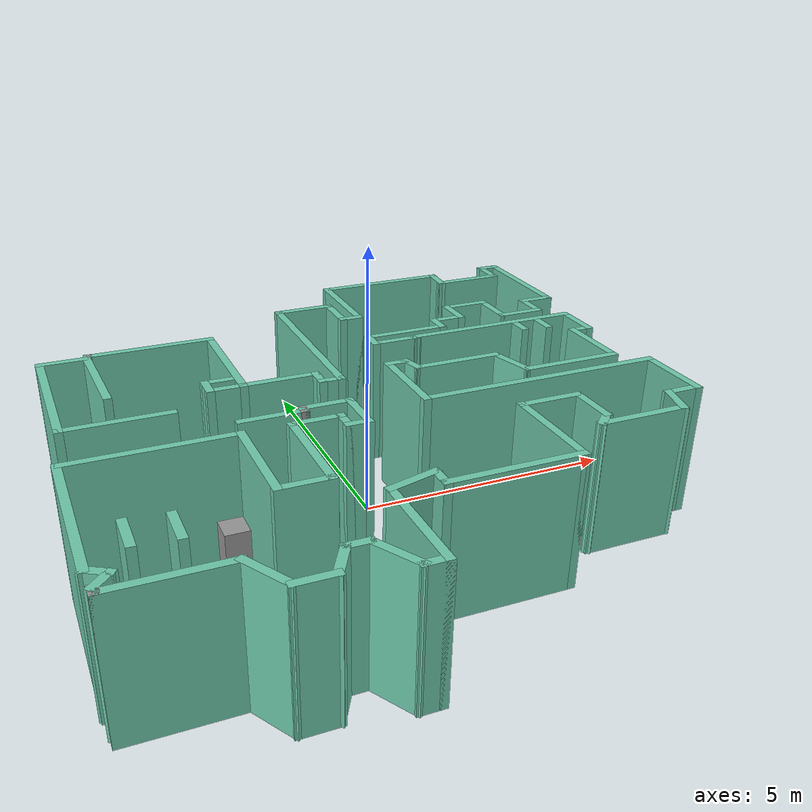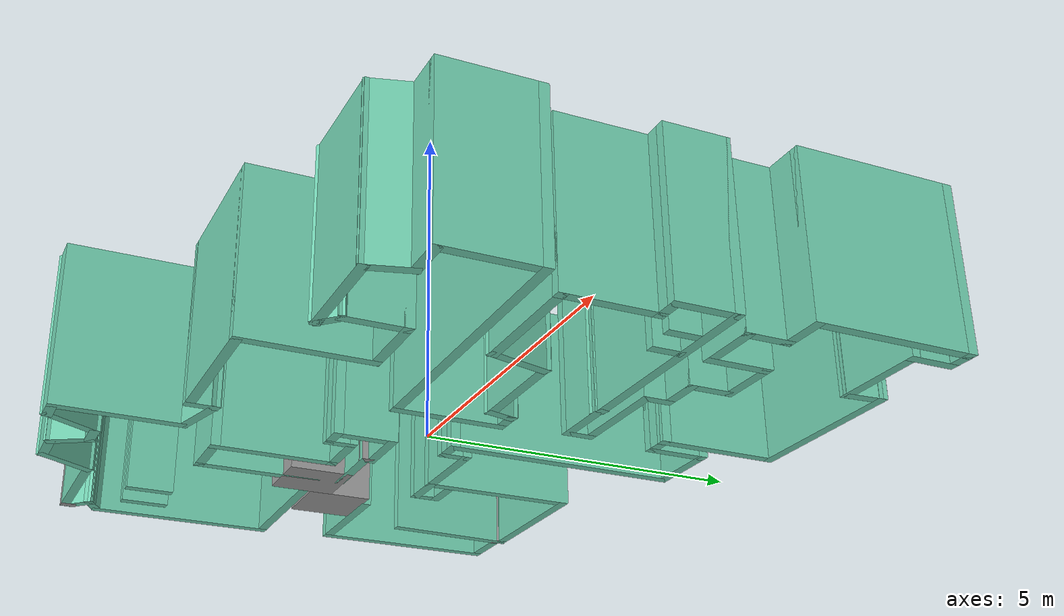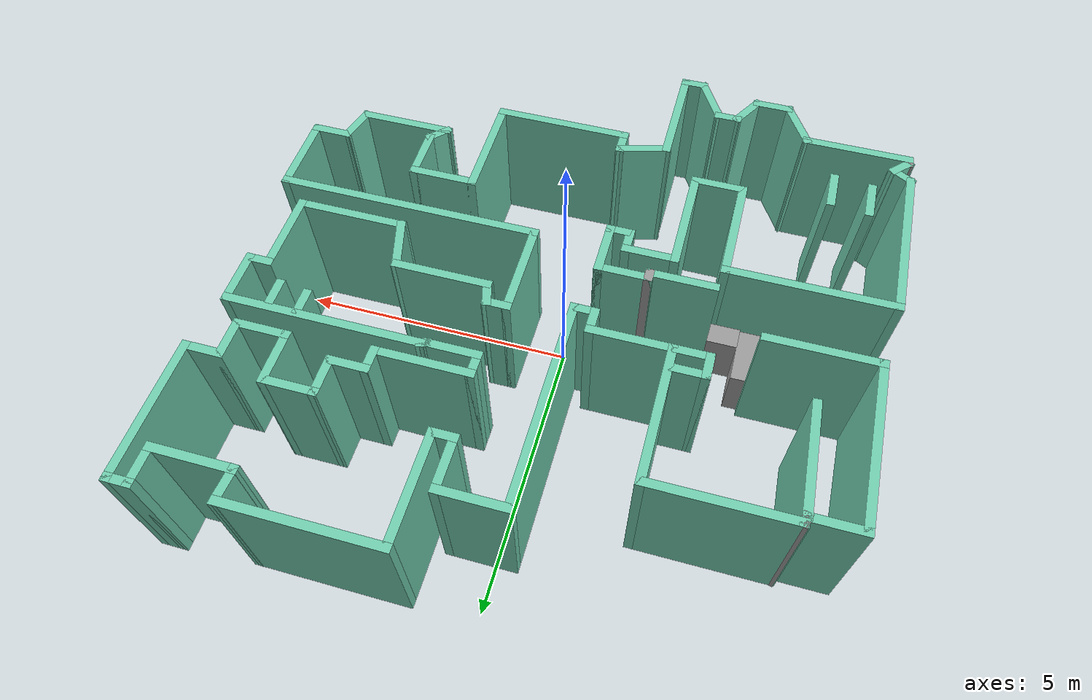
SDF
<?xml version='1.0'?>
<sdf version='1.6'>
  <model name='map_28'>
    <link name='Wall_0'>
      <pose frame=''>2.44979 5.13882 0 0 -0 3.14159</pose>
      <self_collide>0</self_collide>
      <enable_wind>0</enable_wind>
      <kinematic>0</kinematic>
      <visual name='Wall_0_Visual'>
        <pose frame=''>0 0 1.25 0 -0 0</pose>
        <geometry>
          <box>
            <size>2.75 0.15 2.5</size>
          </box>
        </geometry>
        <material>
          <script>
            <uri>file://media/materials/scripts/gazebo.material</uri>
            <name>Gazebo/Grey</name>
          </script>
          <ambient>0.435294 0.796078 0.67451 1</ambient>
          <shader type='pixel'/>
        </material>
        <meta>
          <layer>0</layer>
        </meta>
        <transparency>0</transparency>
        <cast_shadows>1</cast_shadows>
      </visual>
      <collision name='Wall_0_Collision'>
        <laser_retro>0</laser_retro>
        <max_contacts>10</max_contacts>
        <pose frame=''>0 0 1.25 0 -0 0</pose>
        <geometry>
          <box>
            <size>2.75 0.15 2.5</size>
          </box>
        </geometry>
        <surface>
          <friction>
            <ode>
              <mu>1</mu>
              <mu2>1</mu2>
              <fdir1>0 0 0</fdir1>
              <slip1>0</slip1>
              <slip2>0</slip2>
            </ode>
            <torsional>
              <coefficient>1</coefficient>
              <patch_radius>0</patch_radius>
              <surface_radius>0</surface_radius>
              <use_patch_radius>1</use_patch_radius>
              <ode>
                <slip>0</slip>
              </ode>
            </torsional>
          </friction>
          <bounce>
            <restitution_coefficient>0</restitution_coefficient>
            <threshold>1e+06</threshold>
          </bounce>
          <contact>
            <collide_without_contact>0</collide_without_contact>
            <collide_without_contact_bitmask>1</collide_without_contact_bitmask>
            <collide_bitmask>1</collide_bitmask>
            <ode>
              <soft_cfm>0</soft_cfm>
              <soft_erp>0.2</soft_erp>
              <kp>1e+13</kp>
              <kd>1</kd>
              <max_vel>0.01</max_vel>
              <min_depth>0</min_depth>
            </ode>
            <bullet>
              <split_impulse>1</split_impulse>
              <split_impulse_penetration_threshold>-0.01</split_impulse_penetration_threshold>
              <soft_cfm>0</soft_cfm>
              <soft_erp>0.2</soft_erp>
              <kp>1e+13</kp>
              <kd>1</kd>
            </bullet>
          </contact>
        </surface>
      </collision>
    </link>
    <link name='Wall_1'>
      <pose frame=''>1.14979 4.21382 0 0 0 -1.5708</pose>
      <self_collide>0</self_collide>
      <enable_wind>0</enable_wind>
      <kinematic>0</kinematic>
      <visual name='Wall_1_Visual'>
        <pose frame=''>0 0 1.25 0 -0 0</pose>
        <geometry>
          <box>
            <size>2 0.15 2.5</size>
          </box>
        </geometry>
        <material>
          <script>
            <uri>file://media/materials/scripts/gazebo.material</uri>
            <name>Gazebo/Grey</name>
          </script>
          <ambient>0.435294 0.796078 0.67451 1</ambient>
          <shader type='pixel'/>
        </material>
        <meta>
          <layer>0</layer>
        </meta>
        <transparency>0</transparency>
        <cast_shadows>1</cast_shadows>
      </visual>
      <collision name='Wall_1_Collision'>
        <laser_retro>0</laser_retro>
        <max_contacts>10</max_contacts>
        <pose frame=''>0 0 1.25 0 -0 0</pose>
        <geometry>
          <box>
            <size>2 0.15 2.5</size>
          </box>
        </geometry>
        <surface>
          <friction>
            <ode>
              <mu>1</mu>
              <mu2>1</mu2>
              <fdir1>0 0 0</fdir1>
              <slip1>0</slip1>
              <slip2>0</slip2>
            </ode>
            <torsional>
              <coefficient>1</coefficient>
              <patch_radius>0</patch_radius>
              <surface_radius>0</surface_radius>
              <use_patch_radius>1</use_patch_radius>
              <ode>
                <slip>0</slip>
              </ode>
            </torsional>
          </friction>
          <bounce>
            <restitution_coefficient>0</restitution_coefficient>
            <threshold>1e+06</threshold>
          </bounce>
          <contact>
            <collide_without_contact>0</collide_without_contact>
            <collide_without_contact_bitmask>1</collide_without_contact_bitmask>
            <collide_bitmask>1</collide_bitmask>
            <ode>
              <soft_cfm>0</soft_cfm>
              <soft_erp>0.2</soft_erp>
              <kp>1e+13</kp>
              <kd>1</kd>
              <max_vel>0.01</max_vel>
              <min_depth>0</min_depth>
            </ode>
            <bullet>
              <split_impulse>1</split_impulse>
              <split_impulse_penetration_threshold>-0.01</split_impulse_penetration_threshold>
              <soft_cfm>0</soft_cfm>
              <soft_erp>0.2</soft_erp>
              <kp>1e+13</kp>
              <kd>1</kd>
            </bullet>
          </contact>
        </surface>
      </collision>
    </link>
    <link name='Wall_10'>
      <pose frame=''>-3.17521 3.23882 0 0 -0 3.14159</pose>
      <self_collide>0</self_collide>
      <enable_wind>0</enable_wind>
      <kinematic>0</kinematic>
      <visual name='Wall_10_Visual'>
        <pose frame=''>0 0 1.25 0 -0 0</pose>
        <geometry>
          <box>
            <size>2.5 0.15 2.5</size>
          </box>
        </geometry>
        <material>
          <script>
            <uri>file://media/materials/scripts/gazebo.material</uri>
            <name>Gazebo/Grey</name>
          </script>
          <ambient>0.435294 0.796078 0.67451 1</ambient>
          <shader type='pixel'/>
        </material>
        <meta>
          <layer>0</layer>
        </meta>
        <transparency>0</transparency>
        <cast_shadows>1</cast_shadows>
      </visual>
      <collision name='Wall_10_Collision'>
        <laser_retro>0</laser_retro>
        <max_contacts>10</max_contacts>
        <pose frame=''>0 0 1.25 0 -0 0</pose>
        <geometry>
          <box>
            <size>2.5 0.15 2.5</size>
          </box>
        </geometry>
        <surface>
          <friction>
            <ode>
              <mu>1</mu>
              <mu2>1</mu2>
              <fdir1>0 0 0</fdir1>
              <slip1>0</slip1>
              <slip2>0</slip2>
            </ode>
            <torsional>
              <coefficient>1</coefficient>
              <patch_radius>0</patch_radius>
              <surface_radius>0</surface_radius>
              <use_patch_radius>1</use_patch_radius>
              <ode>
                <slip>0</slip>
              </ode>
            </torsional>
          </friction>
          <bounce>
            <restitution_coefficient>0</restitution_coefficient>
            <threshold>1e+06</threshold>
          </bounce>
          <contact>
            <collide_without_contact>0</collide_without_contact>
            <collide_without_contact_bitmask>1</collide_without_contact_bitmask>
            <collide_bitmask>1</collide_bitmask>
            <ode>
              <soft_cfm>0</soft_cfm>
              <soft_erp>0.2</soft_erp>
              <kp>1e+13</kp>
              <kd>1</kd>
              <max_vel>0.01</max_vel>
              <min_depth>0</min_depth>
            </ode>
            <bullet>
              <split_impulse>1</split_impulse>
              <split_impulse_penetration_threshold>-0.01</split_impulse_penetration_threshold>
              <soft_cfm>0</soft_cfm>
              <soft_erp>0.2</soft_erp>
              <kp>1e+13</kp>
              <kd>1</kd>
            </bullet>
          </contact>
        </surface>
      </collision>
    </link>
    <link name='Wall_100'>
      <pose frame=''>4.38795 2.27226 0 0 -0 0</pose>
      <self_collide>0</self_collide>
      <enable_wind>0</enable_wind>
      <kinematic>0</kinematic>
      <visual name='Wall_100_Visual'>
        <pose frame=''>0 0 1.25 0 -0 0</pose>
        <geometry>
          <box>
            <size>1 0.15 2.5</size>
          </box>
        </geometry>
        <material>
          <script>
            <uri>file://media/materials/scripts/gazebo.material</uri>
            <name>Gazebo/Grey</name>
          </script>
          <ambient>0.435294 0.796078 0.67451 1</ambient>
          <shader type='pixel'/>
        </material>
        <meta>
          <layer>0</layer>
        </meta>
        <transparency>0</transparency>
        <cast_shadows>1</cast_shadows>
      </visual>
      <collision name='Wall_100_Collision'>
        <laser_retro>0</laser_retro>
        <max_contacts>10</max_contacts>
        <pose frame=''>0 0 1.25 0 -0 0</pose>
        <geometry>
          <box>
            <size>1 0.15 2.5</size>
          </box>
        </geometry>
        <surface>
          <friction>
            <ode>
              <mu>1</mu>
              <mu2>1</mu2>
              <fdir1>0 0 0</fdir1>
              <slip1>0</slip1>
              <slip2>0</slip2>
            </ode>
            <torsional>
              <coefficient>1</coefficient>
              <patch_radius>0</patch_radius>
              <surface_radius>0</surface_radius>
              <use_patch_radius>1</use_patch_radius>
              <ode>
                <slip>0</slip>
              </ode>
            </torsional>
          </friction>
          <bounce>
            <restitution_coefficient>0</restitution_coefficient>
            <threshold>1e+06</threshold>
          </bounce>
          <contact>
            <collide_without_contact>0</collide_without_contact>
            <collide_without_contact_bitmask>1</collide_without_contact_bitmask>
            <collide_bitmask>1</collide_bitmask>
            <ode>
              <soft_cfm>0</soft_cfm>
              <soft_erp>0.2</soft_erp>
              <kp>1e+13</kp>
              <kd>1</kd>
              <max_vel>0.01</max_vel>
              <min_depth>0</min_depth>
            </ode>
            <bullet>
              <split_impulse>1</split_impulse>
              <split_impulse_penetration_threshold>-0.01</split_impulse_penetration_threshold>
              <soft_cfm>0</soft_cfm>
              <soft_erp>0.2</soft_erp>
              <kp>1e+13</kp>
              <kd>1</kd>
            </bullet>
          </contact>
        </surface>
      </collision>
    </link>
    <link name='Wall_101'>
      <pose frame=''>4.81295 2.57226 0 0 -0 1.5708</pose>
      <self_collide>0</self_collide>
      <enable_wind>0</enable_wind>
      <kinematic>0</kinematic>
      <visual name='Wall_101_Visual'>
        <pose frame=''>0 0 1.25 0 -0 0</pose>
        <geometry>
          <box>
            <size>0.75 0.15 2.5</size>
          </box>
        </geometry>
        <material>
          <script>
            <uri>file://media/materials/scripts/gazebo.material</uri>
            <name>Gazebo/Grey</name>
          </script>
          <ambient>0.435294 0.796078 0.67451 1</ambient>
          <shader type='pixel'/>
        </material>
        <meta>
          <layer>0</layer>
        </meta>
        <transparency>0</transparency>
        <cast_shadows>1</cast_shadows>
      </visual>
      <collision name='Wall_101_Collision'>
        <laser_retro>0</laser_retro>
        <max_contacts>10</max_contacts>
        <pose frame=''>0 0 1.25 0 -0 0</pose>
        <geometry>
          <box>
            <size>0.75 0.15 2.5</size>
          </box>
        </geometry>
        <surface>
          <friction>
            <ode>
              <mu>1</mu>
              <mu2>1</mu2>
              <fdir1>0 0 0</fdir1>
              <slip1>0</slip1>
              <slip2>0</slip2>
            </ode>
            <torsional>
              <coefficient>1</coefficient>
              <patch_radius>0</patch_radius>
              <surface_radius>0</surface_radius>
              <use_patch_radius>1</use_patch_radius>
              <ode>
                <slip>0</slip>
              </ode>
            </torsional>
          </friction>
          <bounce>
            <restitution_coefficient>0</restitution_coefficient>
            <threshold>1e+06</threshold>
          </bounce>
          <contact>
            <collide_without_contact>0</collide_without_contact>
            <collide_without_contact_bitmask>1</collide_without_contact_bitmask>
            <collide_bitmask>1</collide_bitmask>
            <ode>
              <soft_cfm>0</soft_cfm>
              <soft_erp>0.2</soft_erp>
              <kp>1e+13</kp>
              <kd>1</kd>
              <max_vel>0.01</max_vel>
              <min_depth>0</min_depth>
            </ode>
            <bullet>
              <split_impulse>1</split_impulse>
              <split_impulse_penetration_threshold>-0.01</split_impulse_penetration_threshold>
              <soft_cfm>0</soft_cfm>
              <soft_erp>0.2</soft_erp>
              <kp>1e+13</kp>
              <kd>1</kd>
            </bullet>
          </contact>
        </surface>
      </collision>
    </link>
    <link name='Wall_102'>
      <pose frame=''>5.11295 2.87226 0 0 -0 0</pose>
      <self_collide>0</self_collide>
      <enable_wind>0</enable_wind>
      <kinematic>0</kinematic>
      <visual name='Wall_102_Visual'>
        <pose frame=''>0 0 1.25 0 -0 0</pose>
        <geometry>
          <box>
            <size>0.75 0.15 2.5</size>
          </box>
        </geometry>
        <material>
          <script>
            <uri>file://media/materials/scripts/gazebo.material</uri>
            <name>Gazebo/Grey</name>
          </script>
          <ambient>0.435294 0.796078 0.67451 1</ambient>
          <shader type='pixel'/>
        </material>
        <meta>
          <layer>0</layer>
        </meta>
        <transparency>0</transparency>
        <cast_shadows>1</cast_shadows>
      </visual>
      <collision name='Wall_102_Collision'>
        <laser_retro>0</laser_retro>
        <max_contacts>10</max_contacts>
        <pose frame=''>0 0 1.25 0 -0 0</pose>
        <geometry>
          <box>
            <size>0.75 0.15 2.5</size>
          </box>
        </geometry>
        <surface>
          <friction>
            <ode>
              <mu>1</mu>
              <mu2>1</mu2>
              <fdir1>0 0 0</fdir1>
              <slip1>0</slip1>
              <slip2>0</slip2>
            </ode>
            <torsional>
              <coefficient>1</coefficient>
              <patch_radius>0</patch_radius>
              <surface_radius>0</surface_radius>
              <use_patch_radius>1</use_patch_radius>
              <ode>
                <slip>0</slip>
              </ode>
            </torsional>
          </friction>
          <bounce>
            <restitution_coefficient>0</restitution_coefficient>
            <threshold>1e+06</threshold>
          </bounce>
          <contact>
            <collide_without_contact>0</collide_without_contact>
            <collide_without_contact_bitmask>1</collide_without_contact_bitmask>
            <collide_bitmask>1</collide_bitmask>
            <ode>
              <soft_cfm>0</soft_cfm>
              <soft_erp>0.2</soft_erp>
              <kp>1e+13</kp>
              <kd>1</kd>
              <max_vel>0.01</max_vel>
              <min_depth>0</min_depth>
            </ode>
            <bullet>
              <split_impulse>1</split_impulse>
              <split_impulse_penetration_threshold>-0.01</split_impulse_penetration_threshold>
              <soft_cfm>0</soft_cfm>
              <soft_erp>0.2</soft_erp>
              <kp>1e+13</kp>
              <kd>1</kd>
            </bullet>
          </contact>
        </surface>
      </collision>
    </link>
    <link name='Wall_103'>
      <pose frame=''>5.41295 4.04726 0 0 -0 1.5708</pose>
      <self_collide>0</self_collide>
      <enable_wind>0</enable_wind>
      <kinematic>0</kinematic>
      <visual name='Wall_103_Visual'>
        <pose frame=''>0 0 1.25 0 -0 0</pose>
        <geometry>
          <box>
            <size>2.5 0.15 2.5</size>
          </box>
        </geometry>
        <material>
          <script>
            <uri>file://media/materials/scripts/gazebo.material</uri>
            <name>Gazebo/Grey</name>
          </script>
          <ambient>0.435294 0.796078 0.67451 1</ambient>
          <shader type='pixel'/>
        </material>
        <meta>
          <layer>0</layer>
        </meta>
        <transparency>0</transparency>
        <cast_shadows>1</cast_shadows>
      </visual>
      <collision name='Wall_103_Collision'>
        <laser_retro>0</laser_retro>
        <max_contacts>10</max_contacts>
        <pose frame=''>0 0 1.25 0 -0 0</pose>
        <geometry>
          <box>
            <size>2.5 0.15 2.5</size>
          </box>
        </geometry>
        <surface>
          <friction>
            <ode>
              <mu>1</mu>
              <mu2>1</mu2>
              <fdir1>0 0 0</fdir1>
              <slip1>0</slip1>
              <slip2>0</slip2>
            </ode>
            <torsional>
              <coefficient>1</coefficient>
              <patch_radius>0</patch_radius>
              <surface_radius>0</surface_radius>
              <use_patch_radius>1</use_patch_radius>
              <ode>
                <slip>0</slip>
              </ode>
            </torsional>
          </friction>
          <bounce>
            <restitution_coefficient>0</restitution_coefficient>
            <threshold>1e+06</threshold>
          </bounce>
          <contact>
            <collide_without_contact>0</collide_without_contact>
            <collide_without_contact_bitmask>1</collide_without_contact_bitmask>
            <collide_bitmask>1</collide_bitmask>
            <ode>
              <soft_cfm>0</soft_cfm>
              <soft_erp>0.2</soft_erp>
              <kp>1e+13</kp>
              <kd>1</kd>
              <max_vel>0.01</max_vel>
              <min_depth>0</min_depth>
            </ode>
            <bullet>
              <split_impulse>1</split_impulse>
              <split_impulse_penetration_threshold>-0.01</split_impulse_penetration_threshold>
              <soft_cfm>0</soft_cfm>
              <soft_erp>0.2</soft_erp>
              <kp>1e+13</kp>
              <kd>1</kd>
            </bullet>
          </contact>
        </surface>
      </collision>
    </link>
    <link name='Wall_104'>
      <pose frame=''>5.23795 5.22226 0 0 -0 3.14159</pose>
      <self_collide>0</self_collide>
      <enable_wind>0</enable_wind>
      <kinematic>0</kinematic>
      <visual name='Wall_104_Visual'>
        <pose frame=''>0 0 1.25 0 -0 0</pose>
        <geometry>
          <box>
            <size>0.5 0.15 2.5</size>
          </box>
        </geometry>
        <material>
          <script>
            <uri>file://media/materials/scripts/gazebo.material</uri>
            <name>Gazebo/Grey</name>
          </script>
          <ambient>0.435294 0.796078 0.67451 1</ambient>
          <shader type='pixel'/>
        </material>
        <meta>
          <layer>0</layer>
        </meta>
        <transparency>0</transparency>
        <cast_shadows>1</cast_shadows>
      </visual>
      <collision name='Wall_104_Collision'>
        <laser_retro>0</laser_retro>
        <max_contacts>10</max_contacts>
        <pose frame=''>0 0 1.25 0 -0 0</pose>
        <geometry>
          <box>
            <size>0.5 0.15 2.5</size>
          </box>
        </geometry>
        <surface>
          <friction>
            <ode>
              <mu>1</mu>
              <mu2>1</mu2>
              <fdir1>0 0 0</fdir1>
              <slip1>0</slip1>
              <slip2>0</slip2>
            </ode>
            <torsional>
              <coefficient>1</coefficient>
              <patch_radius>0</patch_radius>
              <surface_radius>0</surface_radius>
              <use_patch_radius>1</use_patch_radius>
              <ode>
                <slip>0</slip>
              </ode>
            </torsional>
          </friction>
          <bounce>
            <restitution_coefficient>0</restitution_coefficient>
            <threshold>1e+06</threshold>
          </bounce>
          <contact>
            <collide_without_contact>0</collide_without_contact>
            <collide_without_contact_bitmask>1</collide_without_contact_bitmask>
            <collide_bitmask>1</collide_bitmask>
            <ode>
              <soft_cfm>0</soft_cfm>
              <soft_erp>0.2</soft_erp>
              <kp>1e+13</kp>
              <kd>1</kd>
              <max_vel>0.01</max_vel>
              <min_depth>0</min_depth>
            </ode>
            <bullet>
              <split_impulse>1</split_impulse>
              <split_impulse_penetration_threshold>-0.01</split_impulse_penetration_threshold>
              <soft_cfm>0</soft_cfm>
              <soft_erp>0.2</soft_erp>
              <kp>1e+13</kp>
              <kd>1</kd>
            </bullet>
          </contact>
        </surface>
      </collision>
    </link>
    <link name='Wall_105'>
      <pose frame=''>5.06295 4.92226 0 0 0 -1.5708</pose>
      <self_collide>0</self_collide>
      <enable_wind>0</enable_wind>
      <kinematic>0</kinematic>
      <visual name='Wall_105_Visual'>
        <pose frame=''>0 0 1.25 0 -0 0</pose>
        <geometry>
          <box>
            <size>0.75 0.15 2.5</size>
          </box>
        </geometry>
        <material>
          <script>
            <uri>file://media/materials/scripts/gazebo.material</uri>
            <name>Gazebo/Grey</name>
          </script>
          <ambient>0.435294 0.796078 0.67451 1</ambient>
          <shader type='pixel'/>
        </material>
        <meta>
          <layer>0</layer>
        </meta>
        <transparency>0</transparency>
        <cast_shadows>1</cast_shadows>
      </visual>
      <collision name='Wall_105_Collision'>
        <laser_retro>0</laser_retro>
        <max_contacts>10</max_contacts>
        <pose frame=''>0 0 1.25 0 -0 0</pose>
        <geometry>
          <box>
            <size>0.75 0.15 2.5</size>
          </box>
        </geometry>
        <surface>
          <friction>
            <ode>
              <mu>1</mu>
              <mu2>1</mu2>
              <fdir1>0 0 0</fdir1>
              <slip1>0</slip1>
              <slip2>0</slip2>
            </ode>
            <torsional>
              <coefficient>1</coefficient>
              <patch_radius>0</patch_radius>
              <surface_radius>0</surface_radius>
              <use_patch_radius>1</use_patch_radius>
              <ode>
                <slip>0</slip>
              </ode>
            </torsional>
          </friction>
          <bounce>
            <restitution_coefficient>0</restitution_coefficient>
            <threshold>1e+06</threshold>
          </bounce>
          <contact>
            <collide_without_contact>0</collide_without_contact>
            <collide_without_contact_bitmask>1</collide_without_contact_bitmask>
            <collide_bitmask>1</collide_bitmask>
            <ode>
              <soft_cfm>0</soft_cfm>
              <soft_erp>0.2</soft_erp>
              <kp>1e+13</kp>
              <kd>1</kd>
              <max_vel>0.01</max_vel>
              <min_depth>0</min_depth>
            </ode>
            <bullet>
              <split_impulse>1</split_impulse>
              <split_impulse_penetration_threshold>-0.01</split_impulse_penetration_threshold>
              <soft_cfm>0</soft_cfm>
              <soft_erp>0.2</soft_erp>
              <kp>1e+13</kp>
              <kd>1</kd>
            </bullet>
          </contact>
        </surface>
      </collision>
    </link>
    <link name='Wall_108'>
      <pose frame=''>4.38795 4.62226 0 0 -0 3.14159</pose>
      <self_collide>0</self_collide>
      <enable_wind>0</enable_wind>
      <kinematic>0</kinematic>
      <visual name='Wall_108_Visual'>
        <pose frame=''>0 0 1.25 0 -0 0</pose>
        <geometry>
          <box>
            <size>1.5 0.15 2.5</size>
          </box>
        </geometry>
        <material>
          <script>
            <uri>file://media/materials/scripts/gazebo.material</uri>
            <name>Gazebo/Grey</name>
          </script>
          <ambient>0.435294 0.796078 0.67451 1</ambient>
          <shader type='pixel'/>
        </material>
        <meta>
          <layer>0</layer>
        </meta>
        <transparency>0</transparency>
        <cast_shadows>1</cast_shadows>
      </visual>
      <collision name='Wall_108_Collision'>
        <laser_retro>0</laser_retro>
        <max_contacts>10</max_contacts>
        <pose frame=''>0 0 1.25 0 -0 0</pose>
        <geometry>
          <box>
            <size>1.5 0.15 2.5</size>
          </box>
        </geometry>
        <surface>
          <friction>
            <ode>
              <mu>1</mu>
              <mu2>1</mu2>
              <fdir1>0 0 0</fdir1>
              <slip1>0</slip1>
              <slip2>0</slip2>
            </ode>
            <torsional>
              <coefficient>1</coefficient>
              <patch_radius>0</patch_radius>
              <surface_radius>0</surface_radius>
              <use_patch_radius>1</use_patch_radius>
              <ode>
                <slip>0</slip>
              </ode>
            </torsional>
          </friction>
          <bounce>
            <restitution_coefficient>0</restitution_coefficient>
            <threshold>1e+06</threshold>
          </bounce>
          <contact>
            <collide_without_contact>0</collide_without_contact>
            <collide_without_contact_bitmask>1</collide_without_contact_bitmask>
            <collide_bitmask>1</collide_bitmask>
            <ode>
              <soft_cfm>0</soft_cfm>
              <soft_erp>0.2</soft_erp>
              <kp>1e+13</kp>
              <kd>1</kd>
              <max_vel>0.01</max_vel>
              <min_depth>0</min_depth>
            </ode>
            <bullet>
              <split_impulse>1</split_impulse>
              <split_impulse_penetration_threshold>-0.01</split_impulse_penetration_threshold>
              <soft_cfm>0</soft_cfm>
              <soft_erp>0.2</soft_erp>
              <kp>1e+13</kp>
              <kd>1</kd>
            </bullet>
          </contact>
        </surface>
      </collision>
    </link>
    <link name='Wall_109'>
      <pose frame=''>3.73137 4.88054 0 0 -0 1.4996</pose>
      <self_collide>0</self_collide>
      <enable_wind>0</enable_wind>
      <kinematic>0</kinematic>
      <visual name='Wall_109_Visual'>
        <pose frame=''>0 0 1.25 0 -0 0</pose>
        <geometry>
          <box>
            <size>0.667875 0.15 2.5</size>
          </box>
        </geometry>
        <material>
          <script>
            <uri>file://media/materials/scripts/gazebo.material</uri>
            <name>Gazebo/Grey</name>
          </script>
          <ambient>0.435294 0.796078 0.67451 1</ambient>
          <shader type='pixel'/>
        </material>
        <meta>
          <layer>0</layer>
        </meta>
        <transparency>0</transparency>
        <cast_shadows>1</cast_shadows>
      </visual>
      <collision name='Wall_109_Collision'>
        <laser_retro>0</laser_retro>
        <max_contacts>10</max_contacts>
        <pose frame=''>0 0 1.25 0 -0 0</pose>
        <geometry>
          <box>
            <size>0.667875 0.15 2.5</size>
          </box>
        </geometry>
        <surface>
          <friction>
            <ode>
              <mu>1</mu>
              <mu2>1</mu2>
              <fdir1>0 0 0</fdir1>
              <slip1>0</slip1>
              <slip2>0</slip2>
            </ode>
            <torsional>
              <coefficient>1</coefficient>
              <patch_radius>0</patch_radius>
              <surface_radius>0</surface_radius>
              <use_patch_radius>1</use_patch_radius>
              <ode>
                <slip>0</slip>
              </ode>
            </torsional>
          </friction>
          <bounce>
            <restitution_coefficient>0</restitution_coefficient>
            <threshold>1e+06</threshold>
          </bounce>
          <contact>
            <collide_without_contact>0</collide_without_contact>
            <collide_without_contact_bitmask>1</collide_without_contact_bitmask>
            <collide_bitmask>1</collide_bitmask>
            <ode>
              <soft_cfm>0</soft_cfm>
              <soft_erp>0.2</soft_erp>
              <kp>1e+13</kp>
              <kd>1</kd>
              <max_vel>0.01</max_vel>
              <min_depth>0</min_depth>
            </ode>
            <bullet>
              <split_impulse>1</split_impulse>
              <split_impulse_penetration_threshold>-0.01</split_impulse_penetration_threshold>
              <soft_cfm>0</soft_cfm>
              <soft_erp>0.2</soft_erp>
              <kp>1e+13</kp>
              <kd>1</kd>
            </bullet>
          </contact>
        </surface>
      </collision>
    </link>
    <link name='Wall_11'>
      <pose frame=''>-4.3502 3.23882 0 0 -0 0</pose>
      <self_collide>0</self_collide>
      <enable_wind>0</enable_wind>
      <kinematic>0</kinematic>
      <visual name='Wall_11_Visual'>
        <pose frame=''>0 0 1.25 0 -0 0</pose>
        <geometry>
          <box>
            <size>0.15 0.15 2.5</size>
          </box>
        </geometry>
        <material>
          <script>
            <uri>file://media/materials/scripts/gazebo.material</uri>
            <name>Gazebo/Grey</name>
          </script>
          <ambient>0.435294 0.796078 0.67451 1</ambient>
          <shader type='pixel'/>
        </material>
        <meta>
          <layer>0</layer>
        </meta>
        <transparency>0</transparency>
        <cast_shadows>1</cast_shadows>
      </visual>
      <collision name='Wall_11_Collision'>
        <laser_retro>0</laser_retro>
        <max_contacts>10</max_contacts>
        <pose frame=''>0 0 1.25 0 -0 0</pose>
        <geometry>
          <box>
            <size>0.15 0.15 2.5</size>
          </box>
        </geometry>
        <surface>
          <friction>
            <ode>
              <mu>1</mu>
              <mu2>1</mu2>
              <fdir1>0 0 0</fdir1>
              <slip1>0</slip1>
              <slip2>0</slip2>
            </ode>
            <torsional>
              <coefficient>1</coefficient>
              <patch_radius>0</patch_radius>
              <surface_radius>0</surface_radius>
              <use_patch_radius>1</use_patch_radius>
              <ode>
                <slip>0</slip>
              </ode>
            </torsional>
          </friction>
          <bounce>
            <restitution_coefficient>0</restitution_coefficient>
            <threshold>1e+06</threshold>
          </bounce>
          <contact>
            <collide_without_contact>0</collide_without_contact>
            <collide_without_contact_bitmask>1</collide_without_contact_bitmask>
            <collide_bitmask>1</collide_bitmask>
            <ode>
              <soft_cfm>0</soft_cfm>
              <soft_erp>0.2</soft_erp>
              <kp>1e+13</kp>
              <kd>1</kd>
              <max_vel>0.01</max_vel>
              <min_depth>0</min_depth>
            </ode>
            <bullet>
              <split_impulse>1</split_impulse>
              <split_impulse_penetration_threshold>-0.01</split_impulse_penetration_threshold>
              <soft_cfm>0</soft_cfm>
              <soft_erp>0.2</soft_erp>
              <kp>1e+13</kp>
              <kd>1</kd>
            </bullet>
          </contact>
        </surface>
      </collision>
    </link>
    <link name='Wall_114'>
      <pose frame=''>-4.33787 2.20912 0 0 -0 1.61173</pose>
      <self_collide>0</self_collide>
      <enable_wind>0</enable_wind>
      <kinematic>0</kinematic>
      <visual name='Wall_114_Visual'>
        <pose frame=''>0 0 1.25 0 -0 0</pose>
        <geometry>
          <box>
            <size>2.01778 0.15 2.5</size>
          </box>
        </geometry>
        <material>
          <script>
            <uri>file://media/materials/scripts/gazebo.material</uri>
            <name>Gazebo/Grey</name>
          </script>
          <ambient>0.435294 0.796078 0.67451 1</ambient>
          <shader type='pixel'/>
        </material>
        <meta>
          <layer>0</layer>
        </meta>
        <transparency>0</transparency>
        <cast_shadows>1</cast_shadows>
      </visual>
      <collision name='Wall_114_Collision'>
        <laser_retro>0</laser_retro>
        <max_contacts>10</max_contacts>
        <pose frame=''>0 0 1.25 0 -0 0</pose>
        <geometry>
          <box>
            <size>2.01778 0.15 2.5</size>
          </box>
        </geometry>
        <surface>
          <friction>
            <ode>
              <mu>1</mu>
              <mu2>1</mu2>
              <fdir1>0 0 0</fdir1>
              <slip1>0</slip1>
              <slip2>0</slip2>
            </ode>
            <torsional>
              <coefficient>1</coefficient>
              <patch_radius>0</patch_radius>
              <surface_radius>0</surface_radius>
              <use_patch_radius>1</use_patch_radius>
              <ode>
                <slip>0</slip>
              </ode>
            </torsional>
          </friction>
          <bounce>
            <restitution_coefficient>0</restitution_coefficient>
            <threshold>1e+06</threshold>
          </bounce>
          <contact>
            <collide_without_contact>0</collide_without_contact>
            <collide_without_contact_bitmask>1</collide_without_contact_bitmask>
            <collide_bitmask>1</collide_bitmask>
            <ode>
              <soft_cfm>0</soft_cfm>
              <soft_erp>0.2</soft_erp>
              <kp>1e+13</kp>
              <kd>1</kd>
              <max_vel>0.01</max_vel>
              <min_depth>0</min_depth>
            </ode>
            <bullet>
              <split_impulse>1</split_impulse>
              <split_impulse_penetration_threshold>-0.01</split_impulse_penetration_threshold>
              <soft_cfm>0</soft_cfm>
              <soft_erp>0.2</soft_erp>
              <kp>1e+13</kp>
              <kd>1</kd>
            </bullet>
          </contact>
        </surface>
      </collision>
    </link>
    <link name='Wall_118'>
      <pose frame=''>-2.30021 0.888824 0 0 -0 3.14159</pose>
      <self_collide>0</self_collide>
      <enable_wind>0</enable_wind>
      <kinematic>0</kinematic>
      <visual name='Wall_118_Visual'>
        <pose frame=''>0 0 1.25 0 -0 0</pose>
        <geometry>
          <box>
            <size>0.75 0.15 2.5</size>
          </box>
        </geometry>
        <material>
          <script>
            <uri>file://media/materials/scripts/gazebo.material</uri>
            <name>Gazebo/Grey</name>
          </script>
          <ambient>0.435294 0.796078 0.67451 1</ambient>
          <shader type='pixel'/>
        </material>
        <meta>
          <layer>0</layer>
        </meta>
        <transparency>0</transparency>
        <cast_shadows>1</cast_shadows>
      </visual>
      <collision name='Wall_118_Collision'>
        <laser_retro>0</laser_retro>
        <max_contacts>10</max_contacts>
        <pose frame=''>0 0 1.25 0 -0 0</pose>
        <geometry>
          <box>
            <size>0.75 0.15 2.5</size>
          </box>
        </geometry>
        <surface>
          <friction>
            <ode>
              <mu>1</mu>
              <mu2>1</mu2>
              <fdir1>0 0 0</fdir1>
              <slip1>0</slip1>
              <slip2>0</slip2>
            </ode>
            <torsional>
              <coefficient>1</coefficient>
              <patch_radius>0</patch_radius>
              <surface_radius>0</surface_radius>
              <use_patch_radius>1</use_patch_radius>
              <ode>
                <slip>0</slip>
              </ode>
            </torsional>
          </friction>
          <bounce>
            <restitution_coefficient>0</restitution_coefficient>
            <threshold>1e+06</threshold>
          </bounce>
          <contact>
            <collide_without_contact>0</collide_without_contact>
            <collide_without_contact_bitmask>1</collide_without_contact_bitmask>
            <collide_bitmask>1</collide_bitmask>
            <ode>
              <soft_cfm>0</soft_cfm>
              <soft_erp>0.2</soft_erp>
              <kp>1e+13</kp>
              <kd>1</kd>
              <max_vel>0.01</max_vel>
              <min_depth>0</min_depth>
            </ode>
            <bullet>
              <split_impulse>1</split_impulse>
              <split_impulse_penetration_threshold>-0.01</split_impulse_penetration_threshold>
              <soft_cfm>0</soft_cfm>
              <soft_erp>0.2</soft_erp>
              <kp>1e+13</kp>
              <kd>1</kd>
            </bullet>
          </contact>
        </surface>
      </collision>
    </link>
    <link name='Wall_119'>
      <pose frame=''>-2.6002 1.06382 0 0 -0 1.5708</pose>
      <self_collide>0</self_collide>
      <enable_wind>0</enable_wind>
      <kinematic>0</kinematic>
      <visual name='Wall_119_Visual'>
        <pose frame=''>0 0 1.25 0 -0 0</pose>
        <geometry>
          <box>
            <size>0.5 0.15 2.5</size>
          </box>
        </geometry>
        <material>
          <script>
            <uri>file://media/materials/scripts/gazebo.material</uri>
            <name>Gazebo/Grey</name>
          </script>
          <ambient>0.435294 0.796078 0.67451 1</ambient>
          <shader type='pixel'/>
        </material>
        <meta>
          <layer>0</layer>
        </meta>
        <transparency>0</transparency>
        <cast_shadows>1</cast_shadows>
      </visual>
      <collision name='Wall_119_Collision'>
        <laser_retro>0</laser_retro>
        <max_contacts>10</max_contacts>
        <pose frame=''>0 0 1.25 0 -0 0</pose>
        <geometry>
          <box>
            <size>0.5 0.15 2.5</size>
          </box>
        </geometry>
        <surface>
          <friction>
            <ode>
              <mu>1</mu>
              <mu2>1</mu2>
              <fdir1>0 0 0</fdir1>
              <slip1>0</slip1>
              <slip2>0</slip2>
            </ode>
            <torsional>
              <coefficient>1</coefficient>
              <patch_radius>0</patch_radius>
              <surface_radius>0</surface_radius>
              <use_patch_radius>1</use_patch_radius>
              <ode>
                <slip>0</slip>
              </ode>
            </torsional>
          </friction>
          <bounce>
            <restitution_coefficient>0</restitution_coefficient>
            <threshold>1e+06</threshold>
          </bounce>
          <contact>
            <collide_without_contact>0</collide_without_contact>
            <collide_without_contact_bitmask>1</collide_without_contact_bitmask>
            <collide_bitmask>1</collide_bitmask>
            <ode>
              <soft_cfm>0</soft_cfm>
              <soft_erp>0.2</soft_erp>
              <kp>1e+13</kp>
              <kd>1</kd>
              <max_vel>0.01</max_vel>
              <min_depth>0</min_depth>
            </ode>
            <bullet>
              <split_impulse>1</split_impulse>
              <split_impulse_penetration_threshold>-0.01</split_impulse_penetration_threshold>
              <soft_cfm>0</soft_cfm>
              <soft_erp>0.2</soft_erp>
              <kp>1e+13</kp>
              <kd>1</kd>
            </bullet>
          </contact>
        </surface>
      </collision>
    </link>
    <link name='Wall_120'>
      <pose frame=''>-2.30021 1.23882 0 0 -0 0</pose>
      <self_collide>0</self_collide>
      <enable_wind>0</enable_wind>
      <kinematic>0</kinematic>
      <visual name='Wall_120_Visual'>
        <pose frame=''>0 0 1.25 0 -0 0</pose>
        <geometry>
          <box>
            <size>0.75 0.15 2.5</size>
          </box>
        </geometry>
        <material>
          <script>
            <uri>file://media/materials/scripts/gazebo.material</uri>
            <name>Gazebo/Grey</name>
          </script>
          <ambient>0.435294 0.796078 0.67451 1</ambient>
          <shader type='pixel'/>
        </material>
        <meta>
          <layer>0</layer>
        </meta>
        <transparency>0</transparency>
        <cast_shadows>1</cast_shadows>
      </visual>
      <collision name='Wall_120_Collision'>
        <laser_retro>0</laser_retro>
        <max_contacts>10</max_contacts>
        <pose frame=''>0 0 1.25 0 -0 0</pose>
        <geometry>
          <box>
            <size>0.75 0.15 2.5</size>
          </box>
        </geometry>
        <surface>
          <friction>
            <ode>
              <mu>1</mu>
              <mu2>1</mu2>
              <fdir1>0 0 0</fdir1>
              <slip1>0</slip1>
              <slip2>0</slip2>
            </ode>
            <torsional>
              <coefficient>1</coefficient>
              <patch_radius>0</patch_radius>
              <surface_radius>0</surface_radius>
              <use_patch_radius>1</use_patch_radius>
              <ode>
                <slip>0</slip>
              </ode>
            </torsional>
          </friction>
          <bounce>
            <restitution_coefficient>0</restitution_coefficient>
            <threshold>1e+06</threshold>
          </bounce>
          <contact>
            <collide_without_contact>0</collide_without_contact>
            <collide_without_contact_bitmask>1</collide_without_contact_bitmask>
            <collide_bitmask>1</collide_bitmask>
            <ode>
              <soft_cfm>0</soft_cfm>
              <soft_erp>0.2</soft_erp>
              <kp>1e+13</kp>
              <kd>1</kd>
              <max_vel>0.01</max_vel>
              <min_depth>0</min_depth>
            </ode>
            <bullet>
              <split_impulse>1</split_impulse>
              <split_impulse_penetration_threshold>-0.01</split_impulse_penetration_threshold>
              <soft_cfm>0</soft_cfm>
              <soft_erp>0.2</soft_erp>
              <kp>1e+13</kp>
              <kd>1</kd>
            </bullet>
          </contact>
        </surface>
      </collision>
    </link>
    <link name='Wall_124'>
      <pose frame=''>3.9811 1.60989 0 0 0 -1.5708</pose>
      <self_collide>0</self_collide>
      <enable_wind>0</enable_wind>
      <kinematic>0</kinematic>
      <visual name='Wall_124_Visual'>
        <pose frame=''>0 0 1.25 0 -0 0</pose>
        <geometry>
          <box>
            <size>0.5 0.15 2.5</size>
          </box>
        </geometry>
        <material>
          <script>
            <uri>file://media/materials/scripts/gazebo.material</uri>
            <name>Gazebo/Grey</name>
          </script>
          <ambient>0.435294 0.796078 0.67451 1</ambient>
          <shader type='pixel'/>
        </material>
        <meta>
          <layer>0</layer>
        </meta>
        <transparency>0</transparency>
        <cast_shadows>1</cast_shadows>
      </visual>
      <collision name='Wall_124_Collision'>
        <laser_retro>0</laser_retro>
        <max_contacts>10</max_contacts>
        <pose frame=''>0 0 1.25 0 -0 0</pose>
        <geometry>
          <box>
            <size>0.5 0.15 2.5</size>
          </box>
        </geometry>
        <surface>
          <friction>
            <ode>
              <mu>1</mu>
              <mu2>1</mu2>
              <fdir1>0 0 0</fdir1>
              <slip1>0</slip1>
              <slip2>0</slip2>
            </ode>
            <torsional>
              <coefficient>1</coefficient>
              <patch_radius>0</patch_radius>
              <surface_radius>0</surface_radius>
              <use_patch_radius>1</use_patch_radius>
              <ode>
                <slip>0</slip>
              </ode>
            </torsional>
          </friction>
          <bounce>
            <restitution_coefficient>0</restitution_coefficient>
            <threshold>1e+06</threshold>
          </bounce>
          <contact>
            <collide_without_contact>0</collide_without_contact>
            <collide_without_contact_bitmask>1</collide_without_contact_bitmask>
            <collide_bitmask>1</collide_bitmask>
            <ode>
              <soft_cfm>0</soft_cfm>
              <soft_erp>0.2</soft_erp>
              <kp>1e+13</kp>
              <kd>1</kd>
              <max_vel>0.01</max_vel>
              <min_depth>0</min_depth>
            </ode>
            <bullet>
              <split_impulse>1</split_impulse>
              <split_impulse_penetration_threshold>-0.01</split_impulse_penetration_threshold>
              <soft_cfm>0</soft_cfm>
              <soft_erp>0.2</soft_erp>
              <kp>1e+13</kp>
              <kd>1</kd>
            </bullet>
          </contact>
        </surface>
      </collision>
    </link>
    <link name='Wall_126'>
      <pose frame=''>4.48997 1.54049 0 0 0 -1.5708</pose>
      <self_collide>0</self_collide>
      <enable_wind>0</enable_wind>
      <kinematic>0</kinematic>
      <visual name='Wall_126_Visual'>
        <pose frame=''>0 0 1.25 0 -0 0</pose>
        <geometry>
          <box>
            <size>0.5 0.15 2.5</size>
          </box>
        </geometry>
        <material>
          <script>
            <uri>file://media/materials/scripts/gazebo.material</uri>
            <name>Gazebo/Grey</name>
          </script>
          <ambient>0.435294 0.796078 0.67451 1</ambient>
          <shader type='pixel'/>
        </material>
        <meta>
          <layer>0</layer>
        </meta>
        <transparency>0</transparency>
        <cast_shadows>1</cast_shadows>
      </visual>
      <collision name='Wall_126_Collision'>
        <laser_retro>0</laser_retro>
        <max_contacts>10</max_contacts>
        <pose frame=''>0 0 1.25 0 -0 0</pose>
        <geometry>
          <box>
            <size>0.5 0.15 2.5</size>
          </box>
        </geometry>
        <surface>
          <friction>
            <ode>
              <mu>1</mu>
              <mu2>1</mu2>
              <fdir1>0 0 0</fdir1>
              <slip1>0</slip1>
              <slip2>0</slip2>
            </ode>
            <torsional>
              <coefficient>1</coefficient>
              <patch_radius>0</patch_radius>
              <surface_radius>0</surface_radius>
              <use_patch_radius>1</use_patch_radius>
              <ode>
                <slip>0</slip>
              </ode>
            </torsional>
          </friction>
          <bounce>
            <restitution_coefficient>0</restitution_coefficient>
            <threshold>1e+06</threshold>
          </bounce>
          <contact>
            <collide_without_contact>0</collide_without_contact>
            <collide_without_contact_bitmask>1</collide_without_contact_bitmask>
            <collide_bitmask>1</collide_bitmask>
            <ode>
              <soft_cfm>0</soft_cfm>
              <soft_erp>0.2</soft_erp>
              <kp>1e+13</kp>
              <kd>1</kd>
              <max_vel>0.01</max_vel>
              <min_depth>0</min_depth>
            </ode>
            <bullet>
              <split_impulse>1</split_impulse>
              <split_impulse_penetration_threshold>-0.01</split_impulse_penetration_threshold>
              <soft_cfm>0</soft_cfm>
              <soft_erp>0.2</soft_erp>
              <kp>1e+13</kp>
              <kd>1</kd>
            </bullet>
          </contact>
        </surface>
      </collision>
    </link>
    <link name='Wall_130'>
      <pose frame=''>-4.73914 -3.07184 0 0 0 -1.5708</pose>
      <self_collide>0</self_collide>
      <enable_wind>0</enable_wind>
      <kinematic>0</kinematic>
      <visual name='Wall_130_Visual'>
        <pose frame=''>0 0 1.25 0 -0 0</pose>
        <geometry>
          <box>
            <size>0.75 0.15 2.5</size>
          </box>
        </geometry>
        <material>
          <script>
            <uri>file://media/materials/scripts/gazebo.material</uri>
            <name>Gazebo/Grey</name>
          </script>
          <ambient>0.435294 0.796078 0.67451 1</ambient>
          <shader type='pixel'/>
        </material>
        <meta>
          <layer>0</layer>
        </meta>
        <transparency>0</transparency>
        <cast_shadows>1</cast_shadows>
      </visual>
      <collision name='Wall_130_Collision'>
        <laser_retro>0</laser_retro>
        <max_contacts>10</max_contacts>
        <pose frame=''>0 0 1.25 0 -0 0</pose>
        <geometry>
          <box>
            <size>0.75 0.15 2.5</size>
          </box>
        </geometry>
        <surface>
          <friction>
            <ode>
              <mu>1</mu>
              <mu2>1</mu2>
              <fdir1>0 0 0</fdir1>
              <slip1>0</slip1>
              <slip2>0</slip2>
            </ode>
            <torsional>
              <coefficient>1</coefficient>
              <patch_radius>0</patch_radius>
              <surface_radius>0</surface_radius>
              <use_patch_radius>1</use_patch_radius>
              <ode>
                <slip>0</slip>
              </ode>
            </torsional>
          </friction>
          <bounce>
            <restitution_coefficient>0</restitution_coefficient>
            <threshold>1e+06</threshold>
          </bounce>
          <contact>
            <collide_without_contact>0</collide_without_contact>
            <collide_without_contact_bitmask>1</collide_without_contact_bitmask>
            <collide_bitmask>1</collide_bitmask>
            <ode>
              <soft_cfm>0</soft_cfm>
              <soft_erp>0.2</soft_erp>
              <kp>1e+13</kp>
              <kd>1</kd>
              <max_vel>0.01</max_vel>
              <min_depth>0</min_depth>
            </ode>
            <bullet>
              <split_impulse>1</split_impulse>
              <split_impulse_penetration_threshold>-0.01</split_impulse_penetration_threshold>
              <soft_cfm>0</soft_cfm>
              <soft_erp>0.2</soft_erp>
              <kp>1e+13</kp>
              <kd>1</kd>
            </bullet>
          </contact>
        </surface>
      </collision>
    </link>
    <link name='Wall_132'>
      <pose frame=''>-4.06835 -3.14124 0 0 0 -1.5708</pose>
      <self_collide>0</self_collide>
      <enable_wind>0</enable_wind>
      <kinematic>0</kinematic>
      <visual name='Wall_132_Visual'>
        <pose frame=''>0 0 1.25 0 -0 0</pose>
        <geometry>
          <box>
            <size>0.75 0.15 2.5</size>
          </box>
        </geometry>
        <material>
          <script>
            <uri>file://media/materials/scripts/gazebo.material</uri>
            <name>Gazebo/Grey</name>
          </script>
          <ambient>0.435294 0.796078 0.67451 1</ambient>
          <shader type='pixel'/>
        </material>
        <meta>
          <layer>0</layer>
        </meta>
        <transparency>0</transparency>
        <cast_shadows>1</cast_shadows>
      </visual>
      <collision name='Wall_132_Collision'>
        <laser_retro>0</laser_retro>
        <max_contacts>10</max_contacts>
        <pose frame=''>0 0 1.25 0 -0 0</pose>
        <geometry>
          <box>
            <size>0.75 0.15 2.5</size>
          </box>
        </geometry>
        <surface>
          <friction>
            <ode>
              <mu>1</mu>
              <mu2>1</mu2>
              <fdir1>0 0 0</fdir1>
              <slip1>0</slip1>
              <slip2>0</slip2>
            </ode>
            <torsional>
              <coefficient>1</coefficient>
              <patch_radius>0</patch_radius>
              <surface_radius>0</surface_radius>
              <use_patch_radius>1</use_patch_radius>
              <ode>
                <slip>0</slip>
              </ode>
            </torsional>
          </friction>
          <bounce>
            <restitution_coefficient>0</restitution_coefficient>
            <threshold>1e+06</threshold>
          </bounce>
          <contact>
            <collide_without_contact>0</collide_without_contact>
            <collide_without_contact_bitmask>1</collide_without_contact_bitmask>
            <collide_bitmask>1</collide_bitmask>
            <ode>
              <soft_cfm>0</soft_cfm>
              <soft_erp>0.2</soft_erp>
              <kp>1e+13</kp>
              <kd>1</kd>
              <max_vel>0.01</max_vel>
              <min_depth>0</min_depth>
            </ode>
            <bullet>
              <split_impulse>1</split_impulse>
              <split_impulse_penetration_threshold>-0.01</split_impulse_penetration_threshold>
              <soft_cfm>0</soft_cfm>
              <soft_erp>0.2</soft_erp>
              <kp>1e+13</kp>
              <kd>1</kd>
            </bullet>
          </contact>
        </surface>
      </collision>
    </link>
    <link name='Wall_14'>
      <pose frame=''>-4.36315 3.19053 0 0 0 -1.8326</pose>
      <self_collide>0</self_collide>
      <enable_wind>0</enable_wind>
      <kinematic>0</kinematic>
      <visual name='Wall_14_Visual'>
        <pose frame=''>0 0 1.25 0 -0 0</pose>
        <geometry>
          <box>
            <size>0.25 0.15 2.5</size>
          </box>
        </geometry>
        <material>
          <script>
            <uri>file://media/materials/scripts/gazebo.material</uri>
            <name>Gazebo/Grey</name>
          </script>
          <ambient>1 1 1 1</ambient>
          <shader type='pixel'/>
        </material>
        <meta>
          <layer>0</layer>
        </meta>
        <transparency>0</transparency>
        <cast_shadows>1</cast_shadows>
      </visual>
      <collision name='Wall_14_Collision'>
        <laser_retro>0</laser_retro>
        <max_contacts>10</max_contacts>
        <pose frame=''>0 0 1.25 0 -0 0</pose>
        <geometry>
          <box>
            <size>0.25 0.15 2.5</size>
          </box>
        </geometry>
        <surface>
          <friction>
            <ode>
              <mu>1</mu>
              <mu2>1</mu2>
              <fdir1>0 0 0</fdir1>
              <slip1>0</slip1>
              <slip2>0</slip2>
            </ode>
            <torsional>
              <coefficient>1</coefficient>
              <patch_radius>0</patch_radius>
              <surface_radius>0</surface_radius>
              <use_patch_radius>1</use_patch_radius>
              <ode>
                <slip>0</slip>
              </ode>
            </torsional>
          </friction>
          <bounce>
            <restitution_coefficient>0</restitution_coefficient>
            <threshold>1e+06</threshold>
          </bounce>
          <contact>
            <collide_without_contact>0</collide_without_contact>
            <collide_without_contact_bitmask>1</collide_without_contact_bitmask>
            <collide_bitmask>1</collide_bitmask>
            <ode>
              <soft_cfm>0</soft_cfm>
              <soft_erp>0.2</soft_erp>
              <kp>1e+13</kp>
              <kd>1</kd>
              <max_vel>0.01</max_vel>
              <min_depth>0</min_depth>
            </ode>
            <bullet>
              <split_impulse>1</split_impulse>
              <split_impulse_penetration_threshold>-0.01</split_impulse_penetration_threshold>
              <soft_cfm>0</soft_cfm>
              <soft_erp>0.2</soft_erp>
              <kp>1e+13</kp>
              <kd>1</kd>
            </bullet>
          </contact>
        </surface>
      </collision>
    </link>
    <link name='Wall_15'>
      <pose frame=''>-4.80109 3.14223 0 0 -0 3.14159</pose>
      <self_collide>0</self_collide>
      <enable_wind>0</enable_wind>
      <kinematic>0</kinematic>
      <visual name='Wall_15_Visual'>
        <pose frame=''>0 0 1.25 0 -0 0</pose>
        <geometry>
          <box>
            <size>1 0.15 2.5</size>
          </box>
        </geometry>
        <material>
          <script>
            <uri>file://media/materials/scripts/gazebo.material</uri>
            <name>Gazebo/Grey</name>
          </script>
          <ambient>0.435294 0.796078 0.67451 1</ambient>
          <shader type='pixel'/>
        </material>
        <meta>
          <layer>0</layer>
        </meta>
        <transparency>0</transparency>
        <cast_shadows>1</cast_shadows>
      </visual>
      <collision name='Wall_15_Collision'>
        <laser_retro>0</laser_retro>
        <max_contacts>10</max_contacts>
        <pose frame=''>0 0 1.25 0 -0 0</pose>
        <geometry>
          <box>
            <size>1 0.15 2.5</size>
          </box>
        </geometry>
        <surface>
          <friction>
            <ode>
              <mu>1</mu>
              <mu2>1</mu2>
              <fdir1>0 0 0</fdir1>
              <slip1>0</slip1>
              <slip2>0</slip2>
            </ode>
            <torsional>
              <coefficient>1</coefficient>
              <patch_radius>0</patch_radius>
              <surface_radius>0</surface_radius>
              <use_patch_radius>1</use_patch_radius>
              <ode>
                <slip>0</slip>
              </ode>
            </torsional>
          </friction>
          <bounce>
            <restitution_coefficient>0</restitution_coefficient>
            <threshold>1e+06</threshold>
          </bounce>
          <contact>
            <collide_without_contact>0</collide_without_contact>
            <collide_without_contact_bitmask>1</collide_without_contact_bitmask>
            <collide_bitmask>1</collide_bitmask>
            <ode>
              <soft_cfm>0</soft_cfm>
              <soft_erp>0.2</soft_erp>
              <kp>1e+13</kp>
              <kd>1</kd>
              <max_vel>0.01</max_vel>
              <min_depth>0</min_depth>
            </ode>
            <bullet>
              <split_impulse>1</split_impulse>
              <split_impulse_penetration_threshold>-0.01</split_impulse_penetration_threshold>
              <soft_cfm>0</soft_cfm>
              <soft_erp>0.2</soft_erp>
              <kp>1e+13</kp>
              <kd>1</kd>
            </bullet>
          </contact>
        </surface>
      </collision>
    </link>
    <link name='Wall_16'>
      <pose frame=''>-5.22609 1.71723 0 0 0 -1.5708</pose>
      <self_collide>0</self_collide>
      <enable_wind>0</enable_wind>
      <kinematic>0</kinematic>
      <visual name='Wall_16_Visual'>
        <pose frame=''>0 0 1.25 0 -0 0</pose>
        <geometry>
          <box>
            <size>3 0.15 2.5</size>
          </box>
        </geometry>
        <material>
          <script>
            <uri>file://media/materials/scripts/gazebo.material</uri>
            <name>Gazebo/Grey</name>
          </script>
          <ambient>0.435294 0.796078 0.67451 1</ambient>
          <shader type='pixel'/>
        </material>
        <meta>
          <layer>0</layer>
        </meta>
        <transparency>0</transparency>
        <cast_shadows>1</cast_shadows>
      </visual>
      <collision name='Wall_16_Collision'>
        <laser_retro>0</laser_retro>
        <max_contacts>10</max_contacts>
        <pose frame=''>0 0 1.25 0 -0 0</pose>
        <geometry>
          <box>
            <size>3 0.15 2.5</size>
          </box>
        </geometry>
        <surface>
          <friction>
            <ode>
              <mu>1</mu>
              <mu2>1</mu2>
              <fdir1>0 0 0</fdir1>
              <slip1>0</slip1>
              <slip2>0</slip2>
            </ode>
            <torsional>
              <coefficient>1</coefficient>
              <patch_radius>0</patch_radius>
              <surface_radius>0</surface_radius>
              <use_patch_radius>1</use_patch_radius>
              <ode>
                <slip>0</slip>
              </ode>
            </torsional>
          </friction>
          <bounce>
            <restitution_coefficient>0</restitution_coefficient>
            <threshold>1e+06</threshold>
          </bounce>
          <contact>
            <collide_without_contact>0</collide_without_contact>
            <collide_without_contact_bitmask>1</collide_without_contact_bitmask>
            <collide_bitmask>1</collide_bitmask>
            <ode>
              <soft_cfm>0</soft_cfm>
              <soft_erp>0.2</soft_erp>
              <kp>1e+13</kp>
              <kd>1</kd>
              <max_vel>0.01</max_vel>
              <min_depth>0</min_depth>
            </ode>
            <bullet>
              <split_impulse>1</split_impulse>
              <split_impulse_penetration_threshold>-0.01</split_impulse_penetration_threshold>
              <soft_cfm>0</soft_cfm>
              <soft_erp>0.2</soft_erp>
              <kp>1e+13</kp>
              <kd>1</kd>
            </bullet>
          </contact>
        </surface>
      </collision>
    </link>
    <link name='Wall_17'>
      <pose frame=''>-4.30109 0.292231 0 0 -0 0</pose>
      <self_collide>0</self_collide>
      <enable_wind>0</enable_wind>
      <kinematic>0</kinematic>
      <visual name='Wall_17_Visual'>
        <pose frame=''>0 0 1.25 0 -0 0</pose>
        <geometry>
          <box>
            <size>2 0.15 2.5</size>
          </box>
        </geometry>
        <material>
          <script>
            <uri>file://media/materials/scripts/gazebo.material</uri>
            <name>Gazebo/Grey</name>
          </script>
          <ambient>0.435294 0.796078 0.67451 1</ambient>
          <shader type='pixel'/>
        </material>
        <meta>
          <layer>0</layer>
        </meta>
        <transparency>0</transparency>
        <cast_shadows>1</cast_shadows>
      </visual>
      <collision name='Wall_17_Collision'>
        <laser_retro>0</laser_retro>
        <max_contacts>10</max_contacts>
        <pose frame=''>0 0 1.25 0 -0 0</pose>
        <geometry>
          <box>
            <size>2 0.15 2.5</size>
          </box>
        </geometry>
        <surface>
          <friction>
            <ode>
              <mu>1</mu>
              <mu2>1</mu2>
              <fdir1>0 0 0</fdir1>
              <slip1>0</slip1>
              <slip2>0</slip2>
            </ode>
            <torsional>
              <coefficient>1</coefficient>
              <patch_radius>0</patch_radius>
              <surface_radius>0</surface_radius>
              <use_patch_radius>1</use_patch_radius>
              <ode>
                <slip>0</slip>
              </ode>
            </torsional>
          </friction>
          <bounce>
            <restitution_coefficient>0</restitution_coefficient>
            <threshold>1e+06</threshold>
          </bounce>
          <contact>
            <collide_without_contact>0</collide_without_contact>
            <collide_without_contact_bitmask>1</collide_without_contact_bitmask>
            <collide_bitmask>1</collide_bitmask>
            <ode>
              <soft_cfm>0</soft_cfm>
              <soft_erp>0.2</soft_erp>
              <kp>1e+13</kp>
              <kd>1</kd>
              <max_vel>0.01</max_vel>
              <min_depth>0</min_depth>
            </ode>
            <bullet>
              <split_impulse>1</split_impulse>
              <split_impulse_penetration_threshold>-0.01</split_impulse_penetration_threshold>
              <soft_cfm>0</soft_cfm>
              <soft_erp>0.2</soft_erp>
              <kp>1e+13</kp>
              <kd>1</kd>
            </bullet>
          </contact>
        </surface>
      </collision>
    </link>
    <link name='Wall_2'>
      <pose frame=''>0.974795 3.28882 0 0 -0 3.14159</pose>
      <self_collide>0</self_collide>
      <enable_wind>0</enable_wind>
      <kinematic>0</kinematic>
      <visual name='Wall_2_Visual'>
        <pose frame=''>0 0 1.25 0 -0 0</pose>
        <geometry>
          <box>
            <size>0.5 0.15 2.5</size>
          </box>
        </geometry>
        <material>
          <script>
            <uri>file://media/materials/scripts/gazebo.material</uri>
            <name>Gazebo/Grey</name>
          </script>
          <ambient>0.435294 0.796078 0.67451 1</ambient>
          <shader type='pixel'/>
        </material>
        <meta>
          <layer>0</layer>
        </meta>
        <transparency>0</transparency>
        <cast_shadows>1</cast_shadows>
      </visual>
      <collision name='Wall_2_Collision'>
        <laser_retro>0</laser_retro>
        <max_contacts>10</max_contacts>
        <pose frame=''>0 0 1.25 0 -0 0</pose>
        <geometry>
          <box>
            <size>0.5 0.15 2.5</size>
          </box>
        </geometry>
        <surface>
          <friction>
            <ode>
              <mu>1</mu>
              <mu2>1</mu2>
              <fdir1>0 0 0</fdir1>
              <slip1>0</slip1>
              <slip2>0</slip2>
            </ode>
            <torsional>
              <coefficient>1</coefficient>
              <patch_radius>0</patch_radius>
              <surface_radius>0</surface_radius>
              <use_patch_radius>1</use_patch_radius>
              <ode>
                <slip>0</slip>
              </ode>
            </torsional>
          </friction>
          <bounce>
            <restitution_coefficient>0</restitution_coefficient>
            <threshold>1e+06</threshold>
          </bounce>
          <contact>
            <collide_without_contact>0</collide_without_contact>
            <collide_without_contact_bitmask>1</collide_without_contact_bitmask>
            <collide_bitmask>1</collide_bitmask>
            <ode>
              <soft_cfm>0</soft_cfm>
              <soft_erp>0.2</soft_erp>
              <kp>1e+13</kp>
              <kd>1</kd>
              <max_vel>0.01</max_vel>
              <min_depth>0</min_depth>
            </ode>
            <bullet>
              <split_impulse>1</split_impulse>
              <split_impulse_penetration_threshold>-0.01</split_impulse_penetration_threshold>
              <soft_cfm>0</soft_cfm>
              <soft_erp>0.2</soft_erp>
              <kp>1e+13</kp>
              <kd>1</kd>
            </bullet>
          </contact>
        </surface>
      </collision>
    </link>
    <link name='Wall_23'>
      <pose frame=''>-1.8855 -0.469695 0 0 -0 0</pose>
      <self_collide>0</self_collide>
      <enable_wind>0</enable_wind>
      <kinematic>0</kinematic>
      <visual name='Wall_23_Visual'>
        <pose frame=''>0 0 1.25 0 -0 0</pose>
        <geometry>
          <box>
            <size>1.25 0.15 2.5</size>
          </box>
        </geometry>
        <material>
          <script>
            <uri>file://media/materials/scripts/gazebo.material</uri>
            <name>Gazebo/Grey</name>
          </script>
          <ambient>0.435294 0.796078 0.67451 1</ambient>
          <shader type='pixel'/>
        </material>
        <meta>
          <layer>0</layer>
        </meta>
        <transparency>0</transparency>
        <cast_shadows>1</cast_shadows>
      </visual>
      <collision name='Wall_23_Collision'>
        <laser_retro>0</laser_retro>
        <max_contacts>10</max_contacts>
        <pose frame=''>0 0 1.25 0 -0 0</pose>
        <geometry>
          <box>
            <size>1.25 0.15 2.5</size>
          </box>
        </geometry>
        <surface>
          <friction>
            <ode>
              <mu>1</mu>
              <mu2>1</mu2>
              <fdir1>0 0 0</fdir1>
              <slip1>0</slip1>
              <slip2>0</slip2>
            </ode>
            <torsional>
              <coefficient>1</coefficient>
              <patch_radius>0</patch_radius>
              <surface_radius>0</surface_radius>
              <use_patch_radius>1</use_patch_radius>
              <ode>
                <slip>0</slip>
              </ode>
            </torsional>
          </friction>
          <bounce>
            <restitution_coefficient>0</restitution_coefficient>
            <threshold>1e+06</threshold>
          </bounce>
          <contact>
            <collide_without_contact>0</collide_without_contact>
            <collide_without_contact_bitmask>1</collide_without_contact_bitmask>
            <collide_bitmask>1</collide_bitmask>
            <ode>
              <soft_cfm>0</soft_cfm>
              <soft_erp>0.2</soft_erp>
              <kp>1e+13</kp>
              <kd>1</kd>
              <max_vel>0.01</max_vel>
              <min_depth>0</min_depth>
            </ode>
            <bullet>
              <split_impulse>1</split_impulse>
              <split_impulse_penetration_threshold>-0.01</split_impulse_penetration_threshold>
              <soft_cfm>0</soft_cfm>
              <soft_erp>0.2</soft_erp>
              <kp>1e+13</kp>
              <kd>1</kd>
            </bullet>
          </contact>
        </surface>
      </collision>
    </link>
    <link name='Wall_24'>
      <pose frame=''>-1.3355 -0.419695 0 0 -0 1.5708</pose>
      <self_collide>0</self_collide>
      <enable_wind>0</enable_wind>
      <kinematic>0</kinematic>
      <visual name='Wall_24_Visual'>
        <pose frame=''>0 0 1.25 0 -0 0</pose>
        <geometry>
          <box>
            <size>0.25 0.15 2.5</size>
          </box>
        </geometry>
        <material>
          <script>
            <uri>file://media/materials/scripts/gazebo.material</uri>
            <name>Gazebo/Grey</name>
          </script>
          <ambient>1 1 1 1</ambient>
          <shader type='pixel'/>
        </material>
        <meta>
          <layer>0</layer>
        </meta>
        <transparency>0</transparency>
        <cast_shadows>1</cast_shadows>
      </visual>
      <collision name='Wall_24_Collision'>
        <laser_retro>0</laser_retro>
        <max_contacts>10</max_contacts>
        <pose frame=''>0 0 1.25 0 -0 0</pose>
        <geometry>
          <box>
            <size>0.25 0.15 2.5</size>
          </box>
        </geometry>
        <surface>
          <friction>
            <ode>
              <mu>1</mu>
              <mu2>1</mu2>
              <fdir1>0 0 0</fdir1>
              <slip1>0</slip1>
              <slip2>0</slip2>
            </ode>
            <torsional>
              <coefficient>1</coefficient>
              <patch_radius>0</patch_radius>
              <surface_radius>0</surface_radius>
              <use_patch_radius>1</use_patch_radius>
              <ode>
                <slip>0</slip>
              </ode>
            </torsional>
          </friction>
          <bounce>
            <restitution_coefficient>0</restitution_coefficient>
            <threshold>1e+06</threshold>
          </bounce>
          <contact>
            <collide_without_contact>0</collide_without_contact>
            <collide_without_contact_bitmask>1</collide_without_contact_bitmask>
            <collide_bitmask>1</collide_bitmask>
            <ode>
              <soft_cfm>0</soft_cfm>
              <soft_erp>0.2</soft_erp>
              <kp>1e+13</kp>
              <kd>1</kd>
              <max_vel>0.01</max_vel>
              <min_depth>0</min_depth>
            </ode>
            <bullet>
              <split_impulse>1</split_impulse>
              <split_impulse_penetration_threshold>-0.01</split_impulse_penetration_threshold>
              <soft_cfm>0</soft_cfm>
              <soft_erp>0.2</soft_erp>
              <kp>1e+13</kp>
              <kd>1</kd>
            </bullet>
          </contact>
        </surface>
      </collision>
    </link>
    <link name='Wall_25'>
      <pose frame=''>-0.910501 -0.369695 0 0 -0 0</pose>
      <self_collide>0</self_collide>
      <enable_wind>0</enable_wind>
      <kinematic>0</kinematic>
      <visual name='Wall_25_Visual'>
        <pose frame=''>0 0 1.25 0 -0 0</pose>
        <geometry>
          <box>
            <size>1 0.15 2.5</size>
          </box>
        </geometry>
        <material>
          <script>
            <uri>file://media/materials/scripts/gazebo.material</uri>
            <name>Gazebo/Grey</name>
          </script>
          <ambient>0.435294 0.796078 0.67451 1</ambient>
          <shader type='pixel'/>
        </material>
        <meta>
          <layer>0</layer>
        </meta>
        <transparency>0</transparency>
        <cast_shadows>1</cast_shadows>
      </visual>
      <collision name='Wall_25_Collision'>
        <laser_retro>0</laser_retro>
        <max_contacts>10</max_contacts>
        <pose frame=''>0 0 1.25 0 -0 0</pose>
        <geometry>
          <box>
            <size>1 0.15 2.5</size>
          </box>
        </geometry>
        <surface>
          <friction>
            <ode>
              <mu>1</mu>
              <mu2>1</mu2>
              <fdir1>0 0 0</fdir1>
              <slip1>0</slip1>
              <slip2>0</slip2>
            </ode>
            <torsional>
              <coefficient>1</coefficient>
              <patch_radius>0</patch_radius>
              <surface_radius>0</surface_radius>
              <use_patch_radius>1</use_patch_radius>
              <ode>
                <slip>0</slip>
              </ode>
            </torsional>
          </friction>
          <bounce>
            <restitution_coefficient>0</restitution_coefficient>
            <threshold>1e+06</threshold>
          </bounce>
          <contact>
            <collide_without_contact>0</collide_without_contact>
            <collide_without_contact_bitmask>1</collide_without_contact_bitmask>
            <collide_bitmask>1</collide_bitmask>
            <ode>
              <soft_cfm>0</soft_cfm>
              <soft_erp>0.2</soft_erp>
              <kp>1e+13</kp>
              <kd>1</kd>
              <max_vel>0.01</max_vel>
              <min_depth>0</min_depth>
            </ode>
            <bullet>
              <split_impulse>1</split_impulse>
              <split_impulse_penetration_threshold>-0.01</split_impulse_penetration_threshold>
              <soft_cfm>0</soft_cfm>
              <soft_erp>0.2</soft_erp>
              <kp>1e+13</kp>
              <kd>1</kd>
            </bullet>
          </contact>
        </surface>
      </collision>
    </link>
    <link name='Wall_26'>
      <pose frame=''>-0.485501 -0.794695 0 0 0 -1.5708</pose>
      <self_collide>0</self_collide>
      <enable_wind>0</enable_wind>
      <kinematic>0</kinematic>
      <visual name='Wall_26_Visual'>
        <pose frame=''>0 0 1.25 0 -0 0</pose>
        <geometry>
          <box>
            <size>1 0.15 2.5</size>
          </box>
        </geometry>
        <material>
          <script>
            <uri>file://media/materials/scripts/gazebo.material</uri>
            <name>Gazebo/Grey</name>
          </script>
          <ambient>0.435294 0.796078 0.67451 1</ambient>
          <shader type='pixel'/>
        </material>
        <meta>
          <layer>0</layer>
        </meta>
        <transparency>0</transparency>
        <cast_shadows>1</cast_shadows>
      </visual>
      <collision name='Wall_26_Collision'>
        <laser_retro>0</laser_retro>
        <max_contacts>10</max_contacts>
        <pose frame=''>0 0 1.25 0 -0 0</pose>
        <geometry>
          <box>
            <size>1 0.15 2.5</size>
          </box>
        </geometry>
        <surface>
          <friction>
            <ode>
              <mu>1</mu>
              <mu2>1</mu2>
              <fdir1>0 0 0</fdir1>
              <slip1>0</slip1>
              <slip2>0</slip2>
            </ode>
            <torsional>
              <coefficient>1</coefficient>
              <patch_radius>0</patch_radius>
              <surface_radius>0</surface_radius>
              <use_patch_radius>1</use_patch_radius>
              <ode>
                <slip>0</slip>
              </ode>
            </torsional>
          </friction>
          <bounce>
            <restitution_coefficient>0</restitution_coefficient>
            <threshold>1e+06</threshold>
          </bounce>
          <contact>
            <collide_without_contact>0</collide_without_contact>
            <collide_without_contact_bitmask>1</collide_without_contact_bitmask>
            <collide_bitmask>1</collide_bitmask>
            <ode>
              <soft_cfm>0</soft_cfm>
              <soft_erp>0.2</soft_erp>
              <kp>1e+13</kp>
              <kd>1</kd>
              <max_vel>0.01</max_vel>
              <min_depth>0</min_depth>
            </ode>
            <bullet>
              <split_impulse>1</split_impulse>
              <split_impulse_penetration_threshold>-0.01</split_impulse_penetration_threshold>
              <soft_cfm>0</soft_cfm>
              <soft_erp>0.2</soft_erp>
              <kp>1e+13</kp>
              <kd>1</kd>
            </bullet>
          </contact>
        </surface>
      </collision>
    </link>
    <link name='Wall_27'>
      <pose frame=''>-0.660501 -1.21969 0 0 -0 3.14159</pose>
      <self_collide>0</self_collide>
      <enable_wind>0</enable_wind>
      <kinematic>0</kinematic>
      <visual name='Wall_27_Visual'>
        <pose frame=''>0 0 1.25 0 -0 0</pose>
        <geometry>
          <box>
            <size>0.5 0.15 2.5</size>
          </box>
        </geometry>
        <material>
          <script>
            <uri>file://media/materials/scripts/gazebo.material</uri>
            <name>Gazebo/Grey</name>
          </script>
          <ambient>0.435294 0.796078 0.67451 1</ambient>
          <shader type='pixel'/>
        </material>
        <meta>
          <layer>0</layer>
        </meta>
        <transparency>0</transparency>
        <cast_shadows>1</cast_shadows>
      </visual>
      <collision name='Wall_27_Collision'>
        <laser_retro>0</laser_retro>
        <max_contacts>10</max_contacts>
        <pose frame=''>0 0 1.25 0 -0 0</pose>
        <geometry>
          <box>
            <size>0.5 0.15 2.5</size>
          </box>
        </geometry>
        <surface>
          <friction>
            <ode>
              <mu>1</mu>
              <mu2>1</mu2>
              <fdir1>0 0 0</fdir1>
              <slip1>0</slip1>
              <slip2>0</slip2>
            </ode>
            <torsional>
              <coefficient>1</coefficient>
              <patch_radius>0</patch_radius>
              <surface_radius>0</surface_radius>
              <use_patch_radius>1</use_patch_radius>
              <ode>
                <slip>0</slip>
              </ode>
            </torsional>
          </friction>
          <bounce>
            <restitution_coefficient>0</restitution_coefficient>
            <threshold>1e+06</threshold>
          </bounce>
          <contact>
            <collide_without_contact>0</collide_without_contact>
            <collide_without_contact_bitmask>1</collide_without_contact_bitmask>
            <collide_bitmask>1</collide_bitmask>
            <ode>
              <soft_cfm>0</soft_cfm>
              <soft_erp>0.2</soft_erp>
              <kp>1e+13</kp>
              <kd>1</kd>
              <max_vel>0.01</max_vel>
              <min_depth>0</min_depth>
            </ode>
            <bullet>
              <split_impulse>1</split_impulse>
              <split_impulse_penetration_threshold>-0.01</split_impulse_penetration_threshold>
              <soft_cfm>0</soft_cfm>
              <soft_erp>0.2</soft_erp>
              <kp>1e+13</kp>
              <kd>1</kd>
            </bullet>
          </contact>
        </surface>
      </collision>
    </link>
    <link name='Wall_3'>
      <pose frame=''>0.799795 3.71382 0 0 -0 1.5708</pose>
      <self_collide>0</self_collide>
      <enable_wind>0</enable_wind>
      <kinematic>0</kinematic>
      <visual name='Wall_3_Visual'>
        <pose frame=''>0 0 1.25 0 -0 0</pose>
        <geometry>
          <box>
            <size>1 0.15 2.5</size>
          </box>
        </geometry>
        <material>
          <script>
            <uri>file://media/materials/scripts/gazebo.material</uri>
            <name>Gazebo/Grey</name>
          </script>
          <ambient>0.435294 0.796078 0.67451 1</ambient>
          <shader type='pixel'/>
        </material>
        <meta>
          <layer>0</layer>
        </meta>
        <transparency>0</transparency>
        <cast_shadows>1</cast_shadows>
      </visual>
      <collision name='Wall_3_Collision'>
        <laser_retro>0</laser_retro>
        <max_contacts>10</max_contacts>
        <pose frame=''>0 0 1.25 0 -0 0</pose>
        <geometry>
          <box>
            <size>1 0.15 2.5</size>
          </box>
        </geometry>
        <surface>
          <friction>
            <ode>
              <mu>1</mu>
              <mu2>1</mu2>
              <fdir1>0 0 0</fdir1>
              <slip1>0</slip1>
              <slip2>0</slip2>
            </ode>
            <torsional>
              <coefficient>1</coefficient>
              <patch_radius>0</patch_radius>
              <surface_radius>0</surface_radius>
              <use_patch_radius>1</use_patch_radius>
              <ode>
                <slip>0</slip>
              </ode>
            </torsional>
          </friction>
          <bounce>
            <restitution_coefficient>0</restitution_coefficient>
            <threshold>1e+06</threshold>
          </bounce>
          <contact>
            <collide_without_contact>0</collide_without_contact>
            <collide_without_contact_bitmask>1</collide_without_contact_bitmask>
            <collide_bitmask>1</collide_bitmask>
            <ode>
              <soft_cfm>0</soft_cfm>
              <soft_erp>0.2</soft_erp>
              <kp>1e+13</kp>
              <kd>1</kd>
              <max_vel>0.01</max_vel>
              <min_depth>0</min_depth>
            </ode>
            <bullet>
              <split_impulse>1</split_impulse>
              <split_impulse_penetration_threshold>-0.01</split_impulse_penetration_threshold>
              <soft_cfm>0</soft_cfm>
              <soft_erp>0.2</soft_erp>
              <kp>1e+13</kp>
              <kd>1</kd>
            </bullet>
          </contact>
        </surface>
      </collision>
    </link>
    <link name='Wall_34'>
      <pose frame=''>-0.835501 -1.04469 0 0 -0 1.5708</pose>
      <self_collide>0</self_collide>
      <enable_wind>0</enable_wind>
      <kinematic>0</kinematic>
      <visual name='Wall_34_Visual'>
        <pose frame=''>0 0 1.25 0 -0 0</pose>
        <geometry>
          <box>
            <size>0.5 0.15 2.5</size>
          </box>
        </geometry>
        <material>
          <script>
            <uri>file://media/materials/scripts/gazebo.material</uri>
            <name>Gazebo/Grey</name>
          </script>
          <ambient>0.435294 0.796078 0.67451 1</ambient>
          <shader type='pixel'/>
        </material>
        <meta>
          <layer>0</layer>
        </meta>
        <transparency>0</transparency>
        <cast_shadows>1</cast_shadows>
      </visual>
      <collision name='Wall_34_Collision'>
        <laser_retro>0</laser_retro>
        <max_contacts>10</max_contacts>
        <pose frame=''>0 0 1.25 0 -0 0</pose>
        <geometry>
          <box>
            <size>0.5 0.15 2.5</size>
          </box>
        </geometry>
        <surface>
          <friction>
            <ode>
              <mu>1</mu>
              <mu2>1</mu2>
              <fdir1>0 0 0</fdir1>
              <slip1>0</slip1>
              <slip2>0</slip2>
            </ode>
            <torsional>
              <coefficient>1</coefficient>
              <patch_radius>0</patch_radius>
              <surface_radius>0</surface_radius>
              <use_patch_radius>1</use_patch_radius>
              <ode>
                <slip>0</slip>
              </ode>
            </torsional>
          </friction>
          <bounce>
            <restitution_coefficient>0</restitution_coefficient>
            <threshold>1e+06</threshold>
          </bounce>
          <contact>
            <collide_without_contact>0</collide_without_contact>
            <collide_without_contact_bitmask>1</collide_without_contact_bitmask>
            <collide_bitmask>1</collide_bitmask>
            <ode>
              <soft_cfm>0</soft_cfm>
              <soft_erp>0.2</soft_erp>
              <kp>1e+13</kp>
              <kd>1</kd>
              <max_vel>0.01</max_vel>
              <min_depth>0</min_depth>
            </ode>
            <bullet>
              <split_impulse>1</split_impulse>
              <split_impulse_penetration_threshold>-0.01</split_impulse_penetration_threshold>
              <soft_cfm>0</soft_cfm>
              <soft_erp>0.2</soft_erp>
              <kp>1e+13</kp>
              <kd>1</kd>
            </bullet>
          </contact>
        </surface>
      </collision>
    </link>
    <link name='Wall_37'>
      <pose frame=''>-1.2605 -0.869695 0 0 -0 3.14159</pose>
      <self_collide>0</self_collide>
      <enable_wind>0</enable_wind>
      <kinematic>0</kinematic>
      <visual name='Wall_37_Visual'>
        <pose frame=''>0 0 1.25 0 -0 0</pose>
        <geometry>
          <box>
            <size>1 0.15 2.5</size>
          </box>
        </geometry>
        <material>
          <script>
            <uri>file://media/materials/scripts/gazebo.material</uri>
            <name>Gazebo/Grey</name>
          </script>
          <ambient>0.435294 0.796078 0.67451 1</ambient>
          <shader type='pixel'/>
        </material>
        <meta>
          <layer>0</layer>
        </meta>
        <transparency>0</transparency>
        <cast_shadows>1</cast_shadows>
      </visual>
      <collision name='Wall_37_Collision'>
        <laser_retro>0</laser_retro>
        <max_contacts>10</max_contacts>
        <pose frame=''>0 0 1.25 0 -0 0</pose>
        <geometry>
          <box>
            <size>1 0.15 2.5</size>
          </box>
        </geometry>
        <surface>
          <friction>
            <ode>
              <mu>1</mu>
              <mu2>1</mu2>
              <fdir1>0 0 0</fdir1>
              <slip1>0</slip1>
              <slip2>0</slip2>
            </ode>
            <torsional>
              <coefficient>1</coefficient>
              <patch_radius>0</patch_radius>
              <surface_radius>0</surface_radius>
              <use_patch_radius>1</use_patch_radius>
              <ode>
                <slip>0</slip>
              </ode>
            </torsional>
          </friction>
          <bounce>
            <restitution_coefficient>0</restitution_coefficient>
            <threshold>1e+06</threshold>
          </bounce>
          <contact>
            <collide_without_contact>0</collide_without_contact>
            <collide_without_contact_bitmask>1</collide_without_contact_bitmask>
            <collide_bitmask>1</collide_bitmask>
            <ode>
              <soft_cfm>0</soft_cfm>
              <soft_erp>0.2</soft_erp>
              <kp>1e+13</kp>
              <kd>1</kd>
              <max_vel>0.01</max_vel>
              <min_depth>0</min_depth>
            </ode>
            <bullet>
              <split_impulse>1</split_impulse>
              <split_impulse_penetration_threshold>-0.01</split_impulse_penetration_threshold>
              <soft_cfm>0</soft_cfm>
              <soft_erp>0.2</soft_erp>
              <kp>1e+13</kp>
              <kd>1</kd>
            </bullet>
          </contact>
        </surface>
      </collision>
    </link>
    <link name='Wall_38'>
      <pose frame=''>-1.6855 -1.79469 0 0 0 -1.5708</pose>
      <self_collide>0</self_collide>
      <enable_wind>0</enable_wind>
      <kinematic>0</kinematic>
      <visual name='Wall_38_Visual'>
        <pose frame=''>0 0 1.25 0 -0 0</pose>
        <geometry>
          <box>
            <size>2 0.15 2.5</size>
          </box>
        </geometry>
        <material>
          <script>
            <uri>file://media/materials/scripts/gazebo.material</uri>
            <name>Gazebo/Grey</name>
          </script>
          <ambient>0.435294 0.796078 0.67451 1</ambient>
          <shader type='pixel'/>
        </material>
        <meta>
          <layer>0</layer>
        </meta>
        <transparency>0</transparency>
        <cast_shadows>1</cast_shadows>
      </visual>
      <collision name='Wall_38_Collision'>
        <laser_retro>0</laser_retro>
        <max_contacts>10</max_contacts>
        <pose frame=''>0 0 1.25 0 -0 0</pose>
        <geometry>
          <box>
            <size>2 0.15 2.5</size>
          </box>
        </geometry>
        <surface>
          <friction>
            <ode>
              <mu>1</mu>
              <mu2>1</mu2>
              <fdir1>0 0 0</fdir1>
              <slip1>0</slip1>
              <slip2>0</slip2>
            </ode>
            <torsional>
              <coefficient>1</coefficient>
              <patch_radius>0</patch_radius>
              <surface_radius>0</surface_radius>
              <use_patch_radius>1</use_patch_radius>
              <ode>
                <slip>0</slip>
              </ode>
            </torsional>
          </friction>
          <bounce>
            <restitution_coefficient>0</restitution_coefficient>
            <threshold>1e+06</threshold>
          </bounce>
          <contact>
            <collide_without_contact>0</collide_without_contact>
            <collide_without_contact_bitmask>1</collide_without_contact_bitmask>
            <collide_bitmask>1</collide_bitmask>
            <ode>
              <soft_cfm>0</soft_cfm>
              <soft_erp>0.2</soft_erp>
              <kp>1e+13</kp>
              <kd>1</kd>
              <max_vel>0.01</max_vel>
              <min_depth>0</min_depth>
            </ode>
            <bullet>
              <split_impulse>1</split_impulse>
              <split_impulse_penetration_threshold>-0.01</split_impulse_penetration_threshold>
              <soft_cfm>0</soft_cfm>
              <soft_erp>0.2</soft_erp>
              <kp>1e+13</kp>
              <kd>1</kd>
            </bullet>
          </contact>
        </surface>
      </collision>
    </link>
    <link name='Wall_39'>
      <pose frame=''>-2.1105 -2.7197 0 0 -0 3.14159</pose>
      <self_collide>0</self_collide>
      <enable_wind>0</enable_wind>
      <kinematic>0</kinematic>
      <visual name='Wall_39_Visual'>
        <pose frame=''>0 0 1.25 0 -0 0</pose>
        <geometry>
          <box>
            <size>1 0.15 2.5</size>
          </box>
        </geometry>
        <material>
          <script>
            <uri>file://media/materials/scripts/gazebo.material</uri>
            <name>Gazebo/Grey</name>
          </script>
          <ambient>0.435294 0.796078 0.67451 1</ambient>
          <shader type='pixel'/>
        </material>
        <meta>
          <layer>0</layer>
        </meta>
        <transparency>0</transparency>
        <cast_shadows>1</cast_shadows>
      </visual>
      <collision name='Wall_39_Collision'>
        <laser_retro>0</laser_retro>
        <max_contacts>10</max_contacts>
        <pose frame=''>0 0 1.25 0 -0 0</pose>
        <geometry>
          <box>
            <size>1 0.15 2.5</size>
          </box>
        </geometry>
        <surface>
          <friction>
            <ode>
              <mu>1</mu>
              <mu2>1</mu2>
              <fdir1>0 0 0</fdir1>
              <slip1>0</slip1>
              <slip2>0</slip2>
            </ode>
            <torsional>
              <coefficient>1</coefficient>
              <patch_radius>0</patch_radius>
              <surface_radius>0</surface_radius>
              <use_patch_radius>1</use_patch_radius>
              <ode>
                <slip>0</slip>
              </ode>
            </torsional>
          </friction>
          <bounce>
            <restitution_coefficient>0</restitution_coefficient>
            <threshold>1e+06</threshold>
          </bounce>
          <contact>
            <collide_without_contact>0</collide_without_contact>
            <collide_without_contact_bitmask>1</collide_without_contact_bitmask>
            <collide_bitmask>1</collide_bitmask>
            <ode>
              <soft_cfm>0</soft_cfm>
              <soft_erp>0.2</soft_erp>
              <kp>1e+13</kp>
              <kd>1</kd>
              <max_vel>0.01</max_vel>
              <min_depth>0</min_depth>
            </ode>
            <bullet>
              <split_impulse>1</split_impulse>
              <split_impulse_penetration_threshold>-0.01</split_impulse_penetration_threshold>
              <soft_cfm>0</soft_cfm>
              <soft_erp>0.2</soft_erp>
              <kp>1e+13</kp>
              <kd>1</kd>
            </bullet>
          </contact>
        </surface>
      </collision>
    </link>
    <link name='Wall_4'>
      <pose frame=''>0.249795 4.13882 0 0 -0 3.14159</pose>
      <self_collide>0</self_collide>
      <enable_wind>0</enable_wind>
      <kinematic>0</kinematic>
      <visual name='Wall_4_Visual'>
        <pose frame=''>0 0 1.25 0 -0 0</pose>
        <geometry>
          <box>
            <size>1.25 0.15 2.5</size>
          </box>
        </geometry>
        <material>
          <script>
            <uri>file://media/materials/scripts/gazebo.material</uri>
            <name>Gazebo/Grey</name>
          </script>
          <ambient>0.435294 0.796078 0.67451 1</ambient>
          <shader type='pixel'/>
        </material>
        <meta>
          <layer>0</layer>
        </meta>
        <transparency>0</transparency>
        <cast_shadows>1</cast_shadows>
      </visual>
      <collision name='Wall_4_Collision'>
        <laser_retro>0</laser_retro>
        <max_contacts>10</max_contacts>
        <pose frame=''>0 0 1.25 0 -0 0</pose>
        <geometry>
          <box>
            <size>1.25 0.15 2.5</size>
          </box>
        </geometry>
        <surface>
          <friction>
            <ode>
              <mu>1</mu>
              <mu2>1</mu2>
              <fdir1>0 0 0</fdir1>
              <slip1>0</slip1>
              <slip2>0</slip2>
            </ode>
            <torsional>
              <coefficient>1</coefficient>
              <patch_radius>0</patch_radius>
              <surface_radius>0</surface_radius>
              <use_patch_radius>1</use_patch_radius>
              <ode>
                <slip>0</slip>
              </ode>
            </torsional>
          </friction>
          <bounce>
            <restitution_coefficient>0</restitution_coefficient>
            <threshold>1e+06</threshold>
          </bounce>
          <contact>
            <collide_without_contact>0</collide_without_contact>
            <collide_without_contact_bitmask>1</collide_without_contact_bitmask>
            <collide_bitmask>1</collide_bitmask>
            <ode>
              <soft_cfm>0</soft_cfm>
              <soft_erp>0.2</soft_erp>
              <kp>1e+13</kp>
              <kd>1</kd>
              <max_vel>0.01</max_vel>
              <min_depth>0</min_depth>
            </ode>
            <bullet>
              <split_impulse>1</split_impulse>
              <split_impulse_penetration_threshold>-0.01</split_impulse_penetration_threshold>
              <soft_cfm>0</soft_cfm>
              <soft_erp>0.2</soft_erp>
              <kp>1e+13</kp>
              <kd>1</kd>
            </bullet>
          </contact>
        </surface>
      </collision>
    </link>
    <link name='Wall_42'>
      <pose frame=''>-2.5355 -1.79469 0 0 -0 1.5708</pose>
      <self_collide>0</self_collide>
      <enable_wind>0</enable_wind>
      <kinematic>0</kinematic>
      <visual name='Wall_42_Visual'>
        <pose frame=''>0 0 1.25 0 -0 0</pose>
        <geometry>
          <box>
            <size>2 0.15 2.5</size>
          </box>
        </geometry>
        <material>
          <script>
            <uri>file://media/materials/scripts/gazebo.material</uri>
            <name>Gazebo/Grey</name>
          </script>
          <ambient>0.435294 0.796078 0.67451 1</ambient>
          <shader type='pixel'/>
        </material>
        <meta>
          <layer>0</layer>
        </meta>
        <transparency>0</transparency>
        <cast_shadows>1</cast_shadows>
      </visual>
      <collision name='Wall_42_Collision'>
        <laser_retro>0</laser_retro>
        <max_contacts>10</max_contacts>
        <pose frame=''>0 0 1.25 0 -0 0</pose>
        <geometry>
          <box>
            <size>2 0.15 2.5</size>
          </box>
        </geometry>
        <surface>
          <friction>
            <ode>
              <mu>1</mu>
              <mu2>1</mu2>
              <fdir1>0 0 0</fdir1>
              <slip1>0</slip1>
              <slip2>0</slip2>
            </ode>
            <torsional>
              <coefficient>1</coefficient>
              <patch_radius>0</patch_radius>
              <surface_radius>0</surface_radius>
              <use_patch_radius>1</use_patch_radius>
              <ode>
                <slip>0</slip>
              </ode>
            </torsional>
          </friction>
          <bounce>
            <restitution_coefficient>0</restitution_coefficient>
            <threshold>1e+06</threshold>
          </bounce>
          <contact>
            <collide_without_contact>0</collide_without_contact>
            <collide_without_contact_bitmask>1</collide_without_contact_bitmask>
            <collide_bitmask>1</collide_bitmask>
            <ode>
              <soft_cfm>0</soft_cfm>
              <soft_erp>0.2</soft_erp>
              <kp>1e+13</kp>
              <kd>1</kd>
              <max_vel>0.01</max_vel>
              <min_depth>0</min_depth>
            </ode>
            <bullet>
              <split_impulse>1</split_impulse>
              <split_impulse_penetration_threshold>-0.01</split_impulse_penetration_threshold>
              <soft_cfm>0</soft_cfm>
              <soft_erp>0.2</soft_erp>
              <kp>1e+13</kp>
              <kd>1</kd>
            </bullet>
          </contact>
        </surface>
      </collision>
    </link>
    <link name='Wall_43'>
      <pose frame=''>-3.9605 -0.869695 0 0 -0 3.14159</pose>
      <self_collide>0</self_collide>
      <enable_wind>0</enable_wind>
      <kinematic>0</kinematic>
      <visual name='Wall_43_Visual'>
        <pose frame=''>0 0 1.25 0 -0 0</pose>
        <geometry>
          <box>
            <size>3 0.15 2.5</size>
          </box>
        </geometry>
        <material>
          <script>
            <uri>file://media/materials/scripts/gazebo.material</uri>
            <name>Gazebo/Grey</name>
          </script>
          <ambient>0.435294 0.796078 0.67451 1</ambient>
          <shader type='pixel'/>
        </material>
        <meta>
          <layer>0</layer>
        </meta>
        <transparency>0</transparency>
        <cast_shadows>1</cast_shadows>
      </visual>
      <collision name='Wall_43_Collision'>
        <laser_retro>0</laser_retro>
        <max_contacts>10</max_contacts>
        <pose frame=''>0 0 1.25 0 -0 0</pose>
        <geometry>
          <box>
            <size>3 0.15 2.5</size>
          </box>
        </geometry>
        <surface>
          <friction>
            <ode>
              <mu>1</mu>
              <mu2>1</mu2>
              <fdir1>0 0 0</fdir1>
              <slip1>0</slip1>
              <slip2>0</slip2>
            </ode>
            <torsional>
              <coefficient>1</coefficient>
              <patch_radius>0</patch_radius>
              <surface_radius>0</surface_radius>
              <use_patch_radius>1</use_patch_radius>
              <ode>
                <slip>0</slip>
              </ode>
            </torsional>
          </friction>
          <bounce>
            <restitution_coefficient>0</restitution_coefficient>
            <threshold>1e+06</threshold>
          </bounce>
          <contact>
            <collide_without_contact>0</collide_without_contact>
            <collide_without_contact_bitmask>1</collide_without_contact_bitmask>
            <collide_bitmask>1</collide_bitmask>
            <ode>
              <soft_cfm>0</soft_cfm>
              <soft_erp>0.2</soft_erp>
              <kp>1e+13</kp>
              <kd>1</kd>
              <max_vel>0.01</max_vel>
              <min_depth>0</min_depth>
            </ode>
            <bullet>
              <split_impulse>1</split_impulse>
              <split_impulse_penetration_threshold>-0.01</split_impulse_penetration_threshold>
              <soft_cfm>0</soft_cfm>
              <soft_erp>0.2</soft_erp>
              <kp>1e+13</kp>
              <kd>1</kd>
            </bullet>
          </contact>
        </surface>
      </collision>
    </link>
    <link name='Wall_44'>
      <pose frame=''>-5.3855 -2.29469 0 0 0 -1.5708</pose>
      <self_collide>0</self_collide>
      <enable_wind>0</enable_wind>
      <kinematic>0</kinematic>
      <visual name='Wall_44_Visual'>
        <pose frame=''>0 0 1.25 0 -0 0</pose>
        <geometry>
          <box>
            <size>3 0.15 2.5</size>
          </box>
        </geometry>
        <material>
          <script>
            <uri>file://media/materials/scripts/gazebo.material</uri>
            <name>Gazebo/Grey</name>
          </script>
          <ambient>0.435294 0.796078 0.67451 1</ambient>
          <shader type='pixel'/>
        </material>
        <meta>
          <layer>0</layer>
        </meta>
        <transparency>0</transparency>
        <cast_shadows>1</cast_shadows>
      </visual>
      <collision name='Wall_44_Collision'>
        <laser_retro>0</laser_retro>
        <max_contacts>10</max_contacts>
        <pose frame=''>0 0 1.25 0 -0 0</pose>
        <geometry>
          <box>
            <size>3 0.15 2.5</size>
          </box>
        </geometry>
        <surface>
          <friction>
            <ode>
              <mu>1</mu>
              <mu2>1</mu2>
              <fdir1>0 0 0</fdir1>
              <slip1>0</slip1>
              <slip2>0</slip2>
            </ode>
            <torsional>
              <coefficient>1</coefficient>
              <patch_radius>0</patch_radius>
              <surface_radius>0</surface_radius>
              <use_patch_radius>1</use_patch_radius>
              <ode>
                <slip>0</slip>
              </ode>
            </torsional>
          </friction>
          <bounce>
            <restitution_coefficient>0</restitution_coefficient>
            <threshold>1e+06</threshold>
          </bounce>
          <contact>
            <collide_without_contact>0</collide_without_contact>
            <collide_without_contact_bitmask>1</collide_without_contact_bitmask>
            <collide_bitmask>1</collide_bitmask>
            <ode>
              <soft_cfm>0</soft_cfm>
              <soft_erp>0.2</soft_erp>
              <kp>1e+13</kp>
              <kd>1</kd>
              <max_vel>0.01</max_vel>
              <min_depth>0</min_depth>
            </ode>
            <bullet>
              <split_impulse>1</split_impulse>
              <split_impulse_penetration_threshold>-0.01</split_impulse_penetration_threshold>
              <soft_cfm>0</soft_cfm>
              <soft_erp>0.2</soft_erp>
              <kp>1e+13</kp>
              <kd>1</kd>
            </bullet>
          </contact>
        </surface>
      </collision>
    </link>
    <link name='Wall_45'>
      <pose frame=''>-5.23395 -3.80719 0 0 0 -0.523599</pose>
      <self_collide>0</self_collide>
      <enable_wind>0</enable_wind>
      <kinematic>0</kinematic>
      <visual name='Wall_45_Visual'>
        <pose frame=''>0 0 1.25 0 -0 0</pose>
        <geometry>
          <box>
            <size>0.5 0.15 2.5</size>
          </box>
        </geometry>
        <material>
          <script>
            <uri>file://media/materials/scripts/gazebo.material</uri>
            <name>Gazebo/Grey</name>
          </script>
          <ambient>0.435294 0.796078 0.67451 1</ambient>
          <shader type='pixel'/>
        </material>
        <meta>
          <layer>0</layer>
        </meta>
        <transparency>0</transparency>
        <cast_shadows>1</cast_shadows>
      </visual>
      <collision name='Wall_45_Collision'>
        <laser_retro>0</laser_retro>
        <max_contacts>10</max_contacts>
        <pose frame=''>0 0 1.25 0 -0 0</pose>
        <geometry>
          <box>
            <size>0.5 0.15 2.5</size>
          </box>
        </geometry>
        <surface>
          <friction>
            <ode>
              <mu>1</mu>
              <mu2>1</mu2>
              <fdir1>0 0 0</fdir1>
              <slip1>0</slip1>
              <slip2>0</slip2>
            </ode>
            <torsional>
              <coefficient>1</coefficient>
              <patch_radius>0</patch_radius>
              <surface_radius>0</surface_radius>
              <use_patch_radius>1</use_patch_radius>
              <ode>
                <slip>0</slip>
              </ode>
            </torsional>
          </friction>
          <bounce>
            <restitution_coefficient>0</restitution_coefficient>
            <threshold>1e+06</threshold>
          </bounce>
          <contact>
            <collide_without_contact>0</collide_without_contact>
            <collide_without_contact_bitmask>1</collide_without_contact_bitmask>
            <collide_bitmask>1</collide_bitmask>
            <ode>
              <soft_cfm>0</soft_cfm>
              <soft_erp>0.2</soft_erp>
              <kp>1e+13</kp>
              <kd>1</kd>
              <max_vel>0.01</max_vel>
              <min_depth>0</min_depth>
            </ode>
            <bullet>
              <split_impulse>1</split_impulse>
              <split_impulse_penetration_threshold>-0.01</split_impulse_penetration_threshold>
              <soft_cfm>0</soft_cfm>
              <soft_erp>0.2</soft_erp>
              <kp>1e+13</kp>
              <kd>1</kd>
            </bullet>
          </contact>
        </surface>
      </collision>
    </link>
    <link name='Wall_46'>
      <pose frame=''>-5.20614 -4.01844 0 0 0 -2.35619</pose>
      <self_collide>0</self_collide>
      <enable_wind>0</enable_wind>
      <kinematic>0</kinematic>
      <visual name='Wall_46_Visual'>
        <pose frame=''>0 0 1.25 0 -0 0</pose>
        <geometry>
          <box>
            <size>0.5 0.15 2.5</size>
          </box>
        </geometry>
        <material>
          <script>
            <uri>file://media/materials/scripts/gazebo.material</uri>
            <name>Gazebo/Grey</name>
          </script>
          <ambient>0.435294 0.796078 0.67451 1</ambient>
          <shader type='pixel'/>
        </material>
        <meta>
          <layer>0</layer>
        </meta>
        <transparency>0</transparency>
        <cast_shadows>1</cast_shadows>
      </visual>
      <collision name='Wall_46_Collision'>
        <laser_retro>0</laser_retro>
        <max_contacts>10</max_contacts>
        <pose frame=''>0 0 1.25 0 -0 0</pose>
        <geometry>
          <box>
            <size>0.5 0.15 2.5</size>
          </box>
        </geometry>
        <surface>
          <friction>
            <ode>
              <mu>1</mu>
              <mu2>1</mu2>
              <fdir1>0 0 0</fdir1>
              <slip1>0</slip1>
              <slip2>0</slip2>
            </ode>
            <torsional>
              <coefficient>1</coefficient>
              <patch_radius>0</patch_radius>
              <surface_radius>0</surface_radius>
              <use_patch_radius>1</use_patch_radius>
              <ode>
                <slip>0</slip>
              </ode>
            </torsional>
          </friction>
          <bounce>
            <restitution_coefficient>0</restitution_coefficient>
            <threshold>1e+06</threshold>
          </bounce>
          <contact>
            <collide_without_contact>0</collide_without_contact>
            <collide_without_contact_bitmask>1</collide_without_contact_bitmask>
            <collide_bitmask>1</collide_bitmask>
            <ode>
              <soft_cfm>0</soft_cfm>
              <soft_erp>0.2</soft_erp>
              <kp>1e+13</kp>
              <kd>1</kd>
              <max_vel>0.01</max_vel>
              <min_depth>0</min_depth>
            </ode>
            <bullet>
              <split_impulse>1</split_impulse>
              <split_impulse_penetration_threshold>-0.01</split_impulse_penetration_threshold>
              <soft_cfm>0</soft_cfm>
              <soft_erp>0.2</soft_erp>
              <kp>1e+13</kp>
              <kd>1</kd>
            </bullet>
          </contact>
        </surface>
      </collision>
    </link>
    <link name='Wall_47'>
      <pose frame=''>-5.32988 -4.19218 0 0 0 -1.5708</pose>
      <self_collide>0</self_collide>
      <enable_wind>0</enable_wind>
      <kinematic>0</kinematic>
      <visual name='Wall_47_Visual'>
        <pose frame=''>0 0 1.25 0 -0 0</pose>
        <geometry>
          <box>
            <size>0.25 0.15 2.5</size>
          </box>
        </geometry>
        <material>
          <script>
            <uri>file://media/materials/scripts/gazebo.material</uri>
            <name>Gazebo/Grey</name>
          </script>
          <ambient>1 1 1 1</ambient>
          <shader type='pixel'/>
        </material>
        <meta>
          <layer>0</layer>
        </meta>
        <transparency>0</transparency>
        <cast_shadows>1</cast_shadows>
      </visual>
      <collision name='Wall_47_Collision'>
        <laser_retro>0</laser_retro>
        <max_contacts>10</max_contacts>
        <pose frame=''>0 0 1.25 0 -0 0</pose>
        <geometry>
          <box>
            <size>0.25 0.15 2.5</size>
          </box>
        </geometry>
        <surface>
          <friction>
            <ode>
              <mu>1</mu>
              <mu2>1</mu2>
              <fdir1>0 0 0</fdir1>
              <slip1>0</slip1>
              <slip2>0</slip2>
            </ode>
            <torsional>
              <coefficient>1</coefficient>
              <patch_radius>0</patch_radius>
              <surface_radius>0</surface_radius>
              <use_patch_radius>1</use_patch_radius>
              <ode>
                <slip>0</slip>
              </ode>
            </torsional>
          </friction>
          <bounce>
            <restitution_coefficient>0</restitution_coefficient>
            <threshold>1e+06</threshold>
          </bounce>
          <contact>
            <collide_without_contact>0</collide_without_contact>
            <collide_without_contact_bitmask>1</collide_without_contact_bitmask>
            <collide_bitmask>1</collide_bitmask>
            <ode>
              <soft_cfm>0</soft_cfm>
              <soft_erp>0.2</soft_erp>
              <kp>1e+13</kp>
              <kd>1</kd>
              <max_vel>0.01</max_vel>
              <min_depth>0</min_depth>
            </ode>
            <bullet>
              <split_impulse>1</split_impulse>
              <split_impulse_penetration_threshold>-0.01</split_impulse_penetration_threshold>
              <soft_cfm>0</soft_cfm>
              <soft_erp>0.2</soft_erp>
              <kp>1e+13</kp>
              <kd>1</kd>
            </bullet>
          </contact>
        </surface>
      </collision>
    </link>
    <link name='Wall_48'>
      <pose frame=''>-4.40488 -4.24218 0 0 -0 0</pose>
      <self_collide>0</self_collide>
      <enable_wind>0</enable_wind>
      <kinematic>0</kinematic>
      <visual name='Wall_48_Visual'>
        <pose frame=''>0 0 1.25 0 -0 0</pose>
        <geometry>
          <box>
            <size>2 0.15 2.5</size>
          </box>
        </geometry>
        <material>
          <script>
            <uri>file://media/materials/scripts/gazebo.material</uri>
            <name>Gazebo/Grey</name>
          </script>
          <ambient>0.435294 0.796078 0.67451 1</ambient>
          <shader type='pixel'/>
        </material>
        <meta>
          <layer>0</layer>
        </meta>
        <transparency>0</transparency>
        <cast_shadows>1</cast_shadows>
      </visual>
      <collision name='Wall_48_Collision'>
        <laser_retro>0</laser_retro>
        <max_contacts>10</max_contacts>
        <pose frame=''>0 0 1.25 0 -0 0</pose>
        <geometry>
          <box>
            <size>2 0.15 2.5</size>
          </box>
        </geometry>
        <surface>
          <friction>
            <ode>
              <mu>1</mu>
              <mu2>1</mu2>
              <fdir1>0 0 0</fdir1>
              <slip1>0</slip1>
              <slip2>0</slip2>
            </ode>
            <torsional>
              <coefficient>1</coefficient>
              <patch_radius>0</patch_radius>
              <surface_radius>0</surface_radius>
              <use_patch_radius>1</use_patch_radius>
              <ode>
                <slip>0</slip>
              </ode>
            </torsional>
          </friction>
          <bounce>
            <restitution_coefficient>0</restitution_coefficient>
            <threshold>1e+06</threshold>
          </bounce>
          <contact>
            <collide_without_contact>0</collide_without_contact>
            <collide_without_contact_bitmask>1</collide_without_contact_bitmask>
            <collide_bitmask>1</collide_bitmask>
            <ode>
              <soft_cfm>0</soft_cfm>
              <soft_erp>0.2</soft_erp>
              <kp>1e+13</kp>
              <kd>1</kd>
              <max_vel>0.01</max_vel>
              <min_depth>0</min_depth>
            </ode>
            <bullet>
              <split_impulse>1</split_impulse>
              <split_impulse_penetration_threshold>-0.01</split_impulse_penetration_threshold>
              <soft_cfm>0</soft_cfm>
              <soft_erp>0.2</soft_erp>
              <kp>1e+13</kp>
              <kd>1</kd>
            </bullet>
          </contact>
        </surface>
      </collision>
    </link>
    <link name='Wall_49'>
      <pose frame=''>-3.26738 -4.61024 0 0 0 -1.0472</pose>
      <self_collide>0</self_collide>
      <enable_wind>0</enable_wind>
      <kinematic>0</kinematic>
      <visual name='Wall_49_Visual'>
        <pose frame=''>0 0 1.25 0 -0 0</pose>
        <geometry>
          <box>
            <size>1 0.15 2.5</size>
          </box>
        </geometry>
        <material>
          <script>
            <uri>file://media/materials/scripts/gazebo.material</uri>
            <name>Gazebo/Grey</name>
          </script>
          <ambient>0.435294 0.796078 0.67451 1</ambient>
          <shader type='pixel'/>
        </material>
        <meta>
          <layer>0</layer>
        </meta>
        <transparency>0</transparency>
        <cast_shadows>1</cast_shadows>
      </visual>
      <collision name='Wall_49_Collision'>
        <laser_retro>0</laser_retro>
        <max_contacts>10</max_contacts>
        <pose frame=''>0 0 1.25 0 -0 0</pose>
        <geometry>
          <box>
            <size>1 0.15 2.5</size>
          </box>
        </geometry>
        <surface>
          <friction>
            <ode>
              <mu>1</mu>
              <mu2>1</mu2>
              <fdir1>0 0 0</fdir1>
              <slip1>0</slip1>
              <slip2>0</slip2>
            </ode>
            <torsional>
              <coefficient>1</coefficient>
              <patch_radius>0</patch_radius>
              <surface_radius>0</surface_radius>
              <use_patch_radius>1</use_patch_radius>
              <ode>
                <slip>0</slip>
              </ode>
            </torsional>
          </friction>
          <bounce>
            <restitution_coefficient>0</restitution_coefficient>
            <threshold>1e+06</threshold>
          </bounce>
          <contact>
            <collide_without_contact>0</collide_without_contact>
            <collide_without_contact_bitmask>1</collide_without_contact_bitmask>
            <collide_bitmask>1</collide_bitmask>
            <ode>
              <soft_cfm>0</soft_cfm>
              <soft_erp>0.2</soft_erp>
              <kp>1e+13</kp>
              <kd>1</kd>
              <max_vel>0.01</max_vel>
              <min_depth>0</min_depth>
            </ode>
            <bullet>
              <split_impulse>1</split_impulse>
              <split_impulse_penetration_threshold>-0.01</split_impulse_penetration_threshold>
              <soft_cfm>0</soft_cfm>
              <soft_erp>0.2</soft_erp>
              <kp>1e+13</kp>
              <kd>1</kd>
            </bullet>
          </contact>
        </surface>
      </collision>
    </link>
    <link name='Wall_5'>
      <pose frame=''>-0.300205 2.33882 0 0 0 -1.5708</pose>
      <self_collide>0</self_collide>
      <enable_wind>0</enable_wind>
      <kinematic>0</kinematic>
      <visual name='Wall_5_Visual'>
        <pose frame=''>0 0 1.25 0 -0 0</pose>
        <geometry>
          <box>
            <size>3.75 0.15 2.5</size>
          </box>
        </geometry>
        <material>
          <script>
            <uri>file://media/materials/scripts/gazebo.material</uri>
            <name>Gazebo/Grey</name>
          </script>
          <ambient>0.435294 0.796078 0.67451 1</ambient>
          <shader type='pixel'/>
        </material>
        <meta>
          <layer>0</layer>
        </meta>
        <transparency>0</transparency>
        <cast_shadows>1</cast_shadows>
      </visual>
      <collision name='Wall_5_Collision'>
        <laser_retro>0</laser_retro>
        <max_contacts>10</max_contacts>
        <pose frame=''>0 0 1.25 0 -0 0</pose>
        <geometry>
          <box>
            <size>3.75 0.15 2.5</size>
          </box>
        </geometry>
        <surface>
          <friction>
            <ode>
              <mu>1</mu>
              <mu2>1</mu2>
              <fdir1>0 0 0</fdir1>
              <slip1>0</slip1>
              <slip2>0</slip2>
            </ode>
            <torsional>
              <coefficient>1</coefficient>
              <patch_radius>0</patch_radius>
              <surface_radius>0</surface_radius>
              <use_patch_radius>1</use_patch_radius>
              <ode>
                <slip>0</slip>
              </ode>
            </torsional>
          </friction>
          <bounce>
            <restitution_coefficient>0</restitution_coefficient>
            <threshold>1e+06</threshold>
          </bounce>
          <contact>
            <collide_without_contact>0</collide_without_contact>
            <collide_without_contact_bitmask>1</collide_without_contact_bitmask>
            <collide_bitmask>1</collide_bitmask>
            <ode>
              <soft_cfm>0</soft_cfm>
              <soft_erp>0.2</soft_erp>
              <kp>1e+13</kp>
              <kd>1</kd>
              <max_vel>0.01</max_vel>
              <min_depth>0</min_depth>
            </ode>
            <bullet>
              <split_impulse>1</split_impulse>
              <split_impulse_penetration_threshold>-0.01</split_impulse_penetration_threshold>
              <soft_cfm>0</soft_cfm>
              <soft_erp>0.2</soft_erp>
              <kp>1e+13</kp>
              <kd>1</kd>
            </bullet>
          </contact>
        </surface>
      </collision>
    </link>
    <link name='Wall_50'>
      <pose frame=''>-2.75488 -4.9783 0 0 -0 0</pose>
      <self_collide>0</self_collide>
      <enable_wind>0</enable_wind>
      <kinematic>0</kinematic>
      <visual name='Wall_50_Visual'>
        <pose frame=''>0 0 1.25 0 -0 0</pose>
        <geometry>
          <box>
            <size>0.75 0.15 2.5</size>
          </box>
        </geometry>
        <material>
          <script>
            <uri>file://media/materials/scripts/gazebo.material</uri>
            <name>Gazebo/Grey</name>
          </script>
          <ambient>0.435294 0.796078 0.67451 1</ambient>
          <shader type='pixel'/>
        </material>
        <meta>
          <layer>0</layer>
        </meta>
        <transparency>0</transparency>
        <cast_shadows>1</cast_shadows>
      </visual>
      <collision name='Wall_50_Collision'>
        <laser_retro>0</laser_retro>
        <max_contacts>10</max_contacts>
        <pose frame=''>0 0 1.25 0 -0 0</pose>
        <geometry>
          <box>
            <size>0.75 0.15 2.5</size>
          </box>
        </geometry>
        <surface>
          <friction>
            <ode>
              <mu>1</mu>
              <mu2>1</mu2>
              <fdir1>0 0 0</fdir1>
              <slip1>0</slip1>
              <slip2>0</slip2>
            </ode>
            <torsional>
              <coefficient>1</coefficient>
              <patch_radius>0</patch_radius>
              <surface_radius>0</surface_radius>
              <use_patch_radius>1</use_patch_radius>
              <ode>
                <slip>0</slip>
              </ode>
            </torsional>
          </friction>
          <bounce>
            <restitution_coefficient>0</restitution_coefficient>
            <threshold>1e+06</threshold>
          </bounce>
          <contact>
            <collide_without_contact>0</collide_without_contact>
            <collide_without_contact_bitmask>1</collide_without_contact_bitmask>
            <collide_bitmask>1</collide_bitmask>
            <ode>
              <soft_cfm>0</soft_cfm>
              <soft_erp>0.2</soft_erp>
              <kp>1e+13</kp>
              <kd>1</kd>
              <max_vel>0.01</max_vel>
              <min_depth>0</min_depth>
            </ode>
            <bullet>
              <split_impulse>1</split_impulse>
              <split_impulse_penetration_threshold>-0.01</split_impulse_penetration_threshold>
              <soft_cfm>0</soft_cfm>
              <soft_erp>0.2</soft_erp>
              <kp>1e+13</kp>
              <kd>1</kd>
            </bullet>
          </contact>
        </surface>
      </collision>
    </link>
    <link name='Wall_51'>
      <pose frame=''>-2.30488 -4.7185 0 0 -0 1.0472</pose>
      <self_collide>0</self_collide>
      <enable_wind>0</enable_wind>
      <kinematic>0</kinematic>
      <visual name='Wall_51_Visual'>
        <pose frame=''>0 0 1.25 0 -0 0</pose>
        <geometry>
          <box>
            <size>0.75 0.15 2.5</size>
          </box>
        </geometry>
        <material>
          <script>
            <uri>file://media/materials/scripts/gazebo.material</uri>
            <name>Gazebo/Grey</name>
          </script>
          <ambient>0.435294 0.796078 0.67451 1</ambient>
          <shader type='pixel'/>
        </material>
        <meta>
          <layer>0</layer>
        </meta>
        <transparency>0</transparency>
        <cast_shadows>1</cast_shadows>
      </visual>
      <collision name='Wall_51_Collision'>
        <laser_retro>0</laser_retro>
        <max_contacts>10</max_contacts>
        <pose frame=''>0 0 1.25 0 -0 0</pose>
        <geometry>
          <box>
            <size>0.75 0.15 2.5</size>
          </box>
        </geometry>
        <surface>
          <friction>
            <ode>
              <mu>1</mu>
              <mu2>1</mu2>
              <fdir1>0 0 0</fdir1>
              <slip1>0</slip1>
              <slip2>0</slip2>
            </ode>
            <torsional>
              <coefficient>1</coefficient>
              <patch_radius>0</patch_radius>
              <surface_radius>0</surface_radius>
              <use_patch_radius>1</use_patch_radius>
              <ode>
                <slip>0</slip>
              </ode>
            </torsional>
          </friction>
          <bounce>
            <restitution_coefficient>0</restitution_coefficient>
            <threshold>1e+06</threshold>
          </bounce>
          <contact>
            <collide_without_contact>0</collide_without_contact>
            <collide_without_contact_bitmask>1</collide_without_contact_bitmask>
            <collide_bitmask>1</collide_bitmask>
            <ode>
              <soft_cfm>0</soft_cfm>
              <soft_erp>0.2</soft_erp>
              <kp>1e+13</kp>
              <kd>1</kd>
              <max_vel>0.01</max_vel>
              <min_depth>0</min_depth>
            </ode>
            <bullet>
              <split_impulse>1</split_impulse>
              <split_impulse_penetration_threshold>-0.01</split_impulse_penetration_threshold>
              <soft_cfm>0</soft_cfm>
              <soft_erp>0.2</soft_erp>
              <kp>1e+13</kp>
              <kd>1</kd>
            </bullet>
          </contact>
        </surface>
      </collision>
    </link>
    <link name='Wall_52'>
      <pose frame=''>-1.97988 -4.45869 0 0 -0 0</pose>
      <self_collide>0</self_collide>
      <enable_wind>0</enable_wind>
      <kinematic>0</kinematic>
      <visual name='Wall_52_Visual'>
        <pose frame=''>0 0 1.25 0 -0 0</pose>
        <geometry>
          <box>
            <size>0.5 0.15 2.5</size>
          </box>
        </geometry>
        <material>
          <script>
            <uri>file://media/materials/scripts/gazebo.material</uri>
            <name>Gazebo/Grey</name>
          </script>
          <ambient>0.435294 0.796078 0.67451 1</ambient>
          <shader type='pixel'/>
        </material>
        <meta>
          <layer>0</layer>
        </meta>
        <transparency>0</transparency>
        <cast_shadows>1</cast_shadows>
      </visual>
      <collision name='Wall_52_Collision'>
        <laser_retro>0</laser_retro>
        <max_contacts>10</max_contacts>
        <pose frame=''>0 0 1.25 0 -0 0</pose>
        <geometry>
          <box>
            <size>0.5 0.15 2.5</size>
          </box>
        </geometry>
        <surface>
          <friction>
            <ode>
              <mu>1</mu>
              <mu2>1</mu2>
              <fdir1>0 0 0</fdir1>
              <slip1>0</slip1>
              <slip2>0</slip2>
            </ode>
            <torsional>
              <coefficient>1</coefficient>
              <patch_radius>0</patch_radius>
              <surface_radius>0</surface_radius>
              <use_patch_radius>1</use_patch_radius>
              <ode>
                <slip>0</slip>
              </ode>
            </torsional>
          </friction>
          <bounce>
            <restitution_coefficient>0</restitution_coefficient>
            <threshold>1e+06</threshold>
          </bounce>
          <contact>
            <collide_without_contact>0</collide_without_contact>
            <collide_without_contact_bitmask>1</collide_without_contact_bitmask>
            <collide_bitmask>1</collide_bitmask>
            <ode>
              <soft_cfm>0</soft_cfm>
              <soft_erp>0.2</soft_erp>
              <kp>1e+13</kp>
              <kd>1</kd>
              <max_vel>0.01</max_vel>
              <min_depth>0</min_depth>
            </ode>
            <bullet>
              <split_impulse>1</split_impulse>
              <split_impulse_penetration_threshold>-0.01</split_impulse_penetration_threshold>
              <soft_cfm>0</soft_cfm>
              <soft_erp>0.2</soft_erp>
              <kp>1e+13</kp>
              <kd>1</kd>
            </bullet>
          </contact>
        </surface>
      </collision>
    </link>
    <link name='Wall_55'>
      <pose frame=''>-1.59238 -4.82675 0 0 0 -1.0472</pose>
      <self_collide>0</self_collide>
      <enable_wind>0</enable_wind>
      <kinematic>0</kinematic>
      <visual name='Wall_55_Visual'>
        <pose frame=''>0 0 1.25 0 -0 0</pose>
        <geometry>
          <box>
            <size>1 0.15 2.5</size>
          </box>
        </geometry>
        <material>
          <script>
            <uri>file://media/materials/scripts/gazebo.material</uri>
            <name>Gazebo/Grey</name>
          </script>
          <ambient>0.435294 0.796078 0.67451 1</ambient>
          <shader type='pixel'/>
        </material>
        <meta>
          <layer>0</layer>
        </meta>
        <transparency>0</transparency>
        <cast_shadows>1</cast_shadows>
      </visual>
      <collision name='Wall_55_Collision'>
        <laser_retro>0</laser_retro>
        <max_contacts>10</max_contacts>
        <pose frame=''>0 0 1.25 0 -0 0</pose>
        <geometry>
          <box>
            <size>1 0.15 2.5</size>
          </box>
        </geometry>
        <surface>
          <friction>
            <ode>
              <mu>1</mu>
              <mu2>1</mu2>
              <fdir1>0 0 0</fdir1>
              <slip1>0</slip1>
              <slip2>0</slip2>
            </ode>
            <torsional>
              <coefficient>1</coefficient>
              <patch_radius>0</patch_radius>
              <surface_radius>0</surface_radius>
              <use_patch_radius>1</use_patch_radius>
              <ode>
                <slip>0</slip>
              </ode>
            </torsional>
          </friction>
          <bounce>
            <restitution_coefficient>0</restitution_coefficient>
            <threshold>1e+06</threshold>
          </bounce>
          <contact>
            <collide_without_contact>0</collide_without_contact>
            <collide_without_contact_bitmask>1</collide_without_contact_bitmask>
            <collide_bitmask>1</collide_bitmask>
            <ode>
              <soft_cfm>0</soft_cfm>
              <soft_erp>0.2</soft_erp>
              <kp>1e+13</kp>
              <kd>1</kd>
              <max_vel>0.01</max_vel>
              <min_depth>0</min_depth>
            </ode>
            <bullet>
              <split_impulse>1</split_impulse>
              <split_impulse_penetration_threshold>-0.01</split_impulse_penetration_threshold>
              <soft_cfm>0</soft_cfm>
              <soft_erp>0.2</soft_erp>
              <kp>1e+13</kp>
              <kd>1</kd>
            </bullet>
          </contact>
        </surface>
      </collision>
    </link>
    <link name='Wall_56'>
      <pose frame=''>-1.20488 -5.19481 0 0 -0 0</pose>
      <self_collide>0</self_collide>
      <enable_wind>0</enable_wind>
      <kinematic>0</kinematic>
      <visual name='Wall_56_Visual'>
        <pose frame=''>0 0 1.25 0 -0 0</pose>
        <geometry>
          <box>
            <size>0.5 0.15 2.5</size>
          </box>
        </geometry>
        <material>
          <script>
            <uri>file://media/materials/scripts/gazebo.material</uri>
            <name>Gazebo/Grey</name>
          </script>
          <ambient>0.435294 0.796078 0.67451 1</ambient>
          <shader type='pixel'/>
        </material>
        <meta>
          <layer>0</layer>
        </meta>
        <transparency>0</transparency>
        <cast_shadows>1</cast_shadows>
      </visual>
      <collision name='Wall_56_Collision'>
        <laser_retro>0</laser_retro>
        <max_contacts>10</max_contacts>
        <pose frame=''>0 0 1.25 0 -0 0</pose>
        <geometry>
          <box>
            <size>0.5 0.15 2.5</size>
          </box>
        </geometry>
        <surface>
          <friction>
            <ode>
              <mu>1</mu>
              <mu2>1</mu2>
              <fdir1>0 0 0</fdir1>
              <slip1>0</slip1>
              <slip2>0</slip2>
            </ode>
            <torsional>
              <coefficient>1</coefficient>
              <patch_radius>0</patch_radius>
              <surface_radius>0</surface_radius>
              <use_patch_radius>1</use_patch_radius>
              <ode>
                <slip>0</slip>
              </ode>
            </torsional>
          </friction>
          <bounce>
            <restitution_coefficient>0</restitution_coefficient>
            <threshold>1e+06</threshold>
          </bounce>
          <contact>
            <collide_without_contact>0</collide_without_contact>
            <collide_without_contact_bitmask>1</collide_without_contact_bitmask>
            <collide_bitmask>1</collide_bitmask>
            <ode>
              <soft_cfm>0</soft_cfm>
              <soft_erp>0.2</soft_erp>
              <kp>1e+13</kp>
              <kd>1</kd>
              <max_vel>0.01</max_vel>
              <min_depth>0</min_depth>
            </ode>
            <bullet>
              <split_impulse>1</split_impulse>
              <split_impulse_penetration_threshold>-0.01</split_impulse_penetration_threshold>
              <soft_cfm>0</soft_cfm>
              <soft_erp>0.2</soft_erp>
              <kp>1e+13</kp>
              <kd>1</kd>
            </bullet>
          </contact>
        </surface>
      </collision>
    </link>
    <link name='Wall_57'>
      <pose frame=''>-1.02988 -4.26981 0 0 -0 1.5708</pose>
      <self_collide>0</self_collide>
      <enable_wind>0</enable_wind>
      <kinematic>0</kinematic>
      <visual name='Wall_57_Visual'>
        <pose frame=''>0 0 1.25 0 -0 0</pose>
        <geometry>
          <box>
            <size>2 0.15 2.5</size>
          </box>
        </geometry>
        <material>
          <script>
            <uri>file://media/materials/scripts/gazebo.material</uri>
            <name>Gazebo/Grey</name>
          </script>
          <ambient>0.435294 0.796078 0.67451 1</ambient>
          <shader type='pixel'/>
        </material>
        <meta>
          <layer>0</layer>
        </meta>
        <transparency>0</transparency>
        <cast_shadows>1</cast_shadows>
      </visual>
      <collision name='Wall_57_Collision'>
        <laser_retro>0</laser_retro>
        <max_contacts>10</max_contacts>
        <pose frame=''>0 0 1.25 0 -0 0</pose>
        <geometry>
          <box>
            <size>2 0.15 2.5</size>
          </box>
        </geometry>
        <surface>
          <friction>
            <ode>
              <mu>1</mu>
              <mu2>1</mu2>
              <fdir1>0 0 0</fdir1>
              <slip1>0</slip1>
              <slip2>0</slip2>
            </ode>
            <torsional>
              <coefficient>1</coefficient>
              <patch_radius>0</patch_radius>
              <surface_radius>0</surface_radius>
              <use_patch_radius>1</use_patch_radius>
              <ode>
                <slip>0</slip>
              </ode>
            </torsional>
          </friction>
          <bounce>
            <restitution_coefficient>0</restitution_coefficient>
            <threshold>1e+06</threshold>
          </bounce>
          <contact>
            <collide_without_contact>0</collide_without_contact>
            <collide_without_contact_bitmask>1</collide_without_contact_bitmask>
            <collide_bitmask>1</collide_bitmask>
            <ode>
              <soft_cfm>0</soft_cfm>
              <soft_erp>0.2</soft_erp>
              <kp>1e+13</kp>
              <kd>1</kd>
              <max_vel>0.01</max_vel>
              <min_depth>0</min_depth>
            </ode>
            <bullet>
              <split_impulse>1</split_impulse>
              <split_impulse_penetration_threshold>-0.01</split_impulse_penetration_threshold>
              <soft_cfm>0</soft_cfm>
              <soft_erp>0.2</soft_erp>
              <kp>1e+13</kp>
              <kd>1</kd>
            </bullet>
          </contact>
        </surface>
      </collision>
    </link>
    <link name='Wall_58'>
      <pose frame=''>-0.619361 -3.23481 0 0 -0 0.261799</pose>
      <self_collide>0</self_collide>
      <enable_wind>0</enable_wind>
      <kinematic>0</kinematic>
      <visual name='Wall_58_Visual'>
        <pose frame=''>0 0 1.25 0 -0 0</pose>
        <geometry>
          <box>
            <size>1 0.15 2.5</size>
          </box>
        </geometry>
        <material>
          <script>
            <uri>file://media/materials/scripts/gazebo.material</uri>
            <name>Gazebo/Grey</name>
          </script>
          <ambient>0.435294 0.796078 0.67451 1</ambient>
          <shader type='pixel'/>
        </material>
        <meta>
          <layer>0</layer>
        </meta>
        <transparency>0</transparency>
        <cast_shadows>1</cast_shadows>
      </visual>
      <collision name='Wall_58_Collision'>
        <laser_retro>0</laser_retro>
        <max_contacts>10</max_contacts>
        <pose frame=''>0 0 1.25 0 -0 0</pose>
        <geometry>
          <box>
            <size>1 0.15 2.5</size>
          </box>
        </geometry>
        <surface>
          <friction>
            <ode>
              <mu>1</mu>
              <mu2>1</mu2>
              <fdir1>0 0 0</fdir1>
              <slip1>0</slip1>
              <slip2>0</slip2>
            </ode>
            <torsional>
              <coefficient>1</coefficient>
              <patch_radius>0</patch_radius>
              <surface_radius>0</surface_radius>
              <use_patch_radius>1</use_patch_radius>
              <ode>
                <slip>0</slip>
              </ode>
            </torsional>
          </friction>
          <bounce>
            <restitution_coefficient>0</restitution_coefficient>
            <threshold>1e+06</threshold>
          </bounce>
          <contact>
            <collide_without_contact>0</collide_without_contact>
            <collide_without_contact_bitmask>1</collide_without_contact_bitmask>
            <collide_bitmask>1</collide_bitmask>
            <ode>
              <soft_cfm>0</soft_cfm>
              <soft_erp>0.2</soft_erp>
              <kp>1e+13</kp>
              <kd>1</kd>
              <max_vel>0.01</max_vel>
              <min_depth>0</min_depth>
            </ode>
            <bullet>
              <split_impulse>1</split_impulse>
              <split_impulse_penetration_threshold>-0.01</split_impulse_penetration_threshold>
              <soft_cfm>0</soft_cfm>
              <soft_erp>0.2</soft_erp>
              <kp>1e+13</kp>
              <kd>1</kd>
            </bullet>
          </contact>
        </surface>
      </collision>
    </link>
    <link name='Wall_59'>
      <pose frame=''>-0.208842 -3.29981 0 0 0 -1.5708</pose>
      <self_collide>0</self_collide>
      <enable_wind>0</enable_wind>
      <kinematic>0</kinematic>
      <visual name='Wall_59_Visual'>
        <pose frame=''>0 0 1.25 0 -0 0</pose>
        <geometry>
          <box>
            <size>0.5 0.15 2.5</size>
          </box>
        </geometry>
        <material>
          <script>
            <uri>file://media/materials/scripts/gazebo.material</uri>
            <name>Gazebo/Grey</name>
          </script>
          <ambient>0.435294 0.796078 0.67451 1</ambient>
          <shader type='pixel'/>
        </material>
        <meta>
          <layer>0</layer>
        </meta>
        <transparency>0</transparency>
        <cast_shadows>1</cast_shadows>
      </visual>
      <collision name='Wall_59_Collision'>
        <laser_retro>0</laser_retro>
        <max_contacts>10</max_contacts>
        <pose frame=''>0 0 1.25 0 -0 0</pose>
        <geometry>
          <box>
            <size>0.5 0.15 2.5</size>
          </box>
        </geometry>
        <surface>
          <friction>
            <ode>
              <mu>1</mu>
              <mu2>1</mu2>
              <fdir1>0 0 0</fdir1>
              <slip1>0</slip1>
              <slip2>0</slip2>
            </ode>
            <torsional>
              <coefficient>1</coefficient>
              <patch_radius>0</patch_radius>
              <surface_radius>0</surface_radius>
              <use_patch_radius>1</use_patch_radius>
              <ode>
                <slip>0</slip>
              </ode>
            </torsional>
          </friction>
          <bounce>
            <restitution_coefficient>0</restitution_coefficient>
            <threshold>1e+06</threshold>
          </bounce>
          <contact>
            <collide_without_contact>0</collide_without_contact>
            <collide_without_contact_bitmask>1</collide_without_contact_bitmask>
            <collide_bitmask>1</collide_bitmask>
            <ode>
              <soft_cfm>0</soft_cfm>
              <soft_erp>0.2</soft_erp>
              <kp>1e+13</kp>
              <kd>1</kd>
              <max_vel>0.01</max_vel>
              <min_depth>0</min_depth>
            </ode>
            <bullet>
              <split_impulse>1</split_impulse>
              <split_impulse_penetration_threshold>-0.01</split_impulse_penetration_threshold>
              <soft_cfm>0</soft_cfm>
              <soft_erp>0.2</soft_erp>
              <kp>1e+13</kp>
              <kd>1</kd>
            </bullet>
          </contact>
        </surface>
      </collision>
    </link>
    <link name='Wall_6'>
      <pose frame=''>-0.475205 0.538824 0 0 -0 3.14159</pose>
      <self_collide>0</self_collide>
      <enable_wind>0</enable_wind>
      <kinematic>0</kinematic>
      <visual name='Wall_6_Visual'>
        <pose frame=''>0 0 1.25 0 -0 0</pose>
        <geometry>
          <box>
            <size>0.5 0.15 2.5</size>
          </box>
        </geometry>
        <material>
          <script>
            <uri>file://media/materials/scripts/gazebo.material</uri>
            <name>Gazebo/Grey</name>
          </script>
          <ambient>0.435294 0.796078 0.67451 1</ambient>
          <shader type='pixel'/>
        </material>
        <meta>
          <layer>0</layer>
        </meta>
        <transparency>0</transparency>
        <cast_shadows>1</cast_shadows>
      </visual>
      <collision name='Wall_6_Collision'>
        <laser_retro>0</laser_retro>
        <max_contacts>10</max_contacts>
        <pose frame=''>0 0 1.25 0 -0 0</pose>
        <geometry>
          <box>
            <size>0.5 0.15 2.5</size>
          </box>
        </geometry>
        <surface>
          <friction>
            <ode>
              <mu>1</mu>
              <mu2>1</mu2>
              <fdir1>0 0 0</fdir1>
              <slip1>0</slip1>
              <slip2>0</slip2>
            </ode>
            <torsional>
              <coefficient>1</coefficient>
              <patch_radius>0</patch_radius>
              <surface_radius>0</surface_radius>
              <use_patch_radius>1</use_patch_radius>
              <ode>
                <slip>0</slip>
              </ode>
            </torsional>
          </friction>
          <bounce>
            <restitution_coefficient>0</restitution_coefficient>
            <threshold>1e+06</threshold>
          </bounce>
          <contact>
            <collide_without_contact>0</collide_without_contact>
            <collide_without_contact_bitmask>1</collide_without_contact_bitmask>
            <collide_bitmask>1</collide_bitmask>
            <ode>
              <soft_cfm>0</soft_cfm>
              <soft_erp>0.2</soft_erp>
              <kp>1e+13</kp>
              <kd>1</kd>
              <max_vel>0.01</max_vel>
              <min_depth>0</min_depth>
            </ode>
            <bullet>
              <split_impulse>1</split_impulse>
              <split_impulse_penetration_threshold>-0.01</split_impulse_penetration_threshold>
              <soft_cfm>0</soft_cfm>
              <soft_erp>0.2</soft_erp>
              <kp>1e+13</kp>
              <kd>1</kd>
            </bullet>
          </contact>
        </surface>
      </collision>
    </link>
    <link name='Wall_60'>
      <pose frame=''>0.966158 -3.47481 0 0 -0 0</pose>
      <self_collide>0</self_collide>
      <enable_wind>0</enable_wind>
      <kinematic>0</kinematic>
      <visual name='Wall_60_Visual'>
        <pose frame=''>0 0 1.25 0 -0 0</pose>
        <geometry>
          <box>
            <size>2.5 0.15 2.5</size>
          </box>
        </geometry>
        <material>
          <script>
            <uri>file://media/materials/scripts/gazebo.material</uri>
            <name>Gazebo/Grey</name>
          </script>
          <ambient>0.435294 0.796078 0.67451 1</ambient>
          <shader type='pixel'/>
        </material>
        <meta>
          <layer>0</layer>
        </meta>
        <transparency>0</transparency>
        <cast_shadows>1</cast_shadows>
      </visual>
      <collision name='Wall_60_Collision'>
        <laser_retro>0</laser_retro>
        <max_contacts>10</max_contacts>
        <pose frame=''>0 0 1.25 0 -0 0</pose>
        <geometry>
          <box>
            <size>2.5 0.15 2.5</size>
          </box>
        </geometry>
        <surface>
          <friction>
            <ode>
              <mu>1</mu>
              <mu2>1</mu2>
              <fdir1>0 0 0</fdir1>
              <slip1>0</slip1>
              <slip2>0</slip2>
            </ode>
            <torsional>
              <coefficient>1</coefficient>
              <patch_radius>0</patch_radius>
              <surface_radius>0</surface_radius>
              <use_patch_radius>1</use_patch_radius>
              <ode>
                <slip>0</slip>
              </ode>
            </torsional>
          </friction>
          <bounce>
            <restitution_coefficient>0</restitution_coefficient>
            <threshold>1e+06</threshold>
          </bounce>
          <contact>
            <collide_without_contact>0</collide_without_contact>
            <collide_without_contact_bitmask>1</collide_without_contact_bitmask>
            <collide_bitmask>1</collide_bitmask>
            <ode>
              <soft_cfm>0</soft_cfm>
              <soft_erp>0.2</soft_erp>
              <kp>1e+13</kp>
              <kd>1</kd>
              <max_vel>0.01</max_vel>
              <min_depth>0</min_depth>
            </ode>
            <bullet>
              <split_impulse>1</split_impulse>
              <split_impulse_penetration_threshold>-0.01</split_impulse_penetration_threshold>
              <soft_cfm>0</soft_cfm>
              <soft_erp>0.2</soft_erp>
              <kp>1e+13</kp>
              <kd>1</kd>
            </bullet>
          </contact>
        </surface>
      </collision>
    </link>
    <link name='Wall_61'>
      <pose frame=''>2.14116 -2.54981 0 0 -0 1.5708</pose>
      <self_collide>0</self_collide>
      <enable_wind>0</enable_wind>
      <kinematic>0</kinematic>
      <visual name='Wall_61_Visual'>
        <pose frame=''>0 0 1.25 0 -0 0</pose>
        <geometry>
          <box>
            <size>2 0.15 2.5</size>
          </box>
        </geometry>
        <material>
          <script>
            <uri>file://media/materials/scripts/gazebo.material</uri>
            <name>Gazebo/Grey</name>
          </script>
          <ambient>0.435294 0.796078 0.67451 1</ambient>
          <shader type='pixel'/>
        </material>
        <meta>
          <layer>0</layer>
        </meta>
        <transparency>0</transparency>
        <cast_shadows>1</cast_shadows>
      </visual>
      <collision name='Wall_61_Collision'>
        <laser_retro>0</laser_retro>
        <max_contacts>10</max_contacts>
        <pose frame=''>0 0 1.25 0 -0 0</pose>
        <geometry>
          <box>
            <size>2 0.15 2.5</size>
          </box>
        </geometry>
        <surface>
          <friction>
            <ode>
              <mu>1</mu>
              <mu2>1</mu2>
              <fdir1>0 0 0</fdir1>
              <slip1>0</slip1>
              <slip2>0</slip2>
            </ode>
            <torsional>
              <coefficient>1</coefficient>
              <patch_radius>0</patch_radius>
              <surface_radius>0</surface_radius>
              <use_patch_radius>1</use_patch_radius>
              <ode>
                <slip>0</slip>
              </ode>
            </torsional>
          </friction>
          <bounce>
            <restitution_coefficient>0</restitution_coefficient>
            <threshold>1e+06</threshold>
          </bounce>
          <contact>
            <collide_without_contact>0</collide_without_contact>
            <collide_without_contact_bitmask>1</collide_without_contact_bitmask>
            <collide_bitmask>1</collide_bitmask>
            <ode>
              <soft_cfm>0</soft_cfm>
              <soft_erp>0.2</soft_erp>
              <kp>1e+13</kp>
              <kd>1</kd>
              <max_vel>0.01</max_vel>
              <min_depth>0</min_depth>
            </ode>
            <bullet>
              <split_impulse>1</split_impulse>
              <split_impulse_penetration_threshold>-0.01</split_impulse_penetration_threshold>
              <soft_cfm>0</soft_cfm>
              <soft_erp>0.2</soft_erp>
              <kp>1e+13</kp>
              <kd>1</kd>
            </bullet>
          </contact>
        </surface>
      </collision>
    </link>
    <link name='Wall_62'>
      <pose frame=''>2.69116 -1.62481 0 0 -0 0</pose>
      <self_collide>0</self_collide>
      <enable_wind>0</enable_wind>
      <kinematic>0</kinematic>
      <visual name='Wall_62_Visual'>
        <pose frame=''>0 0 1.25 0 -0 0</pose>
        <geometry>
          <box>
            <size>1.25 0.15 2.5</size>
          </box>
        </geometry>
        <material>
          <script>
            <uri>file://media/materials/scripts/gazebo.material</uri>
            <name>Gazebo/Grey</name>
          </script>
          <ambient>0.435294 0.796078 0.67451 1</ambient>
          <shader type='pixel'/>
        </material>
        <meta>
          <layer>0</layer>
        </meta>
        <transparency>0</transparency>
        <cast_shadows>1</cast_shadows>
      </visual>
      <collision name='Wall_62_Collision'>
        <laser_retro>0</laser_retro>
        <max_contacts>10</max_contacts>
        <pose frame=''>0 0 1.25 0 -0 0</pose>
        <geometry>
          <box>
            <size>1.25 0.15 2.5</size>
          </box>
        </geometry>
        <surface>
          <friction>
            <ode>
              <mu>1</mu>
              <mu2>1</mu2>
              <fdir1>0 0 0</fdir1>
              <slip1>0</slip1>
              <slip2>0</slip2>
            </ode>
            <torsional>
              <coefficient>1</coefficient>
              <patch_radius>0</patch_radius>
              <surface_radius>0</surface_radius>
              <use_patch_radius>1</use_patch_radius>
              <ode>
                <slip>0</slip>
              </ode>
            </torsional>
          </friction>
          <bounce>
            <restitution_coefficient>0</restitution_coefficient>
            <threshold>1e+06</threshold>
          </bounce>
          <contact>
            <collide_without_contact>0</collide_without_contact>
            <collide_without_contact_bitmask>1</collide_without_contact_bitmask>
            <collide_bitmask>1</collide_bitmask>
            <ode>
              <soft_cfm>0</soft_cfm>
              <soft_erp>0.2</soft_erp>
              <kp>1e+13</kp>
              <kd>1</kd>
              <max_vel>0.01</max_vel>
              <min_depth>0</min_depth>
            </ode>
            <bullet>
              <split_impulse>1</split_impulse>
              <split_impulse_penetration_threshold>-0.01</split_impulse_penetration_threshold>
              <soft_cfm>0</soft_cfm>
              <soft_erp>0.2</soft_erp>
              <kp>1e+13</kp>
              <kd>1</kd>
            </bullet>
          </contact>
        </surface>
      </collision>
    </link>
    <link name='Wall_63'>
      <pose frame=''>3.24116 -2.04981 0 0 0 -1.5708</pose>
      <self_collide>0</self_collide>
      <enable_wind>0</enable_wind>
      <kinematic>0</kinematic>
      <visual name='Wall_63_Visual'>
        <pose frame=''>0 0 1.25 0 -0 0</pose>
        <geometry>
          <box>
            <size>1 0.15 2.5</size>
          </box>
        </geometry>
        <material>
          <script>
            <uri>file://media/materials/scripts/gazebo.material</uri>
            <name>Gazebo/Grey</name>
          </script>
          <ambient>0.435294 0.796078 0.67451 1</ambient>
          <shader type='pixel'/>
        </material>
        <meta>
          <layer>0</layer>
        </meta>
        <transparency>0</transparency>
        <cast_shadows>1</cast_shadows>
      </visual>
      <collision name='Wall_63_Collision'>
        <laser_retro>0</laser_retro>
        <max_contacts>10</max_contacts>
        <pose frame=''>0 0 1.25 0 -0 0</pose>
        <geometry>
          <box>
            <size>1 0.15 2.5</size>
          </box>
        </geometry>
        <surface>
          <friction>
            <ode>
              <mu>1</mu>
              <mu2>1</mu2>
              <fdir1>0 0 0</fdir1>
              <slip1>0</slip1>
              <slip2>0</slip2>
            </ode>
            <torsional>
              <coefficient>1</coefficient>
              <patch_radius>0</patch_radius>
              <surface_radius>0</surface_radius>
              <use_patch_radius>1</use_patch_radius>
              <ode>
                <slip>0</slip>
              </ode>
            </torsional>
          </friction>
          <bounce>
            <restitution_coefficient>0</restitution_coefficient>
            <threshold>1e+06</threshold>
          </bounce>
          <contact>
            <collide_without_contact>0</collide_without_contact>
            <collide_without_contact_bitmask>1</collide_without_contact_bitmask>
            <collide_bitmask>1</collide_bitmask>
            <ode>
              <soft_cfm>0</soft_cfm>
              <soft_erp>0.2</soft_erp>
              <kp>1e+13</kp>
              <kd>1</kd>
              <max_vel>0.01</max_vel>
              <min_depth>0</min_depth>
            </ode>
            <bullet>
              <split_impulse>1</split_impulse>
              <split_impulse_penetration_threshold>-0.01</split_impulse_penetration_threshold>
              <soft_cfm>0</soft_cfm>
              <soft_erp>0.2</soft_erp>
              <kp>1e+13</kp>
              <kd>1</kd>
            </bullet>
          </contact>
        </surface>
      </collision>
    </link>
    <link name='Wall_64'>
      <pose frame=''>3.11741 -2.59856 0 0 0 -2.35619</pose>
      <self_collide>0</self_collide>
      <enable_wind>0</enable_wind>
      <kinematic>0</kinematic>
      <visual name='Wall_64_Visual'>
        <pose frame=''>0 0 1.25 0 -0 0</pose>
        <geometry>
          <box>
            <size>0.5 0.15 2.5</size>
          </box>
        </geometry>
        <material>
          <script>
            <uri>file://media/materials/scripts/gazebo.material</uri>
            <name>Gazebo/Grey</name>
          </script>
          <ambient>0.435294 0.796078 0.67451 1</ambient>
          <shader type='pixel'/>
        </material>
        <meta>
          <layer>0</layer>
        </meta>
        <transparency>0</transparency>
        <cast_shadows>1</cast_shadows>
      </visual>
      <collision name='Wall_64_Collision'>
        <laser_retro>0</laser_retro>
        <max_contacts>10</max_contacts>
        <pose frame=''>0 0 1.25 0 -0 0</pose>
        <geometry>
          <box>
            <size>0.5 0.15 2.5</size>
          </box>
        </geometry>
        <surface>
          <friction>
            <ode>
              <mu>1</mu>
              <mu2>1</mu2>
              <fdir1>0 0 0</fdir1>
              <slip1>0</slip1>
              <slip2>0</slip2>
            </ode>
            <torsional>
              <coefficient>1</coefficient>
              <patch_radius>0</patch_radius>
              <surface_radius>0</surface_radius>
              <use_patch_radius>1</use_patch_radius>
              <ode>
                <slip>0</slip>
              </ode>
            </torsional>
          </friction>
          <bounce>
            <restitution_coefficient>0</restitution_coefficient>
            <threshold>1e+06</threshold>
          </bounce>
          <contact>
            <collide_without_contact>0</collide_without_contact>
            <collide_without_contact_bitmask>1</collide_without_contact_bitmask>
            <collide_bitmask>1</collide_bitmask>
            <ode>
              <soft_cfm>0</soft_cfm>
              <soft_erp>0.2</soft_erp>
              <kp>1e+13</kp>
              <kd>1</kd>
              <max_vel>0.01</max_vel>
              <min_depth>0</min_depth>
            </ode>
            <bullet>
              <split_impulse>1</split_impulse>
              <split_impulse_penetration_threshold>-0.01</split_impulse_penetration_threshold>
              <soft_cfm>0</soft_cfm>
              <soft_erp>0.2</soft_erp>
              <kp>1e+13</kp>
              <kd>1</kd>
            </bullet>
          </contact>
        </surface>
      </collision>
    </link>
    <link name='Wall_65'>
      <pose frame=''>3.79367 -2.7223 0 0 -0 0</pose>
      <self_collide>0</self_collide>
      <enable_wind>0</enable_wind>
      <kinematic>0</kinematic>
      <visual name='Wall_65_Visual'>
        <pose frame=''>0 0 1.25 0 -0 0</pose>
        <geometry>
          <box>
            <size>1.75 0.15 2.5</size>
          </box>
        </geometry>
        <material>
          <script>
            <uri>file://media/materials/scripts/gazebo.material</uri>
            <name>Gazebo/Grey</name>
          </script>
          <ambient>0.435294 0.796078 0.67451 1</ambient>
          <shader type='pixel'/>
        </material>
        <meta>
          <layer>0</layer>
        </meta>
        <transparency>0</transparency>
        <cast_shadows>1</cast_shadows>
      </visual>
      <collision name='Wall_65_Collision'>
        <laser_retro>0</laser_retro>
        <max_contacts>10</max_contacts>
        <pose frame=''>0 0 1.25 0 -0 0</pose>
        <geometry>
          <box>
            <size>1.75 0.15 2.5</size>
          </box>
        </geometry>
        <surface>
          <friction>
            <ode>
              <mu>1</mu>
              <mu2>1</mu2>
              <fdir1>0 0 0</fdir1>
              <slip1>0</slip1>
              <slip2>0</slip2>
            </ode>
            <torsional>
              <coefficient>1</coefficient>
              <patch_radius>0</patch_radius>
              <surface_radius>0</surface_radius>
              <use_patch_radius>1</use_patch_radius>
              <ode>
                <slip>0</slip>
              </ode>
            </torsional>
          </friction>
          <bounce>
            <restitution_coefficient>0</restitution_coefficient>
            <threshold>1e+06</threshold>
          </bounce>
          <contact>
            <collide_without_contact>0</collide_without_contact>
            <collide_without_contact_bitmask>1</collide_without_contact_bitmask>
            <collide_bitmask>1</collide_bitmask>
            <ode>
              <soft_cfm>0</soft_cfm>
              <soft_erp>0.2</soft_erp>
              <kp>1e+13</kp>
              <kd>1</kd>
              <max_vel>0.01</max_vel>
              <min_depth>0</min_depth>
            </ode>
            <bullet>
              <split_impulse>1</split_impulse>
              <split_impulse_penetration_threshold>-0.01</split_impulse_penetration_threshold>
              <soft_cfm>0</soft_cfm>
              <soft_erp>0.2</soft_erp>
              <kp>1e+13</kp>
              <kd>1</kd>
            </bullet>
          </contact>
        </surface>
      </collision>
    </link>
    <link name='Wall_66'>
      <pose frame=''>4.67132 -2.43252 0 0 -0 1.309</pose>
      <self_collide>0</self_collide>
      <enable_wind>0</enable_wind>
      <kinematic>0</kinematic>
      <visual name='Wall_66_Visual'>
        <pose frame=''>0 0 1.25 0 -0 0</pose>
        <geometry>
          <box>
            <size>0.75 0.15 2.5</size>
          </box>
        </geometry>
        <material>
          <script>
            <uri>file://media/materials/scripts/gazebo.material</uri>
            <name>Gazebo/Grey</name>
          </script>
          <ambient>0.435294 0.796078 0.67451 1</ambient>
          <shader type='pixel'/>
        </material>
        <meta>
          <layer>0</layer>
        </meta>
        <transparency>0</transparency>
        <cast_shadows>1</cast_shadows>
      </visual>
      <collision name='Wall_66_Collision'>
        <laser_retro>0</laser_retro>
        <max_contacts>10</max_contacts>
        <pose frame=''>0 0 1.25 0 -0 0</pose>
        <geometry>
          <box>
            <size>0.75 0.15 2.5</size>
          </box>
        </geometry>
        <surface>
          <friction>
            <ode>
              <mu>1</mu>
              <mu2>1</mu2>
              <fdir1>0 0 0</fdir1>
              <slip1>0</slip1>
              <slip2>0</slip2>
            </ode>
            <torsional>
              <coefficient>1</coefficient>
              <patch_radius>0</patch_radius>
              <surface_radius>0</surface_radius>
              <use_patch_radius>1</use_patch_radius>
              <ode>
                <slip>0</slip>
              </ode>
            </torsional>
          </friction>
          <bounce>
            <restitution_coefficient>0</restitution_coefficient>
            <threshold>1e+06</threshold>
          </bounce>
          <contact>
            <collide_without_contact>0</collide_without_contact>
            <collide_without_contact_bitmask>1</collide_without_contact_bitmask>
            <collide_bitmask>1</collide_bitmask>
            <ode>
              <soft_cfm>0</soft_cfm>
              <soft_erp>0.2</soft_erp>
              <kp>1e+13</kp>
              <kd>1</kd>
              <max_vel>0.01</max_vel>
              <min_depth>0</min_depth>
            </ode>
            <bullet>
              <split_impulse>1</split_impulse>
              <split_impulse_penetration_threshold>-0.01</split_impulse_penetration_threshold>
              <soft_cfm>0</soft_cfm>
              <soft_erp>0.2</soft_erp>
              <kp>1e+13</kp>
              <kd>1</kd>
            </bullet>
          </contact>
        </surface>
      </collision>
    </link>
    <link name='Wall_67'>
      <pose frame=''>5.04896 -2.14275 0 0 -0 0</pose>
      <self_collide>0</self_collide>
      <enable_wind>0</enable_wind>
      <kinematic>0</kinematic>
      <visual name='Wall_67_Visual'>
        <pose frame=''>0 0 1.25 0 -0 0</pose>
        <geometry>
          <box>
            <size>0.75 0.15 2.5</size>
          </box>
        </geometry>
        <material>
          <script>
            <uri>file://media/materials/scripts/gazebo.material</uri>
            <name>Gazebo/Grey</name>
          </script>
          <ambient>0.435294 0.796078 0.67451 1</ambient>
          <shader type='pixel'/>
        </material>
        <meta>
          <layer>0</layer>
        </meta>
        <transparency>0</transparency>
        <cast_shadows>1</cast_shadows>
      </visual>
      <collision name='Wall_67_Collision'>
        <laser_retro>0</laser_retro>
        <max_contacts>10</max_contacts>
        <pose frame=''>0 0 1.25 0 -0 0</pose>
        <geometry>
          <box>
            <size>0.75 0.15 2.5</size>
          </box>
        </geometry>
        <surface>
          <friction>
            <ode>
              <mu>1</mu>
              <mu2>1</mu2>
              <fdir1>0 0 0</fdir1>
              <slip1>0</slip1>
              <slip2>0</slip2>
            </ode>
            <torsional>
              <coefficient>1</coefficient>
              <patch_radius>0</patch_radius>
              <surface_radius>0</surface_radius>
              <use_patch_radius>1</use_patch_radius>
              <ode>
                <slip>0</slip>
              </ode>
            </torsional>
          </friction>
          <bounce>
            <restitution_coefficient>0</restitution_coefficient>
            <threshold>1e+06</threshold>
          </bounce>
          <contact>
            <collide_without_contact>0</collide_without_contact>
            <collide_without_contact_bitmask>1</collide_without_contact_bitmask>
            <collide_bitmask>1</collide_bitmask>
            <ode>
              <soft_cfm>0</soft_cfm>
              <soft_erp>0.2</soft_erp>
              <kp>1e+13</kp>
              <kd>1</kd>
              <max_vel>0.01</max_vel>
              <min_depth>0</min_depth>
            </ode>
            <bullet>
              <split_impulse>1</split_impulse>
              <split_impulse_penetration_threshold>-0.01</split_impulse_penetration_threshold>
              <soft_cfm>0</soft_cfm>
              <soft_erp>0.2</soft_erp>
              <kp>1e+13</kp>
              <kd>1</kd>
            </bullet>
          </contact>
        </surface>
      </collision>
    </link>
    <link name='Wall_68'>
      <pose frame=''>5.34896 -1.46775 0 0 -0 1.5708</pose>
      <self_collide>0</self_collide>
      <enable_wind>0</enable_wind>
      <kinematic>0</kinematic>
      <visual name='Wall_68_Visual'>
        <pose frame=''>0 0 1.25 0 -0 0</pose>
        <geometry>
          <box>
            <size>1.5 0.15 2.5</size>
          </box>
        </geometry>
        <material>
          <script>
            <uri>file://media/materials/scripts/gazebo.material</uri>
            <name>Gazebo/Grey</name>
          </script>
          <ambient>0.435294 0.796078 0.67451 1</ambient>
          <shader type='pixel'/>
        </material>
        <meta>
          <layer>0</layer>
        </meta>
        <transparency>0</transparency>
        <cast_shadows>1</cast_shadows>
      </visual>
      <collision name='Wall_68_Collision'>
        <laser_retro>0</laser_retro>
        <max_contacts>10</max_contacts>
        <pose frame=''>0 0 1.25 0 -0 0</pose>
        <geometry>
          <box>
            <size>1.5 0.15 2.5</size>
          </box>
        </geometry>
        <surface>
          <friction>
            <ode>
              <mu>1</mu>
              <mu2>1</mu2>
              <fdir1>0 0 0</fdir1>
              <slip1>0</slip1>
              <slip2>0</slip2>
            </ode>
            <torsional>
              <coefficient>1</coefficient>
              <patch_radius>0</patch_radius>
              <surface_radius>0</surface_radius>
              <use_patch_radius>1</use_patch_radius>
              <ode>
                <slip>0</slip>
              </ode>
            </torsional>
          </friction>
          <bounce>
            <restitution_coefficient>0</restitution_coefficient>
            <threshold>1e+06</threshold>
          </bounce>
          <contact>
            <collide_without_contact>0</collide_without_contact>
            <collide_without_contact_bitmask>1</collide_without_contact_bitmask>
            <collide_bitmask>1</collide_bitmask>
            <ode>
              <soft_cfm>0</soft_cfm>
              <soft_erp>0.2</soft_erp>
              <kp>1e+13</kp>
              <kd>1</kd>
              <max_vel>0.01</max_vel>
              <min_depth>0</min_depth>
            </ode>
            <bullet>
              <split_impulse>1</split_impulse>
              <split_impulse_penetration_threshold>-0.01</split_impulse_penetration_threshold>
              <soft_cfm>0</soft_cfm>
              <soft_erp>0.2</soft_erp>
              <kp>1e+13</kp>
              <kd>1</kd>
            </bullet>
          </contact>
        </surface>
      </collision>
    </link>
    <link name='Wall_69'>
      <pose frame=''>3.04896 -0.792746 0 0 -0 3.14159</pose>
      <self_collide>0</self_collide>
      <enable_wind>0</enable_wind>
      <kinematic>0</kinematic>
      <visual name='Wall_69_Visual'>
        <pose frame=''>0 0 1.25 0 -0 0</pose>
        <geometry>
          <box>
            <size>4.75 0.15 2.5</size>
          </box>
        </geometry>
        <material>
          <script>
            <uri>file://media/materials/scripts/gazebo.material</uri>
            <name>Gazebo/Grey</name>
          </script>
          <ambient>0.435294 0.796078 0.67451 1</ambient>
          <shader type='pixel'/>
        </material>
        <meta>
          <layer>0</layer>
        </meta>
        <transparency>0</transparency>
        <cast_shadows>1</cast_shadows>
      </visual>
      <collision name='Wall_69_Collision'>
        <laser_retro>0</laser_retro>
        <max_contacts>10</max_contacts>
        <pose frame=''>0 0 1.25 0 -0 0</pose>
        <geometry>
          <box>
            <size>4.75 0.15 2.5</size>
          </box>
        </geometry>
        <surface>
          <friction>
            <ode>
              <mu>1</mu>
              <mu2>1</mu2>
              <fdir1>0 0 0</fdir1>
              <slip1>0</slip1>
              <slip2>0</slip2>
            </ode>
            <torsional>
              <coefficient>1</coefficient>
              <patch_radius>0</patch_radius>
              <surface_radius>0</surface_radius>
              <use_patch_radius>1</use_patch_radius>
              <ode>
                <slip>0</slip>
              </ode>
            </torsional>
          </friction>
          <bounce>
            <restitution_coefficient>0</restitution_coefficient>
            <threshold>1e+06</threshold>
          </bounce>
          <contact>
            <collide_without_contact>0</collide_without_contact>
            <collide_without_contact_bitmask>1</collide_without_contact_bitmask>
            <collide_bitmask>1</collide_bitmask>
            <ode>
              <soft_cfm>0</soft_cfm>
              <soft_erp>0.2</soft_erp>
              <kp>1e+13</kp>
              <kd>1</kd>
              <max_vel>0.01</max_vel>
              <min_depth>0</min_depth>
            </ode>
            <bullet>
              <split_impulse>1</split_impulse>
              <split_impulse_penetration_threshold>-0.01</split_impulse_penetration_threshold>
              <soft_cfm>0</soft_cfm>
              <soft_erp>0.2</soft_erp>
              <kp>1e+13</kp>
              <kd>1</kd>
            </bullet>
          </contact>
        </surface>
      </collision>
    </link>
    <link name='Wall_7'>
      <pose frame=''>-0.650205 0.713824 0 0 -0 1.5708</pose>
      <self_collide>0</self_collide>
      <enable_wind>0</enable_wind>
      <kinematic>0</kinematic>
      <visual name='Wall_7_Visual'>
        <pose frame=''>0 0 1.25 0 -0 0</pose>
        <geometry>
          <box>
            <size>0.5 0.15 2.5</size>
          </box>
        </geometry>
        <material>
          <script>
            <uri>file://media/materials/scripts/gazebo.material</uri>
            <name>Gazebo/Grey</name>
          </script>
          <ambient>0.435294 0.796078 0.67451 1</ambient>
          <shader type='pixel'/>
        </material>
        <meta>
          <layer>0</layer>
        </meta>
        <transparency>0</transparency>
        <cast_shadows>1</cast_shadows>
      </visual>
      <collision name='Wall_7_Collision'>
        <laser_retro>0</laser_retro>
        <max_contacts>10</max_contacts>
        <pose frame=''>0 0 1.25 0 -0 0</pose>
        <geometry>
          <box>
            <size>0.5 0.15 2.5</size>
          </box>
        </geometry>
        <surface>
          <friction>
            <ode>
              <mu>1</mu>
              <mu2>1</mu2>
              <fdir1>0 0 0</fdir1>
              <slip1>0</slip1>
              <slip2>0</slip2>
            </ode>
            <torsional>
              <coefficient>1</coefficient>
              <patch_radius>0</patch_radius>
              <surface_radius>0</surface_radius>
              <use_patch_radius>1</use_patch_radius>
              <ode>
                <slip>0</slip>
              </ode>
            </torsional>
          </friction>
          <bounce>
            <restitution_coefficient>0</restitution_coefficient>
            <threshold>1e+06</threshold>
          </bounce>
          <contact>
            <collide_without_contact>0</collide_without_contact>
            <collide_without_contact_bitmask>1</collide_without_contact_bitmask>
            <collide_bitmask>1</collide_bitmask>
            <ode>
              <soft_cfm>0</soft_cfm>
              <soft_erp>0.2</soft_erp>
              <kp>1e+13</kp>
              <kd>1</kd>
              <max_vel>0.01</max_vel>
              <min_depth>0</min_depth>
            </ode>
            <bullet>
              <split_impulse>1</split_impulse>
              <split_impulse_penetration_threshold>-0.01</split_impulse_penetration_threshold>
              <soft_cfm>0</soft_cfm>
              <soft_erp>0.2</soft_erp>
              <kp>1e+13</kp>
              <kd>1</kd>
            </bullet>
          </contact>
        </surface>
      </collision>
    </link>
    <link name='Wall_70'>
      <pose frame=''>0.748962 0.007254 0 0 -0 1.5708</pose>
      <self_collide>0</self_collide>
      <enable_wind>0</enable_wind>
      <kinematic>0</kinematic>
      <visual name='Wall_70_Visual'>
        <pose frame=''>0 0 1.25 0 -0 0</pose>
        <geometry>
          <box>
            <size>1.75 0.15 2.5</size>
          </box>
        </geometry>
        <material>
          <script>
            <uri>file://media/materials/scripts/gazebo.material</uri>
            <name>Gazebo/Grey</name>
          </script>
          <ambient>0.435294 0.796078 0.67451 1</ambient>
          <shader type='pixel'/>
        </material>
        <meta>
          <layer>0</layer>
        </meta>
        <transparency>0</transparency>
        <cast_shadows>1</cast_shadows>
      </visual>
      <collision name='Wall_70_Collision'>
        <laser_retro>0</laser_retro>
        <max_contacts>10</max_contacts>
        <pose frame=''>0 0 1.25 0 -0 0</pose>
        <geometry>
          <box>
            <size>1.75 0.15 2.5</size>
          </box>
        </geometry>
        <surface>
          <friction>
            <ode>
              <mu>1</mu>
              <mu2>1</mu2>
              <fdir1>0 0 0</fdir1>
              <slip1>0</slip1>
              <slip2>0</slip2>
            </ode>
            <torsional>
              <coefficient>1</coefficient>
              <patch_radius>0</patch_radius>
              <surface_radius>0</surface_radius>
              <use_patch_radius>1</use_patch_radius>
              <ode>
                <slip>0</slip>
              </ode>
            </torsional>
          </friction>
          <bounce>
            <restitution_coefficient>0</restitution_coefficient>
            <threshold>1e+06</threshold>
          </bounce>
          <contact>
            <collide_without_contact>0</collide_without_contact>
            <collide_without_contact_bitmask>1</collide_without_contact_bitmask>
            <collide_bitmask>1</collide_bitmask>
            <ode>
              <soft_cfm>0</soft_cfm>
              <soft_erp>0.2</soft_erp>
              <kp>1e+13</kp>
              <kd>1</kd>
              <max_vel>0.01</max_vel>
              <min_depth>0</min_depth>
            </ode>
            <bullet>
              <split_impulse>1</split_impulse>
              <split_impulse_penetration_threshold>-0.01</split_impulse_penetration_threshold>
              <soft_cfm>0</soft_cfm>
              <soft_erp>0.2</soft_erp>
              <kp>1e+13</kp>
              <kd>1</kd>
            </bullet>
          </contact>
        </surface>
      </collision>
    </link>
    <link name='Wall_71'>
      <pose frame=''>0.923962 0.807254 0 0 -0 0</pose>
      <self_collide>0</self_collide>
      <enable_wind>0</enable_wind>
      <kinematic>0</kinematic>
      <visual name='Wall_71_Visual'>
        <pose frame=''>0 0 1.25 0 -0 0</pose>
        <geometry>
          <box>
            <size>0.5 0.15 2.5</size>
          </box>
        </geometry>
        <material>
          <script>
            <uri>file://media/materials/scripts/gazebo.material</uri>
            <name>Gazebo/Grey</name>
          </script>
          <ambient>0.435294 0.796078 0.67451 1</ambient>
          <shader type='pixel'/>
        </material>
        <meta>
          <layer>0</layer>
        </meta>
        <transparency>0</transparency>
        <cast_shadows>1</cast_shadows>
      </visual>
      <collision name='Wall_71_Collision'>
        <laser_retro>0</laser_retro>
        <max_contacts>10</max_contacts>
        <pose frame=''>0 0 1.25 0 -0 0</pose>
        <geometry>
          <box>
            <size>0.5 0.15 2.5</size>
          </box>
        </geometry>
        <surface>
          <friction>
            <ode>
              <mu>1</mu>
              <mu2>1</mu2>
              <fdir1>0 0 0</fdir1>
              <slip1>0</slip1>
              <slip2>0</slip2>
            </ode>
            <torsional>
              <coefficient>1</coefficient>
              <patch_radius>0</patch_radius>
              <surface_radius>0</surface_radius>
              <use_patch_radius>1</use_patch_radius>
              <ode>
                <slip>0</slip>
              </ode>
            </torsional>
          </friction>
          <bounce>
            <restitution_coefficient>0</restitution_coefficient>
            <threshold>1e+06</threshold>
          </bounce>
          <contact>
            <collide_without_contact>0</collide_without_contact>
            <collide_without_contact_bitmask>1</collide_without_contact_bitmask>
            <collide_bitmask>1</collide_bitmask>
            <ode>
              <soft_cfm>0</soft_cfm>
              <soft_erp>0.2</soft_erp>
              <kp>1e+13</kp>
              <kd>1</kd>
              <max_vel>0.01</max_vel>
              <min_depth>0</min_depth>
            </ode>
            <bullet>
              <split_impulse>1</split_impulse>
              <split_impulse_penetration_threshold>-0.01</split_impulse_penetration_threshold>
              <soft_cfm>0</soft_cfm>
              <soft_erp>0.2</soft_erp>
              <kp>1e+13</kp>
              <kd>1</kd>
            </bullet>
          </contact>
        </surface>
      </collision>
    </link>
    <link name='Wall_72'>
      <pose frame=''>1.14426 0.638217 0 0 0 -1.309</pose>
      <self_collide>0</self_collide>
      <enable_wind>0</enable_wind>
      <kinematic>0</kinematic>
      <visual name='Wall_72_Visual'>
        <pose frame=''>0 0 1.25 0 -0 0</pose>
        <geometry>
          <box>
            <size>0.5 0.15 2.5</size>
          </box>
        </geometry>
        <material>
          <script>
            <uri>file://media/materials/scripts/gazebo.material</uri>
            <name>Gazebo/Grey</name>
          </script>
          <ambient>0.435294 0.796078 0.67451 1</ambient>
          <shader type='pixel'/>
        </material>
        <meta>
          <layer>0</layer>
        </meta>
        <transparency>0</transparency>
        <cast_shadows>1</cast_shadows>
      </visual>
      <collision name='Wall_72_Collision'>
        <laser_retro>0</laser_retro>
        <max_contacts>10</max_contacts>
        <pose frame=''>0 0 1.25 0 -0 0</pose>
        <geometry>
          <box>
            <size>0.5 0.15 2.5</size>
          </box>
        </geometry>
        <surface>
          <friction>
            <ode>
              <mu>1</mu>
              <mu2>1</mu2>
              <fdir1>0 0 0</fdir1>
              <slip1>0</slip1>
              <slip2>0</slip2>
            </ode>
            <torsional>
              <coefficient>1</coefficient>
              <patch_radius>0</patch_radius>
              <surface_radius>0</surface_radius>
              <use_patch_radius>1</use_patch_radius>
              <ode>
                <slip>0</slip>
              </ode>
            </torsional>
          </friction>
          <bounce>
            <restitution_coefficient>0</restitution_coefficient>
            <threshold>1e+06</threshold>
          </bounce>
          <contact>
            <collide_without_contact>0</collide_without_contact>
            <collide_without_contact_bitmask>1</collide_without_contact_bitmask>
            <collide_bitmask>1</collide_bitmask>
            <ode>
              <soft_cfm>0</soft_cfm>
              <soft_erp>0.2</soft_erp>
              <kp>1e+13</kp>
              <kd>1</kd>
              <max_vel>0.01</max_vel>
              <min_depth>0</min_depth>
            </ode>
            <bullet>
              <split_impulse>1</split_impulse>
              <split_impulse_penetration_threshold>-0.01</split_impulse_penetration_threshold>
              <soft_cfm>0</soft_cfm>
              <soft_erp>0.2</soft_erp>
              <kp>1e+13</kp>
              <kd>1</kd>
            </bullet>
          </contact>
        </surface>
      </collision>
    </link>
    <link name='Wall_73'>
      <pose frame=''>1.98955 0.46918 0 0 -0 0</pose>
      <self_collide>0</self_collide>
      <enable_wind>0</enable_wind>
      <kinematic>0</kinematic>
      <visual name='Wall_73_Visual'>
        <pose frame=''>0 0 1.25 0 -0 0</pose>
        <geometry>
          <box>
            <size>1.75 0.15 2.5</size>
          </box>
        </geometry>
        <material>
          <script>
            <uri>file://media/materials/scripts/gazebo.material</uri>
            <name>Gazebo/Grey</name>
          </script>
          <ambient>0.435294 0.796078 0.67451 1</ambient>
          <shader type='pixel'/>
        </material>
        <meta>
          <layer>0</layer>
        </meta>
        <transparency>0</transparency>
        <cast_shadows>1</cast_shadows>
      </visual>
      <collision name='Wall_73_Collision'>
        <laser_retro>0</laser_retro>
        <max_contacts>10</max_contacts>
        <pose frame=''>0 0 1.25 0 -0 0</pose>
        <geometry>
          <box>
            <size>1.75 0.15 2.5</size>
          </box>
        </geometry>
        <surface>
          <friction>
            <ode>
              <mu>1</mu>
              <mu2>1</mu2>
              <fdir1>0 0 0</fdir1>
              <slip1>0</slip1>
              <slip2>0</slip2>
            </ode>
            <torsional>
              <coefficient>1</coefficient>
              <patch_radius>0</patch_radius>
              <surface_radius>0</surface_radius>
              <use_patch_radius>1</use_patch_radius>
              <ode>
                <slip>0</slip>
              </ode>
            </torsional>
          </friction>
          <bounce>
            <restitution_coefficient>0</restitution_coefficient>
            <threshold>1e+06</threshold>
          </bounce>
          <contact>
            <collide_without_contact>0</collide_without_contact>
            <collide_without_contact_bitmask>1</collide_without_contact_bitmask>
            <collide_bitmask>1</collide_bitmask>
            <ode>
              <soft_cfm>0</soft_cfm>
              <soft_erp>0.2</soft_erp>
              <kp>1e+13</kp>
              <kd>1</kd>
              <max_vel>0.01</max_vel>
              <min_depth>0</min_depth>
            </ode>
            <bullet>
              <split_impulse>1</split_impulse>
              <split_impulse_penetration_threshold>-0.01</split_impulse_penetration_threshold>
              <soft_cfm>0</soft_cfm>
              <soft_erp>0.2</soft_erp>
              <kp>1e+13</kp>
              <kd>1</kd>
            </bullet>
          </contact>
        </surface>
      </collision>
    </link>
    <link name='Wall_74'>
      <pose frame=''>2.89955 0.058662 0 0 0 -1.309</pose>
      <self_collide>0</self_collide>
      <enable_wind>0</enable_wind>
      <kinematic>0</kinematic>
      <visual name='Wall_74_Visual'>
        <pose frame=''>0 0 1.25 0 -0 0</pose>
        <geometry>
          <box>
            <size>1 0.15 2.5</size>
          </box>
        </geometry>
        <material>
          <script>
            <uri>file://media/materials/scripts/gazebo.material</uri>
            <name>Gazebo/Grey</name>
          </script>
          <ambient>0.435294 0.796078 0.67451 1</ambient>
          <shader type='pixel'/>
        </material>
        <meta>
          <layer>0</layer>
        </meta>
        <transparency>0</transparency>
        <cast_shadows>1</cast_shadows>
      </visual>
      <collision name='Wall_74_Collision'>
        <laser_retro>0</laser_retro>
        <max_contacts>10</max_contacts>
        <pose frame=''>0 0 1.25 0 -0 0</pose>
        <geometry>
          <box>
            <size>1 0.15 2.5</size>
          </box>
        </geometry>
        <surface>
          <friction>
            <ode>
              <mu>1</mu>
              <mu2>1</mu2>
              <fdir1>0 0 0</fdir1>
              <slip1>0</slip1>
              <slip2>0</slip2>
            </ode>
            <torsional>
              <coefficient>1</coefficient>
              <patch_radius>0</patch_radius>
              <surface_radius>0</surface_radius>
              <use_patch_radius>1</use_patch_radius>
              <ode>
                <slip>0</slip>
              </ode>
            </torsional>
          </friction>
          <bounce>
            <restitution_coefficient>0</restitution_coefficient>
            <threshold>1e+06</threshold>
          </bounce>
          <contact>
            <collide_without_contact>0</collide_without_contact>
            <collide_without_contact_bitmask>1</collide_without_contact_bitmask>
            <collide_bitmask>1</collide_bitmask>
            <ode>
              <soft_cfm>0</soft_cfm>
              <soft_erp>0.2</soft_erp>
              <kp>1e+13</kp>
              <kd>1</kd>
              <max_vel>0.01</max_vel>
              <min_depth>0</min_depth>
            </ode>
            <bullet>
              <split_impulse>1</split_impulse>
              <split_impulse_penetration_threshold>-0.01</split_impulse_penetration_threshold>
              <soft_cfm>0</soft_cfm>
              <soft_erp>0.2</soft_erp>
              <kp>1e+13</kp>
              <kd>1</kd>
            </bullet>
          </contact>
        </surface>
      </collision>
    </link>
    <link name='Wall_75'>
      <pose frame=''>3.93454 -0.351857 0 0 -0 0</pose>
      <self_collide>0</self_collide>
      <enable_wind>0</enable_wind>
      <kinematic>0</kinematic>
      <visual name='Wall_75_Visual'>
        <pose frame=''>0 0 1.25 0 -0 0</pose>
        <geometry>
          <box>
            <size>2 0.15 2.5</size>
          </box>
        </geometry>
        <material>
          <script>
            <uri>file://media/materials/scripts/gazebo.material</uri>
            <name>Gazebo/Grey</name>
          </script>
          <ambient>0.435294 0.796078 0.67451 1</ambient>
          <shader type='pixel'/>
        </material>
        <meta>
          <layer>0</layer>
        </meta>
        <transparency>0</transparency>
        <cast_shadows>1</cast_shadows>
      </visual>
      <collision name='Wall_75_Collision'>
        <laser_retro>0</laser_retro>
        <max_contacts>10</max_contacts>
        <pose frame=''>0 0 1.25 0 -0 0</pose>
        <geometry>
          <box>
            <size>2 0.15 2.5</size>
          </box>
        </geometry>
        <surface>
          <friction>
            <ode>
              <mu>1</mu>
              <mu2>1</mu2>
              <fdir1>0 0 0</fdir1>
              <slip1>0</slip1>
              <slip2>0</slip2>
            </ode>
            <torsional>
              <coefficient>1</coefficient>
              <patch_radius>0</patch_radius>
              <surface_radius>0</surface_radius>
              <use_patch_radius>1</use_patch_radius>
              <ode>
                <slip>0</slip>
              </ode>
            </torsional>
          </friction>
          <bounce>
            <restitution_coefficient>0</restitution_coefficient>
            <threshold>1e+06</threshold>
          </bounce>
          <contact>
            <collide_without_contact>0</collide_without_contact>
            <collide_without_contact_bitmask>1</collide_without_contact_bitmask>
            <collide_bitmask>1</collide_bitmask>
            <ode>
              <soft_cfm>0</soft_cfm>
              <soft_erp>0.2</soft_erp>
              <kp>1e+13</kp>
              <kd>1</kd>
              <max_vel>0.01</max_vel>
              <min_depth>0</min_depth>
            </ode>
            <bullet>
              <split_impulse>1</split_impulse>
              <split_impulse_penetration_threshold>-0.01</split_impulse_penetration_threshold>
              <soft_cfm>0</soft_cfm>
              <soft_erp>0.2</soft_erp>
              <kp>1e+13</kp>
              <kd>1</kd>
            </bullet>
          </contact>
        </surface>
      </collision>
    </link>
    <link name='Wall_76'>
      <pose frame=''>4.85954 0.323143 0 0 -0 1.5708</pose>
      <self_collide>0</self_collide>
      <enable_wind>0</enable_wind>
      <kinematic>0</kinematic>
      <visual name='Wall_76_Visual'>
        <pose frame=''>0 0 1.25 0 -0 0</pose>
        <geometry>
          <box>
            <size>1.5 0.15 2.5</size>
          </box>
        </geometry>
        <material>
          <script>
            <uri>file://media/materials/scripts/gazebo.material</uri>
            <name>Gazebo/Grey</name>
          </script>
          <ambient>0.435294 0.796078 0.67451 1</ambient>
          <shader type='pixel'/>
        </material>
        <meta>
          <layer>0</layer>
        </meta>
        <transparency>0</transparency>
        <cast_shadows>1</cast_shadows>
      </visual>
      <collision name='Wall_76_Collision'>
        <laser_retro>0</laser_retro>
        <max_contacts>10</max_contacts>
        <pose frame=''>0 0 1.25 0 -0 0</pose>
        <geometry>
          <box>
            <size>1.5 0.15 2.5</size>
          </box>
        </geometry>
        <surface>
          <friction>
            <ode>
              <mu>1</mu>
              <mu2>1</mu2>
              <fdir1>0 0 0</fdir1>
              <slip1>0</slip1>
              <slip2>0</slip2>
            </ode>
            <torsional>
              <coefficient>1</coefficient>
              <patch_radius>0</patch_radius>
              <surface_radius>0</surface_radius>
              <use_patch_radius>1</use_patch_radius>
              <ode>
                <slip>0</slip>
              </ode>
            </torsional>
          </friction>
          <bounce>
            <restitution_coefficient>0</restitution_coefficient>
            <threshold>1e+06</threshold>
          </bounce>
          <contact>
            <collide_without_contact>0</collide_without_contact>
            <collide_without_contact_bitmask>1</collide_without_contact_bitmask>
            <collide_bitmask>1</collide_bitmask>
            <ode>
              <soft_cfm>0</soft_cfm>
              <soft_erp>0.2</soft_erp>
              <kp>1e+13</kp>
              <kd>1</kd>
              <max_vel>0.01</max_vel>
              <min_depth>0</min_depth>
            </ode>
            <bullet>
              <split_impulse>1</split_impulse>
              <split_impulse_penetration_threshold>-0.01</split_impulse_penetration_threshold>
              <soft_cfm>0</soft_cfm>
              <soft_erp>0.2</soft_erp>
              <kp>1e+13</kp>
              <kd>1</kd>
            </bullet>
          </contact>
        </surface>
      </collision>
    </link>
    <link name='Wall_77'>
      <pose frame=''>5.03454 0.998143 0 0 -0 0</pose>
      <self_collide>0</self_collide>
      <enable_wind>0</enable_wind>
      <kinematic>0</kinematic>
      <visual name='Wall_77_Visual'>
        <pose frame=''>0 0 1.25 0 -0 0</pose>
        <geometry>
          <box>
            <size>0.5 0.15 2.5</size>
          </box>
        </geometry>
        <material>
          <script>
            <uri>file://media/materials/scripts/gazebo.material</uri>
            <name>Gazebo/Grey</name>
          </script>
          <ambient>0.435294 0.796078 0.67451 1</ambient>
          <shader type='pixel'/>
        </material>
        <meta>
          <layer>0</layer>
        </meta>
        <transparency>0</transparency>
        <cast_shadows>1</cast_shadows>
      </visual>
      <collision name='Wall_77_Collision'>
        <laser_retro>0</laser_retro>
        <max_contacts>10</max_contacts>
        <pose frame=''>0 0 1.25 0 -0 0</pose>
        <geometry>
          <box>
            <size>0.5 0.15 2.5</size>
          </box>
        </geometry>
        <surface>
          <friction>
            <ode>
              <mu>1</mu>
              <mu2>1</mu2>
              <fdir1>0 0 0</fdir1>
              <slip1>0</slip1>
              <slip2>0</slip2>
            </ode>
            <torsional>
              <coefficient>1</coefficient>
              <patch_radius>0</patch_radius>
              <surface_radius>0</surface_radius>
              <use_patch_radius>1</use_patch_radius>
              <ode>
                <slip>0</slip>
              </ode>
            </torsional>
          </friction>
          <bounce>
            <restitution_coefficient>0</restitution_coefficient>
            <threshold>1e+06</threshold>
          </bounce>
          <contact>
            <collide_without_contact>0</collide_without_contact>
            <collide_without_contact_bitmask>1</collide_without_contact_bitmask>
            <collide_bitmask>1</collide_bitmask>
            <ode>
              <soft_cfm>0</soft_cfm>
              <soft_erp>0.2</soft_erp>
              <kp>1e+13</kp>
              <kd>1</kd>
              <max_vel>0.01</max_vel>
              <min_depth>0</min_depth>
            </ode>
            <bullet>
              <split_impulse>1</split_impulse>
              <split_impulse_penetration_threshold>-0.01</split_impulse_penetration_threshold>
              <soft_cfm>0</soft_cfm>
              <soft_erp>0.2</soft_erp>
              <kp>1e+13</kp>
              <kd>1</kd>
            </bullet>
          </contact>
        </surface>
      </collision>
    </link>
    <link name='Wall_78'>
      <pose frame=''>5.20955 1.42314 0 0 -0 1.5708</pose>
      <self_collide>0</self_collide>
      <enable_wind>0</enable_wind>
      <kinematic>0</kinematic>
      <visual name='Wall_78_Visual'>
        <pose frame=''>0 0 1.25 0 -0 0</pose>
        <geometry>
          <box>
            <size>1 0.15 2.5</size>
          </box>
        </geometry>
        <material>
          <script>
            <uri>file://media/materials/scripts/gazebo.material</uri>
            <name>Gazebo/Grey</name>
          </script>
          <ambient>0.435294 0.796078 0.67451 1</ambient>
          <shader type='pixel'/>
        </material>
        <meta>
          <layer>0</layer>
        </meta>
        <transparency>0</transparency>
        <cast_shadows>1</cast_shadows>
      </visual>
      <collision name='Wall_78_Collision'>
        <laser_retro>0</laser_retro>
        <max_contacts>10</max_contacts>
        <pose frame=''>0 0 1.25 0 -0 0</pose>
        <geometry>
          <box>
            <size>1 0.15 2.5</size>
          </box>
        </geometry>
        <surface>
          <friction>
            <ode>
              <mu>1</mu>
              <mu2>1</mu2>
              <fdir1>0 0 0</fdir1>
              <slip1>0</slip1>
              <slip2>0</slip2>
            </ode>
            <torsional>
              <coefficient>1</coefficient>
              <patch_radius>0</patch_radius>
              <surface_radius>0</surface_radius>
              <use_patch_radius>1</use_patch_radius>
              <ode>
                <slip>0</slip>
              </ode>
            </torsional>
          </friction>
          <bounce>
            <restitution_coefficient>0</restitution_coefficient>
            <threshold>1e+06</threshold>
          </bounce>
          <contact>
            <collide_without_contact>0</collide_without_contact>
            <collide_without_contact_bitmask>1</collide_without_contact_bitmask>
            <collide_bitmask>1</collide_bitmask>
            <ode>
              <soft_cfm>0</soft_cfm>
              <soft_erp>0.2</soft_erp>
              <kp>1e+13</kp>
              <kd>1</kd>
              <max_vel>0.01</max_vel>
              <min_depth>0</min_depth>
            </ode>
            <bullet>
              <split_impulse>1</split_impulse>
              <split_impulse_penetration_threshold>-0.01</split_impulse_penetration_threshold>
              <soft_cfm>0</soft_cfm>
              <soft_erp>0.2</soft_erp>
              <kp>1e+13</kp>
              <kd>1</kd>
            </bullet>
          </contact>
        </surface>
      </collision>
    </link>
    <link name='Wall_79'>
      <pose frame=''>3.53455 1.84814 0 0 -0 3.14159</pose>
      <self_collide>0</self_collide>
      <enable_wind>0</enable_wind>
      <kinematic>0</kinematic>
      <visual name='Wall_79_Visual'>
        <pose frame=''>0 0 1.25 0 -0 0</pose>
        <geometry>
          <box>
            <size>3.5 0.15 2.5</size>
          </box>
        </geometry>
        <material>
          <script>
            <uri>file://media/materials/scripts/gazebo.material</uri>
            <name>Gazebo/Grey</name>
          </script>
          <ambient>0.435294 0.796078 0.67451 1</ambient>
          <shader type='pixel'/>
        </material>
        <meta>
          <layer>0</layer>
        </meta>
        <transparency>0</transparency>
        <cast_shadows>1</cast_shadows>
      </visual>
      <collision name='Wall_79_Collision'>
        <laser_retro>0</laser_retro>
        <max_contacts>10</max_contacts>
        <pose frame=''>0 0 1.25 0 -0 0</pose>
        <geometry>
          <box>
            <size>3.5 0.15 2.5</size>
          </box>
        </geometry>
        <surface>
          <friction>
            <ode>
              <mu>1</mu>
              <mu2>1</mu2>
              <fdir1>0 0 0</fdir1>
              <slip1>0</slip1>
              <slip2>0</slip2>
            </ode>
            <torsional>
              <coefficient>1</coefficient>
              <patch_radius>0</patch_radius>
              <surface_radius>0</surface_radius>
              <use_patch_radius>1</use_patch_radius>
              <ode>
                <slip>0</slip>
              </ode>
            </torsional>
          </friction>
          <bounce>
            <restitution_coefficient>0</restitution_coefficient>
            <threshold>1e+06</threshold>
          </bounce>
          <contact>
            <collide_without_contact>0</collide_without_contact>
            <collide_without_contact_bitmask>1</collide_without_contact_bitmask>
            <collide_bitmask>1</collide_bitmask>
            <ode>
              <soft_cfm>0</soft_cfm>
              <soft_erp>0.2</soft_erp>
              <kp>1e+13</kp>
              <kd>1</kd>
              <max_vel>0.01</max_vel>
              <min_depth>0</min_depth>
            </ode>
            <bullet>
              <split_impulse>1</split_impulse>
              <split_impulse_penetration_threshold>-0.01</split_impulse_penetration_threshold>
              <soft_cfm>0</soft_cfm>
              <soft_erp>0.2</soft_erp>
              <kp>1e+13</kp>
              <kd>1</kd>
            </bullet>
          </contact>
        </surface>
      </collision>
    </link>
    <link name='Wall_8'>
      <pose frame=''>-1.3252 0.888824 0 0 -0 3.14159</pose>
      <self_collide>0</self_collide>
      <enable_wind>0</enable_wind>
      <kinematic>0</kinematic>
      <visual name='Wall_8_Visual'>
        <pose frame=''>0 0 1.25 0 -0 0</pose>
        <geometry>
          <box>
            <size>1.5 0.15 2.5</size>
          </box>
        </geometry>
        <material>
          <script>
            <uri>file://media/materials/scripts/gazebo.material</uri>
            <name>Gazebo/Grey</name>
          </script>
          <ambient>0.435294 0.796078 0.67451 1</ambient>
          <shader type='pixel'/>
        </material>
        <meta>
          <layer>0</layer>
        </meta>
        <transparency>0</transparency>
        <cast_shadows>1</cast_shadows>
      </visual>
      <collision name='Wall_8_Collision'>
        <laser_retro>0</laser_retro>
        <max_contacts>10</max_contacts>
        <pose frame=''>0 0 1.25 0 -0 0</pose>
        <geometry>
          <box>
            <size>1.5 0.15 2.5</size>
          </box>
        </geometry>
        <surface>
          <friction>
            <ode>
              <mu>1</mu>
              <mu2>1</mu2>
              <fdir1>0 0 0</fdir1>
              <slip1>0</slip1>
              <slip2>0</slip2>
            </ode>
            <torsional>
              <coefficient>1</coefficient>
              <patch_radius>0</patch_radius>
              <surface_radius>0</surface_radius>
              <use_patch_radius>1</use_patch_radius>
              <ode>
                <slip>0</slip>
              </ode>
            </torsional>
          </friction>
          <bounce>
            <restitution_coefficient>0</restitution_coefficient>
            <threshold>1e+06</threshold>
          </bounce>
          <contact>
            <collide_without_contact>0</collide_without_contact>
            <collide_without_contact_bitmask>1</collide_without_contact_bitmask>
            <collide_bitmask>1</collide_bitmask>
            <ode>
              <soft_cfm>0</soft_cfm>
              <soft_erp>0.2</soft_erp>
              <kp>1e+13</kp>
              <kd>1</kd>
              <max_vel>0.01</max_vel>
              <min_depth>0</min_depth>
            </ode>
            <bullet>
              <split_impulse>1</split_impulse>
              <split_impulse_penetration_threshold>-0.01</split_impulse_penetration_threshold>
              <soft_cfm>0</soft_cfm>
              <soft_erp>0.2</soft_erp>
              <kp>1e+13</kp>
              <kd>1</kd>
            </bullet>
          </contact>
        </surface>
      </collision>
    </link>
    <link name='Wall_80'>
      <pose frame=''>1.81125 1.8352 0 0 0 -2.87979</pose>
      <self_collide>0</self_collide>
      <enable_wind>0</enable_wind>
      <kinematic>0</kinematic>
      <visual name='Wall_80_Visual'>
        <pose frame=''>0 0 1.25 0 -0 0</pose>
        <geometry>
          <box>
            <size>0.25 0.15 2.5</size>
          </box>
        </geometry>
        <material>
          <script>
            <uri>file://media/materials/scripts/gazebo.material</uri>
            <name>Gazebo/Grey</name>
          </script>
          <ambient>0.435294 0.796078 0.67451 1</ambient>
          <shader type='pixel'/>
        </material>
        <meta>
          <layer>0</layer>
        </meta>
        <transparency>0</transparency>
        <cast_shadows>1</cast_shadows>
      </visual>
      <collision name='Wall_80_Collision'>
        <laser_retro>0</laser_retro>
        <max_contacts>10</max_contacts>
        <pose frame=''>0 0 1.25 0 -0 0</pose>
        <geometry>
          <box>
            <size>0.25 0.15 2.5</size>
          </box>
        </geometry>
        <surface>
          <friction>
            <ode>
              <mu>1</mu>
              <mu2>1</mu2>
              <fdir1>0 0 0</fdir1>
              <slip1>0</slip1>
              <slip2>0</slip2>
            </ode>
            <torsional>
              <coefficient>1</coefficient>
              <patch_radius>0</patch_radius>
              <surface_radius>0</surface_radius>
              <use_patch_radius>1</use_patch_radius>
              <ode>
                <slip>0</slip>
              </ode>
            </torsional>
          </friction>
          <bounce>
            <restitution_coefficient>0</restitution_coefficient>
            <threshold>1e+06</threshold>
          </bounce>
          <contact>
            <collide_without_contact>0</collide_without_contact>
            <collide_without_contact_bitmask>1</collide_without_contact_bitmask>
            <collide_bitmask>1</collide_bitmask>
            <ode>
              <soft_cfm>0</soft_cfm>
              <soft_erp>0.2</soft_erp>
              <kp>1e+13</kp>
              <kd>1</kd>
              <max_vel>0.01</max_vel>
              <min_depth>0</min_depth>
            </ode>
            <bullet>
              <split_impulse>1</split_impulse>
              <split_impulse_penetration_threshold>-0.01</split_impulse_penetration_threshold>
              <soft_cfm>0</soft_cfm>
              <soft_erp>0.2</soft_erp>
              <kp>1e+13</kp>
              <kd>1</kd>
            </bullet>
          </contact>
        </surface>
      </collision>
    </link>
    <link name='Wall_81'>
      <pose frame=''>1.33795 1.82226 0 0 -0 3.14159</pose>
      <self_collide>0</self_collide>
      <enable_wind>0</enable_wind>
      <kinematic>0</kinematic>
      <visual name='Wall_81_Visual'>
        <pose frame=''>0 0 1.25 0 -0 0</pose>
        <geometry>
          <box>
            <size>1 0.15 2.5</size>
          </box>
        </geometry>
        <material>
          <script>
            <uri>file://media/materials/scripts/gazebo.material</uri>
            <name>Gazebo/Grey</name>
          </script>
          <ambient>0.435294 0.796078 0.67451 1</ambient>
          <shader type='pixel'/>
        </material>
        <meta>
          <layer>0</layer>
        </meta>
        <transparency>0</transparency>
        <cast_shadows>1</cast_shadows>
      </visual>
      <collision name='Wall_81_Collision'>
        <laser_retro>0</laser_retro>
        <max_contacts>10</max_contacts>
        <pose frame=''>0 0 1.25 0 -0 0</pose>
        <geometry>
          <box>
            <size>1 0.15 2.5</size>
          </box>
        </geometry>
        <surface>
          <friction>
            <ode>
              <mu>1</mu>
              <mu2>1</mu2>
              <fdir1>0 0 0</fdir1>
              <slip1>0</slip1>
              <slip2>0</slip2>
            </ode>
            <torsional>
              <coefficient>1</coefficient>
              <patch_radius>0</patch_radius>
              <surface_radius>0</surface_radius>
              <use_patch_radius>1</use_patch_radius>
              <ode>
                <slip>0</slip>
              </ode>
            </torsional>
          </friction>
          <bounce>
            <restitution_coefficient>0</restitution_coefficient>
            <threshold>1e+06</threshold>
          </bounce>
          <contact>
            <collide_without_contact>0</collide_without_contact>
            <collide_without_contact_bitmask>1</collide_without_contact_bitmask>
            <collide_bitmask>1</collide_bitmask>
            <ode>
              <soft_cfm>0</soft_cfm>
              <soft_erp>0.2</soft_erp>
              <kp>1e+13</kp>
              <kd>1</kd>
              <max_vel>0.01</max_vel>
              <min_depth>0</min_depth>
            </ode>
            <bullet>
              <split_impulse>1</split_impulse>
              <split_impulse_penetration_threshold>-0.01</split_impulse_penetration_threshold>
              <soft_cfm>0</soft_cfm>
              <soft_erp>0.2</soft_erp>
              <kp>1e+13</kp>
              <kd>1</kd>
            </bullet>
          </contact>
        </surface>
      </collision>
    </link>
    <link name='Wall_82'>
      <pose frame=''>0.912952 1.99726 0 0 -0 1.5708</pose>
      <self_collide>0</self_collide>
      <enable_wind>0</enable_wind>
      <kinematic>0</kinematic>
      <visual name='Wall_82_Visual'>
        <pose frame=''>0 0 1.25 0 -0 0</pose>
        <geometry>
          <box>
            <size>0.5 0.15 2.5</size>
          </box>
        </geometry>
        <material>
          <script>
            <uri>file://media/materials/scripts/gazebo.material</uri>
            <name>Gazebo/Grey</name>
          </script>
          <ambient>0.435294 0.796078 0.67451 1</ambient>
          <shader type='pixel'/>
        </material>
        <meta>
          <layer>0</layer>
        </meta>
        <transparency>0</transparency>
        <cast_shadows>1</cast_shadows>
      </visual>
      <collision name='Wall_82_Collision'>
        <laser_retro>0</laser_retro>
        <max_contacts>10</max_contacts>
        <pose frame=''>0 0 1.25 0 -0 0</pose>
        <geometry>
          <box>
            <size>0.5 0.15 2.5</size>
          </box>
        </geometry>
        <surface>
          <friction>
            <ode>
              <mu>1</mu>
              <mu2>1</mu2>
              <fdir1>0 0 0</fdir1>
              <slip1>0</slip1>
              <slip2>0</slip2>
            </ode>
            <torsional>
              <coefficient>1</coefficient>
              <patch_radius>0</patch_radius>
              <surface_radius>0</surface_radius>
              <use_patch_radius>1</use_patch_radius>
              <ode>
                <slip>0</slip>
              </ode>
            </torsional>
          </friction>
          <bounce>
            <restitution_coefficient>0</restitution_coefficient>
            <threshold>1e+06</threshold>
          </bounce>
          <contact>
            <collide_without_contact>0</collide_without_contact>
            <collide_without_contact_bitmask>1</collide_without_contact_bitmask>
            <collide_bitmask>1</collide_bitmask>
            <ode>
              <soft_cfm>0</soft_cfm>
              <soft_erp>0.2</soft_erp>
              <kp>1e+13</kp>
              <kd>1</kd>
              <max_vel>0.01</max_vel>
              <min_depth>0</min_depth>
            </ode>
            <bullet>
              <split_impulse>1</split_impulse>
              <split_impulse_penetration_threshold>-0.01</split_impulse_penetration_threshold>
              <soft_cfm>0</soft_cfm>
              <soft_erp>0.2</soft_erp>
              <kp>1e+13</kp>
              <kd>1</kd>
            </bullet>
          </contact>
        </surface>
      </collision>
    </link>
    <link name='Wall_9'>
      <pose frame=''>-2.0002 2.06382 0 0 -0 1.5708</pose>
      <self_collide>0</self_collide>
      <enable_wind>0</enable_wind>
      <kinematic>0</kinematic>
      <visual name='Wall_9_Visual'>
        <pose frame=''>0 0 1.25 0 -0 0</pose>
        <geometry>
          <box>
            <size>2.5 0.15 2.5</size>
          </box>
        </geometry>
        <material>
          <script>
            <uri>file://media/materials/scripts/gazebo.material</uri>
            <name>Gazebo/Grey</name>
          </script>
          <ambient>0.435294 0.796078 0.67451 1</ambient>
          <shader type='pixel'/>
        </material>
        <meta>
          <layer>0</layer>
        </meta>
        <transparency>0</transparency>
        <cast_shadows>1</cast_shadows>
      </visual>
      <collision name='Wall_9_Collision'>
        <laser_retro>0</laser_retro>
        <max_contacts>10</max_contacts>
        <pose frame=''>0 0 1.25 0 -0 0</pose>
        <geometry>
          <box>
            <size>2.5 0.15 2.5</size>
          </box>
        </geometry>
        <surface>
          <friction>
            <ode>
              <mu>1</mu>
              <mu2>1</mu2>
              <fdir1>0 0 0</fdir1>
              <slip1>0</slip1>
              <slip2>0</slip2>
            </ode>
            <torsional>
              <coefficient>1</coefficient>
              <patch_radius>0</patch_radius>
              <surface_radius>0</surface_radius>
              <use_patch_radius>1</use_patch_radius>
              <ode>
                <slip>0</slip>
              </ode>
            </torsional>
          </friction>
          <bounce>
            <restitution_coefficient>0</restitution_coefficient>
            <threshold>1e+06</threshold>
          </bounce>
          <contact>
            <collide_without_contact>0</collide_without_contact>
            <collide_without_contact_bitmask>1</collide_without_contact_bitmask>
            <collide_bitmask>1</collide_bitmask>
            <ode>
              <soft_cfm>0</soft_cfm>
              <soft_erp>0.2</soft_erp>
              <kp>1e+13</kp>
              <kd>1</kd>
              <max_vel>0.01</max_vel>
              <min_depth>0</min_depth>
            </ode>
            <bullet>
              <split_impulse>1</split_impulse>
              <split_impulse_penetration_threshold>-0.01</split_impulse_penetration_threshold>
              <soft_cfm>0</soft_cfm>
              <soft_erp>0.2</soft_erp>
              <kp>1e+13</kp>
              <kd>1</kd>
            </bullet>
          </contact>
        </surface>
      </collision>
    </link>
    <link name='Wall_92'>
      <pose frame=''>1.71295 2.17226 0 0 -0 0</pose>
      <self_collide>0</self_collide>
      <enable_wind>0</enable_wind>
      <kinematic>0</kinematic>
      <visual name='Wall_92_Visual'>
        <pose frame=''>0 0 1.25 0 -0 0</pose>
        <geometry>
          <box>
            <size>1.75 0.15 2.5</size>
          </box>
        </geometry>
        <material>
          <script>
            <uri>file://media/materials/scripts/gazebo.material</uri>
            <name>Gazebo/Grey</name>
          </script>
          <ambient>0.435294 0.796078 0.67451 1</ambient>
          <shader type='pixel'/>
        </material>
        <meta>
          <layer>0</layer>
        </meta>
        <transparency>0</transparency>
        <cast_shadows>1</cast_shadows>
      </visual>
      <collision name='Wall_92_Collision'>
        <laser_retro>0</laser_retro>
        <max_contacts>10</max_contacts>
        <pose frame=''>0 0 1.25 0 -0 0</pose>
        <geometry>
          <box>
            <size>1.75 0.15 2.5</size>
          </box>
        </geometry>
        <surface>
          <friction>
            <ode>
              <mu>1</mu>
              <mu2>1</mu2>
              <fdir1>0 0 0</fdir1>
              <slip1>0</slip1>
              <slip2>0</slip2>
            </ode>
            <torsional>
              <coefficient>1</coefficient>
              <patch_radius>0</patch_radius>
              <surface_radius>0</surface_radius>
              <use_patch_radius>1</use_patch_radius>
              <ode>
                <slip>0</slip>
              </ode>
            </torsional>
          </friction>
          <bounce>
            <restitution_coefficient>0</restitution_coefficient>
            <threshold>1e+06</threshold>
          </bounce>
          <contact>
            <collide_without_contact>0</collide_without_contact>
            <collide_without_contact_bitmask>1</collide_without_contact_bitmask>
            <collide_bitmask>1</collide_bitmask>
            <ode>
              <soft_cfm>0</soft_cfm>
              <soft_erp>0.2</soft_erp>
              <kp>1e+13</kp>
              <kd>1</kd>
              <max_vel>0.01</max_vel>
              <min_depth>0</min_depth>
            </ode>
            <bullet>
              <split_impulse>1</split_impulse>
              <split_impulse_penetration_threshold>-0.01</split_impulse_penetration_threshold>
              <soft_cfm>0</soft_cfm>
              <soft_erp>0.2</soft_erp>
              <kp>1e+13</kp>
              <kd>1</kd>
            </bullet>
          </contact>
        </surface>
      </collision>
    </link>
    <link name='Wall_93'>
      <pose frame=''>2.51295 2.34726 0 0 -0 1.5708</pose>
      <self_collide>0</self_collide>
      <enable_wind>0</enable_wind>
      <kinematic>0</kinematic>
      <visual name='Wall_93_Visual'>
        <pose frame=''>0 0 1.25 0 -0 0</pose>
        <geometry>
          <box>
            <size>0.5 0.15 2.5</size>
          </box>
        </geometry>
        <material>
          <script>
            <uri>file://media/materials/scripts/gazebo.material</uri>
            <name>Gazebo/Grey</name>
          </script>
          <ambient>0.435294 0.796078 0.67451 1</ambient>
          <shader type='pixel'/>
        </material>
        <meta>
          <layer>0</layer>
        </meta>
        <transparency>0</transparency>
        <cast_shadows>1</cast_shadows>
      </visual>
      <collision name='Wall_93_Collision'>
        <laser_retro>0</laser_retro>
        <max_contacts>10</max_contacts>
        <pose frame=''>0 0 1.25 0 -0 0</pose>
        <geometry>
          <box>
            <size>0.5 0.15 2.5</size>
          </box>
        </geometry>
        <surface>
          <friction>
            <ode>
              <mu>1</mu>
              <mu2>1</mu2>
              <fdir1>0 0 0</fdir1>
              <slip1>0</slip1>
              <slip2>0</slip2>
            </ode>
            <torsional>
              <coefficient>1</coefficient>
              <patch_radius>0</patch_radius>
              <surface_radius>0</surface_radius>
              <use_patch_radius>1</use_patch_radius>
              <ode>
                <slip>0</slip>
              </ode>
            </torsional>
          </friction>
          <bounce>
            <restitution_coefficient>0</restitution_coefficient>
            <threshold>1e+06</threshold>
          </bounce>
          <contact>
            <collide_without_contact>0</collide_without_contact>
            <collide_without_contact_bitmask>1</collide_without_contact_bitmask>
            <collide_bitmask>1</collide_bitmask>
            <ode>
              <soft_cfm>0</soft_cfm>
              <soft_erp>0.2</soft_erp>
              <kp>1e+13</kp>
              <kd>1</kd>
              <max_vel>0.01</max_vel>
              <min_depth>0</min_depth>
            </ode>
            <bullet>
              <split_impulse>1</split_impulse>
              <split_impulse_penetration_threshold>-0.01</split_impulse_penetration_threshold>
              <soft_cfm>0</soft_cfm>
              <soft_erp>0.2</soft_erp>
              <kp>1e+13</kp>
              <kd>1</kd>
            </bullet>
          </contact>
        </surface>
      </collision>
    </link>
    <link name='Wall_96'>
      <pose frame=''>2.81295 2.52226 0 0 -0 0</pose>
      <self_collide>0</self_collide>
      <enable_wind>0</enable_wind>
      <kinematic>0</kinematic>
      <visual name='Wall_96_Visual'>
        <pose frame=''>0 0 1.25 0 -0 0</pose>
        <geometry>
          <box>
            <size>0.75 0.15 2.5</size>
          </box>
        </geometry>
        <material>
          <script>
            <uri>file://media/materials/scripts/gazebo.material</uri>
            <name>Gazebo/Grey</name>
          </script>
          <ambient>0.435294 0.796078 0.67451 1</ambient>
          <shader type='pixel'/>
        </material>
        <meta>
          <layer>0</layer>
        </meta>
        <transparency>0</transparency>
        <cast_shadows>1</cast_shadows>
      </visual>
      <collision name='Wall_96_Collision'>
        <laser_retro>0</laser_retro>
        <max_contacts>10</max_contacts>
        <pose frame=''>0 0 1.25 0 -0 0</pose>
        <geometry>
          <box>
            <size>0.75 0.15 2.5</size>
          </box>
        </geometry>
        <surface>
          <friction>
            <ode>
              <mu>1</mu>
              <mu2>1</mu2>
              <fdir1>0 0 0</fdir1>
              <slip1>0</slip1>
              <slip2>0</slip2>
            </ode>
            <torsional>
              <coefficient>1</coefficient>
              <patch_radius>0</patch_radius>
              <surface_radius>0</surface_radius>
              <use_patch_radius>1</use_patch_radius>
              <ode>
                <slip>0</slip>
              </ode>
            </torsional>
          </friction>
          <bounce>
            <restitution_coefficient>0</restitution_coefficient>
            <threshold>1e+06</threshold>
          </bounce>
          <contact>
            <collide_without_contact>0</collide_without_contact>
            <collide_without_contact_bitmask>1</collide_without_contact_bitmask>
            <collide_bitmask>1</collide_bitmask>
            <ode>
              <soft_cfm>0</soft_cfm>
              <soft_erp>0.2</soft_erp>
              <kp>1e+13</kp>
              <kd>1</kd>
              <max_vel>0.01</max_vel>
              <min_depth>0</min_depth>
            </ode>
            <bullet>
              <split_impulse>1</split_impulse>
              <split_impulse_penetration_threshold>-0.01</split_impulse_penetration_threshold>
              <soft_cfm>0</soft_cfm>
              <soft_erp>0.2</soft_erp>
              <kp>1e+13</kp>
              <kd>1</kd>
            </bullet>
          </contact>
        </surface>
      </collision>
    </link>
    <link name='Wall_97'>
      <pose frame=''>3.11295 2.82226 0 0 -0 1.5708</pose>
      <self_collide>0</self_collide>
      <enable_wind>0</enable_wind>
      <kinematic>0</kinematic>
      <visual name='Wall_97_Visual'>
        <pose frame=''>0 0 1.25 0 -0 0</pose>
        <geometry>
          <box>
            <size>0.75 0.15 2.5</size>
          </box>
        </geometry>
        <material>
          <script>
            <uri>file://media/materials/scripts/gazebo.material</uri>
            <name>Gazebo/Grey</name>
          </script>
          <ambient>0.435294 0.796078 0.67451 1</ambient>
          <shader type='pixel'/>
        </material>
        <meta>
          <layer>0</layer>
        </meta>
        <transparency>0</transparency>
        <cast_shadows>1</cast_shadows>
      </visual>
      <collision name='Wall_97_Collision'>
        <laser_retro>0</laser_retro>
        <max_contacts>10</max_contacts>
        <pose frame=''>0 0 1.25 0 -0 0</pose>
        <geometry>
          <box>
            <size>0.75 0.15 2.5</size>
          </box>
        </geometry>
        <surface>
          <friction>
            <ode>
              <mu>1</mu>
              <mu2>1</mu2>
              <fdir1>0 0 0</fdir1>
              <slip1>0</slip1>
              <slip2>0</slip2>
            </ode>
            <torsional>
              <coefficient>1</coefficient>
              <patch_radius>0</patch_radius>
              <surface_radius>0</surface_radius>
              <use_patch_radius>1</use_patch_radius>
              <ode>
                <slip>0</slip>
              </ode>
            </torsional>
          </friction>
          <bounce>
            <restitution_coefficient>0</restitution_coefficient>
            <threshold>1e+06</threshold>
          </bounce>
          <contact>
            <collide_without_contact>0</collide_without_contact>
            <collide_without_contact_bitmask>1</collide_without_contact_bitmask>
            <collide_bitmask>1</collide_bitmask>
            <ode>
              <soft_cfm>0</soft_cfm>
              <soft_erp>0.2</soft_erp>
              <kp>1e+13</kp>
              <kd>1</kd>
              <max_vel>0.01</max_vel>
              <min_depth>0</min_depth>
            </ode>
            <bullet>
              <split_impulse>1</split_impulse>
              <split_impulse_penetration_threshold>-0.01</split_impulse_penetration_threshold>
              <soft_cfm>0</soft_cfm>
              <soft_erp>0.2</soft_erp>
              <kp>1e+13</kp>
              <kd>1</kd>
            </bullet>
          </contact>
        </surface>
      </collision>
    </link>
    <link name='Wall_98'>
      <pose frame=''>3.53795 3.12226 0 0 -0 0</pose>
      <self_collide>0</self_collide>
      <enable_wind>0</enable_wind>
      <kinematic>0</kinematic>
      <visual name='Wall_98_Visual'>
        <pose frame=''>0 0 1.25 0 -0 0</pose>
        <geometry>
          <box>
            <size>1 0.15 2.5</size>
          </box>
        </geometry>
        <material>
          <script>
            <uri>file://media/materials/scripts/gazebo.material</uri>
            <name>Gazebo/Grey</name>
          </script>
          <ambient>0.435294 0.796078 0.67451 1</ambient>
          <shader type='pixel'/>
        </material>
        <meta>
          <layer>0</layer>
        </meta>
        <transparency>0</transparency>
        <cast_shadows>1</cast_shadows>
      </visual>
      <collision name='Wall_98_Collision'>
        <laser_retro>0</laser_retro>
        <max_contacts>10</max_contacts>
        <pose frame=''>0 0 1.25 0 -0 0</pose>
        <geometry>
          <box>
            <size>1 0.15 2.5</size>
          </box>
        </geometry>
        <surface>
          <friction>
            <ode>
              <mu>1</mu>
              <mu2>1</mu2>
              <fdir1>0 0 0</fdir1>
              <slip1>0</slip1>
              <slip2>0</slip2>
            </ode>
            <torsional>
              <coefficient>1</coefficient>
              <patch_radius>0</patch_radius>
              <surface_radius>0</surface_radius>
              <use_patch_radius>1</use_patch_radius>
              <ode>
                <slip>0</slip>
              </ode>
            </torsional>
          </friction>
          <bounce>
            <restitution_coefficient>0</restitution_coefficient>
            <threshold>1e+06</threshold>
          </bounce>
          <contact>
            <collide_without_contact>0</collide_without_contact>
            <collide_without_contact_bitmask>1</collide_without_contact_bitmask>
            <collide_bitmask>1</collide_bitmask>
            <ode>
              <soft_cfm>0</soft_cfm>
              <soft_erp>0.2</soft_erp>
              <kp>1e+13</kp>
              <kd>1</kd>
              <max_vel>0.01</max_vel>
              <min_depth>0</min_depth>
            </ode>
            <bullet>
              <split_impulse>1</split_impulse>
              <split_impulse_penetration_threshold>-0.01</split_impulse_penetration_threshold>
              <soft_cfm>0</soft_cfm>
              <soft_erp>0.2</soft_erp>
              <kp>1e+13</kp>
              <kd>1</kd>
            </bullet>
          </contact>
        </surface>
      </collision>
    </link>
    <link name='Wall_99'>
      <pose frame=''>3.96295 2.69726 0 0 0 -1.5708</pose>
      <self_collide>0</self_collide>
      <enable_wind>0</enable_wind>
      <kinematic>0</kinematic>
      <visual name='Wall_99_Visual'>
        <pose frame=''>0 0 1.25 0 -0 0</pose>
        <geometry>
          <box>
            <size>1 0.15 2.5</size>
          </box>
        </geometry>
        <material>
          <script>
            <uri>file://media/materials/scripts/gazebo.material</uri>
            <name>Gazebo/Grey</name>
          </script>
          <ambient>0.435294 0.796078 0.67451 1</ambient>
          <shader type='pixel'/>
        </material>
        <meta>
          <layer>0</layer>
        </meta>
        <transparency>0</transparency>
        <cast_shadows>1</cast_shadows>
      </visual>
      <collision name='Wall_99_Collision'>
        <laser_retro>0</laser_retro>
        <max_contacts>10</max_contacts>
        <pose frame=''>0 0 1.25 0 -0 0</pose>
        <geometry>
          <box>
            <size>1 0.15 2.5</size>
          </box>
        </geometry>
        <surface>
          <friction>
            <ode>
              <mu>1</mu>
              <mu2>1</mu2>
              <fdir1>0 0 0</fdir1>
              <slip1>0</slip1>
              <slip2>0</slip2>
            </ode>
            <torsional>
              <coefficient>1</coefficient>
              <patch_radius>0</patch_radius>
              <surface_radius>0</surface_radius>
              <use_patch_radius>1</use_patch_radius>
              <ode>
                <slip>0</slip>
              </ode>
            </torsional>
          </friction>
          <bounce>
            <restitution_coefficient>0</restitution_coefficient>
            <threshold>1e+06</threshold>
          </bounce>
          <contact>
            <collide_without_contact>0</collide_without_contact>
            <collide_without_contact_bitmask>1</collide_without_contact_bitmask>
            <collide_bitmask>1</collide_bitmask>
            <ode>
              <soft_cfm>0</soft_cfm>
              <soft_erp>0.2</soft_erp>
              <kp>1e+13</kp>
              <kd>1</kd>
              <max_vel>0.01</max_vel>
              <min_depth>0</min_depth>
            </ode>
            <bullet>
              <split_impulse>1</split_impulse>
              <split_impulse_penetration_threshold>-0.01</split_impulse_penetration_threshold>
              <soft_cfm>0</soft_cfm>
              <soft_erp>0.2</soft_erp>
              <kp>1e+13</kp>
              <kd>1</kd>
            </bullet>
          </contact>
        </surface>
      </collision>
    </link>
    <link name='link_0'>
      <inertial>
        <mass>1</mass>
        <inertia>
          <ixx>0.166667</ixx>
          <ixy>0</ixy>
          <ixz>0</ixz>
          <iyy>0.166667</iyy>
          <iyz>0</iyz>
          <izz>0.166667</izz>
        </inertia>
        <pose frame=''>0 0 0 0 -0 0</pose>
      </inertial>
      <pose frame=''>-3.54191 -0.262921 0.5 0 -0 0</pose>
      <gravity>1</gravity>
      <self_collide>0</self_collide>
      <kinematic>0</kinematic>
      <enable_wind>0</enable_wind>
      <visual name='visual'>
        <pose frame=''>0 0 0 0 -0 0</pose>
        <geometry>
          <box>
            <size>1 1 1</size>
          </box>
        </geometry>
        <material>
          <lighting>1</lighting>
          <script>
            <uri>file://media/materials/scripts/gazebo.material</uri>
            <name>Gazebo/Grey</name>
          </script>
          <shader type='pixel'>
            <normal_map>__default__</normal_map>
          </shader>
        </material>
        <transparency>0</transparency>
        <cast_shadows>1</cast_shadows>
      </visual>
      <collision name='collision'>
        <laser_retro>0</laser_retro>
        <max_contacts>10</max_contacts>
        <pose frame=''>0 0 0 0 -0 0</pose>
        <geometry>
          <box>
            <size>1 1 1</size>
          </box>
        </geometry>
        <surface>
          <friction>
            <ode>
              <mu>1</mu>
              <mu2>1</mu2>
              <fdir1>0 0 0</fdir1>
              <slip1>0</slip1>
              <slip2>0</slip2>
            </ode>
            <torsional>
              <coefficient>1</coefficient>
              <patch_radius>0</patch_radius>
              <surface_radius>0</surface_radius>
              <use_patch_radius>1</use_patch_radius>
              <ode>
                <slip>0</slip>
              </ode>
            </torsional>
          </friction>
          <bounce>
            <restitution_coefficient>0</restitution_coefficient>
            <threshold>1e+06</threshold>
          </bounce>
          <contact>
            <collide_without_contact>0</collide_without_contact>
            <collide_without_contact_bitmask>1</collide_without_contact_bitmask>
            <collide_bitmask>1</collide_bitmask>
            <ode>
              <soft_cfm>0</soft_cfm>
              <soft_erp>0.2</soft_erp>
              <kp>1e+13</kp>
              <kd>1</kd>
              <max_vel>0.01</max_vel>
              <min_depth>0</min_depth>
            </ode>
            <bullet>
              <split_impulse>1</split_impulse>
              <split_impulse_penetration_threshold>-0.01</split_impulse_penetration_threshold>
              <soft_cfm>0</soft_cfm>
              <soft_erp>0.2</soft_erp>
              <kp>1e+13</kp>
              <kd>1</kd>
            </bullet>
          </contact>
        </surface>
      </collision>
    </link>
    <link name='link_3'>
      <inertial>
        <mass>1</mass>
        <inertia>
          <ixx>0.166667</ixx>
          <ixy>0</ixy>
          <ixz>0</ixz>
          <iyy>0.166667</iyy>
          <iyz>0</iyz>
          <izz>0.166667</izz>
        </inertia>
      </inertial>
      <pose frame=''>-2.55149 -0.908462 0.5 0 -0 0</pose>
      <visual name='visual'>
        <pose frame=''>0 0 0 0 -0 0</pose>
        <geometry>
          <box>
            <size>1 1 1</size>
          </box>
        </geometry>
        <material>
          <lighting>1</lighting>
          <script>
            <uri>file://media/materials/scripts/gazebo.material</uri>
            <name>Gazebo/Grey</name>
          </script>
          <shader type='pixel'/>
        </material>
        <transparency>0</transparency>
        <cast_shadows>1</cast_shadows>
      </visual>
      <collision name='collision'>
        <laser_retro>0</laser_retro>
        <max_contacts>10</max_contacts>
        <pose frame=''>0 0 0 0 -0 0</pose>
        <geometry>
          <box>
            <size>1 1 1</size>
          </box>
        </geometry>
        <surface>
          <friction>
            <ode>
              <mu>1</mu>
              <mu2>1</mu2>
              <fdir1>0 0 0</fdir1>
              <slip1>0</slip1>
              <slip2>0</slip2>
            </ode>
            <torsional>
              <coefficient>1</coefficient>
              <patch_radius>0</patch_radius>
              <surface_radius>0</surface_radius>
              <use_patch_radius>1</use_patch_radius>
              <ode>
                <slip>0</slip>
              </ode>
            </torsional>
          </friction>
          <bounce>
            <restitution_coefficient>0</restitution_coefficient>
            <threshold>1e+06</threshold>
          </bounce>
          <contact>
            <collide_without_contact>0</collide_without_contact>
            <collide_without_contact_bitmask>1</collide_without_contact_bitmask>
            <collide_bitmask>1</collide_bitmask>
            <ode>
              <soft_cfm>0</soft_cfm>
              <soft_erp>0.2</soft_erp>
              <kp>1e+13</kp>
              <kd>1</kd>
              <max_vel>0.01</max_vel>
              <min_depth>0</min_depth>
            </ode>
            <bullet>
              <split_impulse>1</split_impulse>
              <split_impulse_penetration_threshold>-0.01</split_impulse_penetration_threshold>
              <soft_cfm>0</soft_cfm>
              <soft_erp>0.2</soft_erp>
              <kp>1e+13</kp>
              <kd>1</kd>
            </bullet>
          </contact>
        </surface>
      </collision>
    </link>
    <static>1</static>
    <allow_auto_disable>1</allow_auto_disable>
  </model>
</sdf>
